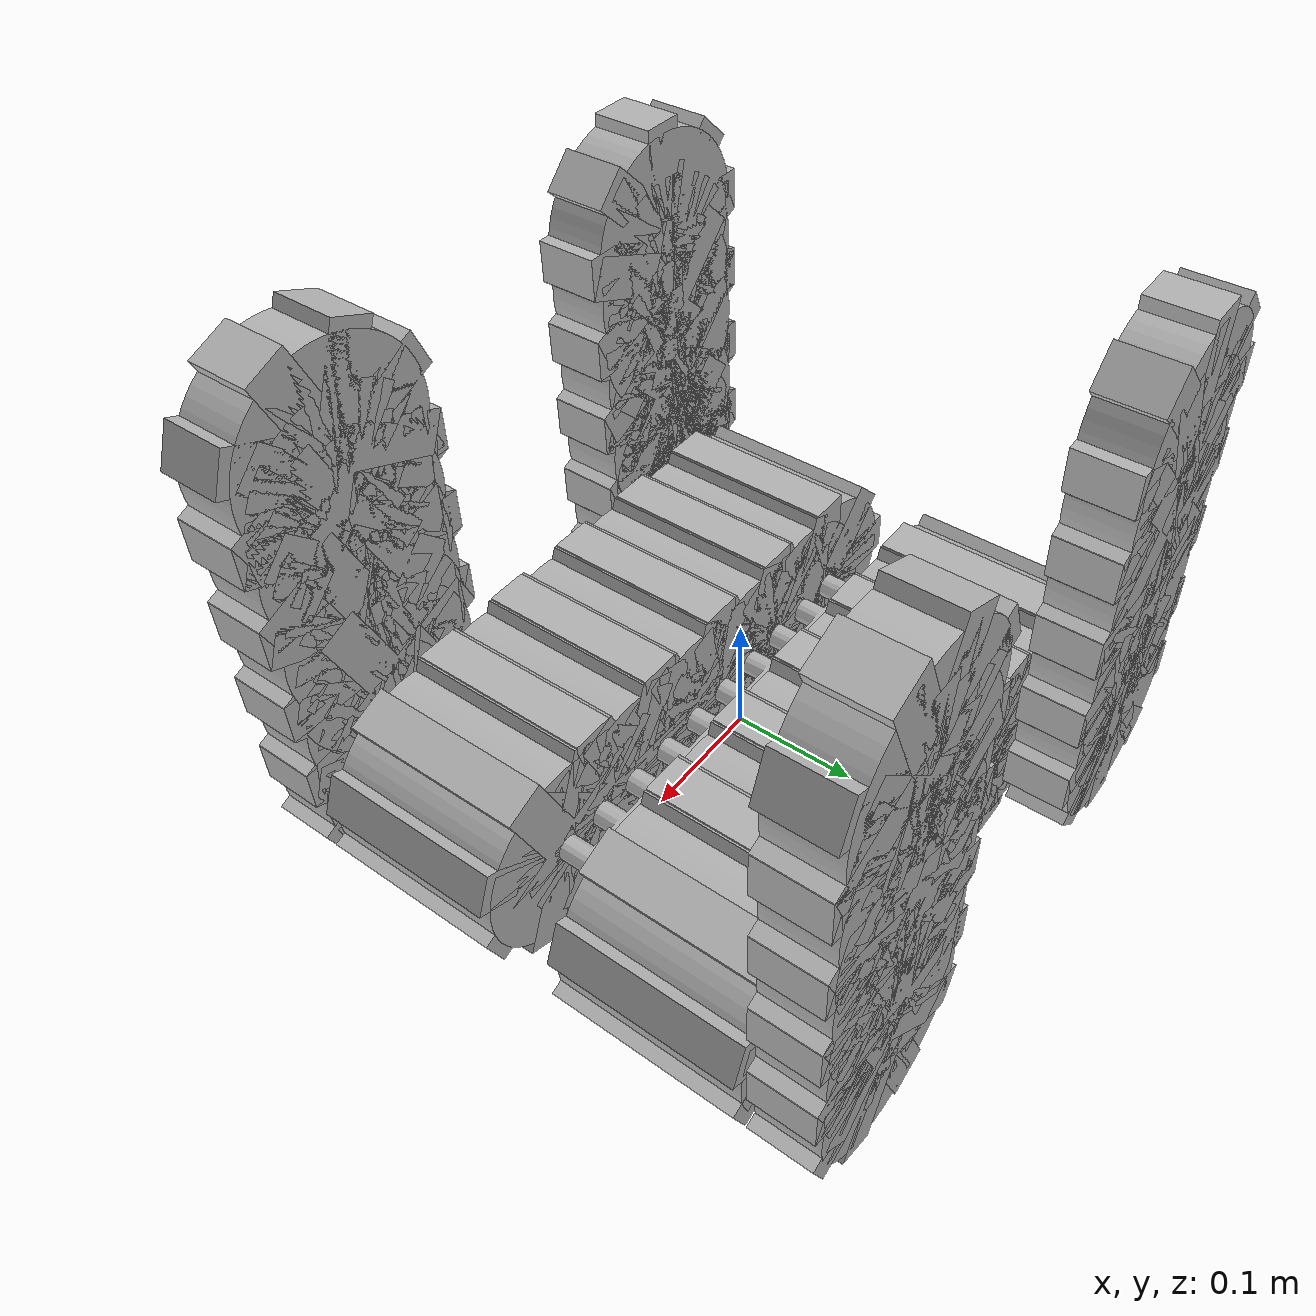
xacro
<?xml version="1.0" ?>
<robot name="easy_imax11" xmlns:xacro="http://www.ros.org/wiki/xacro">

<xacro:include filename="$(find easy_imax11_description)/urdf/materials.xacro" />
<xacro:include filename="$(find easy_imax11_description)/urdf/easy_imax11.trans" />
<xacro:include filename="$(find easy_imax11_description)/urdf/easy_imax11.gazebo" />
<link name="base_link">
  <inertial>
    <origin xyz="0.0009143543006268772 -0.00032949692907712587 -0.000898247401832566" rpy="0 0 0"/>
    <mass value="1.2099574875277084"/>
    <inertia ixx="0.012249" iyy="0.014034" izz="0.02622" ixy="0.0" iyz="0.0" ixz="0.0"/>
  </inertial>
  <visual>
    <origin xyz="0 0 0" rpy="0 0 0"/>
    <geometry>
      <mesh filename="package://easy_imax11_description/meshes/base_link.stl" scale="0.001 0.001 0.001"/>
    </geometry>
    <material name="silver"/>
  </visual>
  <collision>
    <origin xyz="0 0 0" rpy="0 0 0"/>
    <geometry>
      <mesh filename="package://easy_imax11_description/meshes/base_link.stl" scale="0.001 0.001 0.001"/>
    </geometry>
  </collision>
</link>

<link name="fr_1">
  <inertial>
    <origin xyz="3.543007099093831e-07 0.03909435267954545 0.13820028823912464" rpy="0 0 0"/>
    <mass value="0.052061944901923785"/>
    <inertia ixx="0.000425" iyy="0.00042" izz="6e-06" ixy="-0.0" iyz="-7e-06" ixz="-0.0"/>
  </inertial>
  <visual>
    <origin xyz="0.168502 -0.179671 0.000898" rpy="0 0 0"/>
    <geometry>
      <mesh filename="package://easy_imax11_description/meshes/fr_1.stl" scale="0.001 0.001 0.001"/>
    </geometry>
    <material name="silver"/>
  </visual>
  <collision>
    <origin xyz="0.168502 -0.179671 0.000898" rpy="0 0 0"/>
    <geometry>
      <mesh filename="package://easy_imax11_description/meshes/fr_1.stl" scale="0.001 0.001 0.001"/>
    </geometry>
  </collision>
</link>

<link name="rr_1">
  <inertial>
    <origin xyz="3.5430070963182736e-07 0.039094352679545336 0.13820028823912467" rpy="0 0 0"/>
    <mass value="0.052061944901923785"/>
    <inertia ixx="0.000425" iyy="0.00042" izz="6e-06" ixy="-0.0" iyz="-7e-06" ixz="-0.0"/>
  </inertial>
  <visual>
    <origin xyz="-0.17033 -0.179671 0.000898" rpy="0 0 0"/>
    <geometry>
      <mesh filename="package://easy_imax11_description/meshes/rr_1.stl" scale="0.001 0.001 0.001"/>
    </geometry>
    <material name="silver"/>
  </visual>
  <collision>
    <origin xyz="-0.17033 -0.179671 0.000898" rpy="0 0 0"/>
    <geometry>
      <mesh filename="package://easy_imax11_description/meshes/rr_1.stl" scale="0.001 0.001 0.001"/>
    </geometry>
  </collision>
</link>

<link name="rl_1">
  <inertial>
    <origin xyz="3.543005438477742e-07 -0.03909534653769953 0.13820028823912459" rpy="0 0 0"/>
    <mass value="0.052061944901923785"/>
    <inertia ixx="0.000425" iyy="0.00042" izz="6e-06" ixy="-0.0" iyz="7e-06" ixz="0.0"/>
  </inertial>
  <visual>
    <origin xyz="-0.17033 0.180329 0.000898" rpy="0 0 0"/>
    <geometry>
      <mesh filename="package://easy_imax11_description/meshes/rl_1.stl" scale="0.001 0.001 0.001"/>
    </geometry>
    <material name="silver"/>
  </visual>
  <collision>
    <origin xyz="-0.17033 0.180329 0.000898" rpy="0 0 0"/>
    <geometry>
      <mesh filename="package://easy_imax11_description/meshes/rl_1.stl" scale="0.001 0.001 0.001"/>
    </geometry>
  </collision>
</link>

<link name="fl_1">
  <inertial>
    <origin xyz="3.5430054415308554e-07 -0.03909534653769953 0.13820028823912467" rpy="0 0 0"/>
    <mass value="0.052061944901923785"/>
    <inertia ixx="0.000425" iyy="0.00042" izz="6e-06" ixy="-0.0" iyz="7e-06" ixz="0.0"/>
  </inertial>
  <visual>
    <origin xyz="0.168502 0.180329 0.000898" rpy="0 0 0"/>
    <geometry>
      <mesh filename="package://easy_imax11_description/meshes/fl_1.stl" scale="0.001 0.001 0.001"/>
    </geometry>
    <material name="silver"/>
  </visual>
  <collision>
    <origin xyz="0.168502 0.180329 0.000898" rpy="0 0 0"/>
    <geometry>
      <mesh filename="package://easy_imax11_description/meshes/fl_1.stl" scale="0.001 0.001 0.001"/>
    </geometry>
  </collision>
</link>

<link name="gt_1">
  <inertial>
    <origin xyz="3.5430068837105644e-07 0.0749995030709231 -2.474018325239469e-07" rpy="0 0 0"/>
    <mass value="1.604639516242575"/>
    <inertia ixx="0.005485" iyy="0.004952" izz="0.005485" ixy="0.0" iyz="-0.0" ixz="0.0"/>
  </inertial>
  <visual>
    <origin xyz="0.168502 0.180329 0.000898" rpy="0 0 0"/>
    <geometry>
      <mesh filename="package://easy_imax11_description/meshes/gt_1.stl" scale="0.001 0.001 0.001"/>
    </geometry>
    <material name="silver"/>
  </visual>
  <collision>
    <origin xyz="0.168502 0.180329 0.000898" rpy="0 0 0"/>
    <geometry>
      <mesh filename="package://easy_imax11_description/meshes/gt_1.stl" scale="0.001 0.001 0.001"/>
    </geometry>
  </collision>
</link>

<link name="gx_1">
  <inertial>
    <origin xyz="3.54300626920212e-07 0.0749995030709231 -2.4740183250128705e-07" rpy="0 0 0"/>
    <mass value="1.6046395162425733"/>
    <inertia ixx="0.005485" iyy="0.004952" izz="0.005485" ixy="0.0" iyz="-0.0" ixz="0.0"/>
  </inertial>
  <visual>
    <origin xyz="0.168502 0.180329 0.000898" rpy="0 0 0"/>
    <geometry>
      <mesh filename="package://easy_imax11_description/meshes/gx_1.stl" scale="0.001 0.001 0.001"/>
    </geometry>
    <material name="silver"/>
  </visual>
  <collision>
    <origin xyz="0.168502 0.180329 0.000898" rpy="0 0 0"/>
    <geometry>
      <mesh filename="package://easy_imax11_description/meshes/gx_1.stl" scale="0.001 0.001 0.001"/>
    </geometry>
  </collision>
</link>

<link name="gt_2">
  <inertial>
    <origin xyz="3.5430068823227856e-07 0.0749995030709231 -2.474018325239469e-07" rpy="0 0 0"/>
    <mass value="1.604639516242575"/>
    <inertia ixx="0.005485" iyy="0.004952" izz="0.005485" ixy="0.0" iyz="-0.0" ixz="0.0"/>
  </inertial>
  <visual>
    <origin xyz="0.093206 0.180329 0.000898" rpy="0 0 0"/>
    <geometry>
      <mesh filename="package://easy_imax11_description/meshes/gt_2.stl" scale="0.001 0.001 0.001"/>
    </geometry>
    <material name="silver"/>
  </visual>
  <collision>
    <origin xyz="0.093206 0.180329 0.000898" rpy="0 0 0"/>
    <geometry>
      <mesh filename="package://easy_imax11_description/meshes/gt_2.stl" scale="0.001 0.001 0.001"/>
    </geometry>
  </collision>
</link>

<link name="gx_2">
  <inertial>
    <origin xyz="3.5430062678143415e-07 0.0749995030709231 -2.4740183250128705e-07" rpy="0 0 0"/>
    <mass value="1.6046395162425733"/>
    <inertia ixx="0.005485" iyy="0.004952" izz="0.005485" ixy="-0.0" iyz="-0.0" ixz="0.0"/>
  </inertial>
  <visual>
    <origin xyz="0.093206 0.180329 0.000898" rpy="0 0 0"/>
    <geometry>
      <mesh filename="package://easy_imax11_description/meshes/gx_2.stl" scale="0.001 0.001 0.001"/>
    </geometry>
    <material name="silver"/>
  </visual>
  <collision>
    <origin xyz="0.093206 0.180329 0.000898" rpy="0 0 0"/>
    <geometry>
      <mesh filename="package://easy_imax11_description/meshes/gx_2.stl" scale="0.001 0.001 0.001"/>
    </geometry>
  </collision>
</link>

<link name="gt_3">
  <inertial>
    <origin xyz="3.543006882565647e-07 0.0749995030709231 -2.474018325239469e-07" rpy="0 0 0"/>
    <mass value="1.604639516242575"/>
    <inertia ixx="0.005485" iyy="0.004952" izz="0.005485" ixy="-0.0" iyz="-0.0" ixz="0.0"/>
  </inertial>
  <visual>
    <origin xyz="0.01791 0.180329 0.000898" rpy="0 0 0"/>
    <geometry>
      <mesh filename="package://easy_imax11_description/meshes/gt_3.stl" scale="0.001 0.001 0.001"/>
    </geometry>
    <material name="silver"/>
  </visual>
  <collision>
    <origin xyz="0.01791 0.180329 0.000898" rpy="0 0 0"/>
    <geometry>
      <mesh filename="package://easy_imax11_description/meshes/gt_3.stl" scale="0.001 0.001 0.001"/>
    </geometry>
  </collision>
</link>

<link name="gx_3">
  <inertial>
    <origin xyz="3.543006268091897e-07 0.0749995030709231 -2.4740183250128705e-07" rpy="0 0 0"/>
    <mass value="1.6046395162425733"/>
    <inertia ixx="0.005485" iyy="0.004952" izz="0.005485" ixy="-0.0" iyz="-0.0" ixz="0.0"/>
  </inertial>
  <visual>
    <origin xyz="0.01791 0.180329 0.000898" rpy="0 0 0"/>
    <geometry>
      <mesh filename="package://easy_imax11_description/meshes/gx_3.stl" scale="0.001 0.001 0.001"/>
    </geometry>
    <material name="silver"/>
  </visual>
  <collision>
    <origin xyz="0.01791 0.180329 0.000898" rpy="0 0 0"/>
    <geometry>
      <mesh filename="package://easy_imax11_description/meshes/gx_3.stl" scale="0.001 0.001 0.001"/>
    </geometry>
  </collision>
</link>

<link name="gt_4">
  <inertial>
    <origin xyz="3.543006882877897e-07 0.0749995030709231 -2.474018325239469e-07" rpy="0 0 0"/>
    <mass value="1.604639516242575"/>
    <inertia ixx="0.005485" iyy="0.004952" izz="0.005485" ixy="-0.0" iyz="-0.0" ixz="0.0"/>
  </inertial>
  <visual>
    <origin xyz="-0.057386 0.180329 0.000898" rpy="0 0 0"/>
    <geometry>
      <mesh filename="package://easy_imax11_description/meshes/gt_4.stl" scale="0.001 0.001 0.001"/>
    </geometry>
    <material name="silver"/>
  </visual>
  <collision>
    <origin xyz="-0.057386 0.180329 0.000898" rpy="0 0 0"/>
    <geometry>
      <mesh filename="package://easy_imax11_description/meshes/gt_4.stl" scale="0.001 0.001 0.001"/>
    </geometry>
  </collision>
</link>

<link name="gx_4">
  <inertial>
    <origin xyz="3.543006268369453e-07 0.0749995030709231 -2.4740183250128705e-07" rpy="0 0 0"/>
    <mass value="1.6046395162425733"/>
    <inertia ixx="0.005485" iyy="0.004952" izz="0.005485" ixy="-0.0" iyz="-0.0" ixz="0.0"/>
  </inertial>
  <visual>
    <origin xyz="-0.057386 0.180329 0.000898" rpy="0 0 0"/>
    <geometry>
      <mesh filename="package://easy_imax11_description/meshes/gx_4.stl" scale="0.001 0.001 0.001"/>
    </geometry>
    <material name="silver"/>
  </visual>
  <collision>
    <origin xyz="-0.057386 0.180329 0.000898" rpy="0 0 0"/>
    <geometry>
      <mesh filename="package://easy_imax11_description/meshes/gx_4.stl" scale="0.001 0.001 0.001"/>
    </geometry>
  </collision>
</link>

<link name="gt_5">
  <inertial>
    <origin xyz="3.5430068814901183e-07 0.07499950307092303 -2.474018325239469e-07" rpy="0 0 0"/>
    <mass value="1.604639516242575"/>
    <inertia ixx="0.005485" iyy="0.004952" izz="0.005485" ixy="-0.0" iyz="-0.0" ixz="0.0"/>
  </inertial>
  <visual>
    <origin xyz="-0.132682 0.180329 0.000898" rpy="0 0 0"/>
    <geometry>
      <mesh filename="package://easy_imax11_description/meshes/gt_5.stl" scale="0.001 0.001 0.001"/>
    </geometry>
    <material name="silver"/>
  </visual>
  <collision>
    <origin xyz="-0.132682 0.180329 0.000898" rpy="0 0 0"/>
    <geometry>
      <mesh filename="package://easy_imax11_description/meshes/gt_5.stl" scale="0.001 0.001 0.001"/>
    </geometry>
  </collision>
</link>

<link name="gx_5">
  <inertial>
    <origin xyz="3.543006266981674e-07 0.07499950307092303 -2.4740183250128705e-07" rpy="0 0 0"/>
    <mass value="1.6046395162425733"/>
    <inertia ixx="0.005485" iyy="0.004952" izz="0.005485" ixy="0.0" iyz="-0.0" ixz="0.0"/>
  </inertial>
  <visual>
    <origin xyz="-0.132682 0.180329 0.000898" rpy="0 0 0"/>
    <geometry>
      <mesh filename="package://easy_imax11_description/meshes/gx_5.stl" scale="0.001 0.001 0.001"/>
    </geometry>
    <material name="silver"/>
  </visual>
  <collision>
    <origin xyz="-0.132682 0.180329 0.000898" rpy="0 0 0"/>
    <geometry>
      <mesh filename="package://easy_imax11_description/meshes/gx_5.stl" scale="0.001 0.001 0.001"/>
    </geometry>
  </collision>
</link>

<link name="gc_1">
  <inertial>
    <origin xyz="3.5430065978281355e-07 0.07499950307092312 -2.4740183252329635e-07" rpy="0 0 0"/>
    <mass value="3.004953079112718"/>
    <inertia ixx="0.010575" iyy="0.009881" izz="0.010575" ixy="0.0" iyz="0.0" ixz="0.0"/>
  </inertial>
  <visual>
    <origin xyz="0.168502 0.180329 0.000898" rpy="0 0 0"/>
    <geometry>
      <mesh filename="package://easy_imax11_description/meshes/gc_1.stl" scale="0.001 0.001 0.001"/>
    </geometry>
    <material name="silver"/>
  </visual>
  <collision>
    <origin xyz="0.168502 0.180329 0.000898" rpy="0 0 0"/>
    <geometry>
      <mesh filename="package://easy_imax11_description/meshes/gc_1.stl" scale="0.001 0.001 0.001"/>
    </geometry>
  </collision>
</link>

<link name="gc_2">
  <inertial>
    <origin xyz="3.543006596301579e-07 0.07499950307092312 -2.4740183252329635e-07" rpy="0 0 0"/>
    <mass value="3.004953079112718"/>
    <inertia ixx="0.010575" iyy="0.009881" izz="0.010575" ixy="0.0" iyz="0.0" ixz="0.0"/>
  </inertial>
  <visual>
    <origin xyz="0.093206 0.180329 0.000898" rpy="0 0 0"/>
    <geometry>
      <mesh filename="package://easy_imax11_description/meshes/gc_2.stl" scale="0.001 0.001 0.001"/>
    </geometry>
    <material name="silver"/>
  </visual>
  <collision>
    <origin xyz="0.093206 0.180329 0.000898" rpy="0 0 0"/>
    <geometry>
      <mesh filename="package://easy_imax11_description/meshes/gc_2.stl" scale="0.001 0.001 0.001"/>
    </geometry>
  </collision>
</link>

<link name="gc_3">
  <inertial>
    <origin xyz="3.54300659654444e-07 0.07499950307092312 -2.4740183252329635e-07" rpy="0 0 0"/>
    <mass value="3.004953079112718"/>
    <inertia ixx="0.010575" iyy="0.009881" izz="0.010575" ixy="0.0" iyz="0.0" ixz="0.0"/>
  </inertial>
  <visual>
    <origin xyz="0.01791 0.180329 0.000898" rpy="0 0 0"/>
    <geometry>
      <mesh filename="package://easy_imax11_description/meshes/gc_3.stl" scale="0.001 0.001 0.001"/>
    </geometry>
    <material name="silver"/>
  </visual>
  <collision>
    <origin xyz="0.01791 0.180329 0.000898" rpy="0 0 0"/>
    <geometry>
      <mesh filename="package://easy_imax11_description/meshes/gc_3.stl" scale="0.001 0.001 0.001"/>
    </geometry>
  </collision>
</link>

<link name="gc_4">
  <inertial>
    <origin xyz="3.5430065967179125e-07 0.07499950307092312 -2.4740183252329635e-07" rpy="0 0 0"/>
    <mass value="3.004953079112718"/>
    <inertia ixx="0.010575" iyy="0.009881" izz="0.010575" ixy="0.0" iyz="0.0" ixz="0.0"/>
  </inertial>
  <visual>
    <origin xyz="-0.057386 0.180329 0.000898" rpy="0 0 0"/>
    <geometry>
      <mesh filename="package://easy_imax11_description/meshes/gc_4.stl" scale="0.001 0.001 0.001"/>
    </geometry>
    <material name="silver"/>
  </visual>
  <collision>
    <origin xyz="-0.057386 0.180329 0.000898" rpy="0 0 0"/>
    <geometry>
      <mesh filename="package://easy_imax11_description/meshes/gc_4.stl" scale="0.001 0.001 0.001"/>
    </geometry>
  </collision>
</link>

<link name="gc_5">
  <inertial>
    <origin xyz="3.5430065956076895e-07 0.07499950307092304 -2.4740183252329635e-07" rpy="0 0 0"/>
    <mass value="3.004953079112718"/>
    <inertia ixx="0.010575" iyy="0.009881" izz="0.010575" ixy="0.0" iyz="0.0" ixz="0.0"/>
  </inertial>
  <visual>
    <origin xyz="-0.132682 0.180329 0.000898" rpy="0 0 0"/>
    <geometry>
      <mesh filename="package://easy_imax11_description/meshes/gc_5.stl" scale="0.001 0.001 0.001"/>
    </geometry>
    <material name="silver"/>
  </visual>
  <collision>
    <origin xyz="-0.132682 0.180329 0.000898" rpy="0 0 0"/>
    <geometry>
      <mesh filename="package://easy_imax11_description/meshes/gc_5.stl" scale="0.001 0.001 0.001"/>
    </geometry>
  </collision>
</link>

<link name="mgt_5">
  <inertial>
    <origin xyz="3.543006880518673e-07 0.07499950307092308 -2.4740183251267117e-07" rpy="0 0 0"/>
    <mass value="1.6046395162425742"/>
    <inertia ixx="0.005485" iyy="0.004952" izz="0.005485" ixy="0.0" iyz="0.0" ixz="0.0"/>
  </inertial>
  <visual>
    <origin xyz="-0.095034 0.180329 0.000898" rpy="0 0 0"/>
    <geometry>
      <mesh filename="package://easy_imax11_description/meshes/mgt_5.stl" scale="0.001 0.001 0.001"/>
    </geometry>
    <material name="silver"/>
  </visual>
  <collision>
    <origin xyz="-0.095034 0.180329 0.000898" rpy="0 0 0"/>
    <geometry>
      <mesh filename="package://easy_imax11_description/meshes/mgt_5.stl" scale="0.001 0.001 0.001"/>
    </geometry>
  </collision>
</link>

<link name="mgx_5">
  <inertial>
    <origin xyz="3.543006880935007e-07 0.07499950307092307 -2.47401832535331e-07" rpy="0 0 0"/>
    <mass value="1.6046395162425737"/>
    <inertia ixx="0.005485" iyy="0.004952" izz="0.005485" ixy="0.0" iyz="0.0" ixz="0.0"/>
  </inertial>
  <visual>
    <origin xyz="-0.095034 0.180329 0.000898" rpy="0 0 0"/>
    <geometry>
      <mesh filename="package://easy_imax11_description/meshes/mgx_5.stl" scale="0.001 0.001 0.001"/>
    </geometry>
    <material name="silver"/>
  </visual>
  <collision>
    <origin xyz="-0.095034 0.180329 0.000898" rpy="0 0 0"/>
    <geometry>
      <mesh filename="package://easy_imax11_description/meshes/mgx_5.stl" scale="0.001 0.001 0.001"/>
    </geometry>
  </collision>
</link>

<link name="mgt_1">
  <inertial>
    <origin xyz="3.543006881698285e-07 0.07499950307092308 -2.4740183251267117e-07" rpy="0 0 0"/>
    <mass value="1.6046395162425742"/>
    <inertia ixx="0.005485" iyy="0.004952" izz="0.005485" ixy="0.0" iyz="0.0" ixz="0.0"/>
  </inertial>
  <visual>
    <origin xyz="-0.019738 0.180329 0.000898" rpy="0 0 0"/>
    <geometry>
      <mesh filename="package://easy_imax11_description/meshes/mgt_1.stl" scale="0.001 0.001 0.001"/>
    </geometry>
    <material name="silver"/>
  </visual>
  <collision>
    <origin xyz="-0.019738 0.180329 0.000898" rpy="0 0 0"/>
    <geometry>
      <mesh filename="package://easy_imax11_description/meshes/mgt_1.stl" scale="0.001 0.001 0.001"/>
    </geometry>
  </collision>
</link>

<link name="mgx_1">
  <inertial>
    <origin xyz="3.543006882149313e-07 0.07499950307092307 -2.47401832535331e-07" rpy="0 0 0"/>
    <mass value="1.6046395162425737"/>
    <inertia ixx="0.005485" iyy="0.004952" izz="0.005485" ixy="0.0" iyz="0.0" ixz="0.0"/>
  </inertial>
  <visual>
    <origin xyz="-0.019738 0.180329 0.000898" rpy="0 0 0"/>
    <geometry>
      <mesh filename="package://easy_imax11_description/meshes/mgx_1.stl" scale="0.001 0.001 0.001"/>
    </geometry>
    <material name="silver"/>
  </visual>
  <collision>
    <origin xyz="-0.019738 0.180329 0.000898" rpy="0 0 0"/>
    <geometry>
      <mesh filename="package://easy_imax11_description/meshes/mgx_1.stl" scale="0.001 0.001 0.001"/>
    </geometry>
  </collision>
</link>

<link name="mgt_2">
  <inertial>
    <origin xyz="3.5430068812125626e-07 0.07499950307092315 -2.4740183251267117e-07" rpy="0 0 0"/>
    <mass value="1.6046395162425742"/>
    <inertia ixx="0.005485" iyy="0.004952" izz="0.005485" ixy="0.0" iyz="0.0" ixz="0.0"/>
  </inertial>
  <visual>
    <origin xyz="0.130854 0.180329 0.000898" rpy="0 0 0"/>
    <geometry>
      <mesh filename="package://easy_imax11_description/meshes/mgt_2.stl" scale="0.001 0.001 0.001"/>
    </geometry>
    <material name="silver"/>
  </visual>
  <collision>
    <origin xyz="0.130854 0.180329 0.000898" rpy="0 0 0"/>
    <geometry>
      <mesh filename="package://easy_imax11_description/meshes/mgt_2.stl" scale="0.001 0.001 0.001"/>
    </geometry>
  </collision>
</link>

<link name="mgx_2">
  <inertial>
    <origin xyz="3.543006883155453e-07 0.07499950307092312 -2.47401832535331e-07" rpy="0 0 0"/>
    <mass value="1.6046395162425737"/>
    <inertia ixx="0.005485" iyy="0.004952" izz="0.005485" ixy="0.0" iyz="0.0" ixz="0.0"/>
  </inertial>
  <visual>
    <origin xyz="0.130854 0.180329 0.000898" rpy="0 0 0"/>
    <geometry>
      <mesh filename="package://easy_imax11_description/meshes/mgx_2.stl" scale="0.001 0.001 0.001"/>
    </geometry>
    <material name="silver"/>
  </visual>
  <collision>
    <origin xyz="0.130854 0.180329 0.000898" rpy="0 0 0"/>
    <geometry>
      <mesh filename="package://easy_imax11_description/meshes/mgx_2.stl" scale="0.001 0.001 0.001"/>
    </geometry>
  </collision>
</link>

<link name="mgt_3">
  <inertial>
    <origin xyz="3.543006882947286e-07 0.07499950307092308 -2.4740183251267117e-07" rpy="0 0 0"/>
    <mass value="1.6046395162425742"/>
    <inertia ixx="0.005485" iyy="0.004952" izz="0.005485" ixy="0.0" iyz="0.0" ixz="0.0"/>
  </inertial>
  <visual>
    <origin xyz="0.055558 0.180329 0.000898" rpy="0 0 0"/>
    <geometry>
      <mesh filename="package://easy_imax11_description/meshes/mgt_3.stl" scale="0.001 0.001 0.001"/>
    </geometry>
    <material name="silver"/>
  </visual>
  <collision>
    <origin xyz="0.055558 0.180329 0.000898" rpy="0 0 0"/>
    <geometry>
      <mesh filename="package://easy_imax11_description/meshes/mgt_3.stl" scale="0.001 0.001 0.001"/>
    </geometry>
  </collision>
</link>

<link name="mgx_3">
  <inertial>
    <origin xyz="3.5430068834330086e-07 0.07499950307092307 -2.47401832535331e-07" rpy="0 0 0"/>
    <mass value="1.6046395162425737"/>
    <inertia ixx="0.005485" iyy="0.004952" izz="0.005485" ixy="0.0" iyz="0.0" ixz="0.0"/>
  </inertial>
  <visual>
    <origin xyz="0.055558 0.180329 0.000898" rpy="0 0 0"/>
    <geometry>
      <mesh filename="package://easy_imax11_description/meshes/mgx_3.stl" scale="0.001 0.001 0.001"/>
    </geometry>
    <material name="silver"/>
  </visual>
  <collision>
    <origin xyz="0.055558 0.180329 0.000898" rpy="0 0 0"/>
    <geometry>
      <mesh filename="package://easy_imax11_description/meshes/mgx_3.stl" scale="0.001 0.001 0.001"/>
    </geometry>
  </collision>
</link>

<link name="mgt_4">
  <inertial>
    <origin xyz="3.543006880657451e-07 0.07499950307092308 -2.4740183251267117e-07" rpy="0 0 0"/>
    <mass value="1.6046395162425742"/>
    <inertia ixx="0.005485" iyy="0.004952" izz="0.005485" ixy="0.0" iyz="0.0" ixz="0.0"/>
  </inertial>
  <visual>
    <origin xyz="-0.17033 0.180329 0.000898" rpy="0 0 0"/>
    <geometry>
      <mesh filename="package://easy_imax11_description/meshes/mgt_4.stl" scale="0.001 0.001 0.001"/>
    </geometry>
    <material name="silver"/>
  </visual>
  <collision>
    <origin xyz="-0.17033 0.180329 0.000898" rpy="0 0 0"/>
    <geometry>
      <mesh filename="package://easy_imax11_description/meshes/mgt_4.stl" scale="0.001 0.001 0.001"/>
    </geometry>
  </collision>
</link>

<link name="mgx_4">
  <inertial>
    <origin xyz="3.543006880935007e-07 0.07499950307092307 -2.47401832535331e-07" rpy="0 0 0"/>
    <mass value="1.6046395162425737"/>
    <inertia ixx="0.005485" iyy="0.004952" izz="0.005485" ixy="0.0" iyz="0.0" ixz="0.0"/>
  </inertial>
  <visual>
    <origin xyz="-0.17033 0.180329 0.000898" rpy="0 0 0"/>
    <geometry>
      <mesh filename="package://easy_imax11_description/meshes/mgx_4.stl" scale="0.001 0.001 0.001"/>
    </geometry>
    <material name="silver"/>
  </visual>
  <collision>
    <origin xyz="-0.17033 0.180329 0.000898" rpy="0 0 0"/>
    <geometry>
      <mesh filename="package://easy_imax11_description/meshes/mgx_4.stl" scale="0.001 0.001 0.001"/>
    </geometry>
  </collision>
</link>

<link name="mgc_5">
  <inertial>
    <origin xyz="3.543006596162801e-07 0.07499950307092307 -2.4740183252329635e-07" rpy="0 0 0"/>
    <mass value="3.004953079112718"/>
    <inertia ixx="0.010575" iyy="0.009881" izz="0.010575" ixy="0.0" iyz="0.0" ixz="0.0"/>
  </inertial>
  <visual>
    <origin xyz="-0.095034 0.180329 0.000898" rpy="0 0 0"/>
    <geometry>
      <mesh filename="package://easy_imax11_description/meshes/mgc_5.stl" scale="0.001 0.001 0.001"/>
    </geometry>
    <material name="silver"/>
  </visual>
  <collision>
    <origin xyz="-0.095034 0.180329 0.000898" rpy="0 0 0"/>
    <geometry>
      <mesh filename="package://easy_imax11_description/meshes/mgc_5.stl" scale="0.001 0.001 0.001"/>
    </geometry>
  </collision>
</link>

<link name="mgc_1">
  <inertial>
    <origin xyz="3.5430065959199397e-07 0.07499950307092307 -2.4740183252329635e-07" rpy="0 0 0"/>
    <mass value="3.004953079112718"/>
    <inertia ixx="0.010575" iyy="0.009881" izz="0.010575" ixy="0.0" iyz="0.0" ixz="0.0"/>
  </inertial>
  <visual>
    <origin xyz="-0.019738 0.180329 0.000898" rpy="0 0 0"/>
    <geometry>
      <mesh filename="package://easy_imax11_description/meshes/mgc_1.stl" scale="0.001 0.001 0.001"/>
    </geometry>
    <material name="silver"/>
  </visual>
  <collision>
    <origin xyz="-0.019738 0.180329 0.000898" rpy="0 0 0"/>
    <geometry>
      <mesh filename="package://easy_imax11_description/meshes/mgc_1.stl" scale="0.001 0.001 0.001"/>
    </geometry>
  </collision>
</link>

<link name="mgc_2">
  <inertial>
    <origin xyz="3.5430065969954683e-07 0.07499950307092314 -2.4740183252329635e-07" rpy="0 0 0"/>
    <mass value="3.004953079112718"/>
    <inertia ixx="0.010575" iyy="0.009881" izz="0.010575" ixy="0.0" iyz="0.0" ixz="0.0"/>
  </inertial>
  <visual>
    <origin xyz="0.130854 0.180329 0.000898" rpy="0 0 0"/>
    <geometry>
      <mesh filename="package://easy_imax11_description/meshes/mgc_2.stl" scale="0.001 0.001 0.001"/>
    </geometry>
    <material name="silver"/>
  </visual>
  <collision>
    <origin xyz="0.130854 0.180329 0.000898" rpy="0 0 0"/>
    <geometry>
      <mesh filename="package://easy_imax11_description/meshes/mgc_2.stl" scale="0.001 0.001 0.001"/>
    </geometry>
  </collision>
</link>

<link name="mgc_3">
  <inertial>
    <origin xyz="3.5430065957464674e-07 0.07499950307092307 -2.4740183252329635e-07" rpy="0 0 0"/>
    <mass value="3.004953079112718"/>
    <inertia ixx="0.010575" iyy="0.009881" izz="0.010575" ixy="0.0" iyz="0.0" ixz="0.0"/>
  </inertial>
  <visual>
    <origin xyz="0.055558 0.180329 0.000898" rpy="0 0 0"/>
    <geometry>
      <mesh filename="package://easy_imax11_description/meshes/mgc_3.stl" scale="0.001 0.001 0.001"/>
    </geometry>
    <material name="silver"/>
  </visual>
  <collision>
    <origin xyz="0.055558 0.180329 0.000898" rpy="0 0 0"/>
    <geometry>
      <mesh filename="package://easy_imax11_description/meshes/mgc_3.stl" scale="0.001 0.001 0.001"/>
    </geometry>
  </collision>
</link>

<link name="mgc_4">
  <inertial>
    <origin xyz="3.5430065944974665e-07 0.07499950307092307 -2.4740183252329635e-07" rpy="0 0 0"/>
    <mass value="3.004953079112718"/>
    <inertia ixx="0.010575" iyy="0.009881" izz="0.010575" ixy="0.0" iyz="0.0" ixz="0.0"/>
  </inertial>
  <visual>
    <origin xyz="-0.17033 0.180329 0.000898" rpy="0 0 0"/>
    <geometry>
      <mesh filename="package://easy_imax11_description/meshes/mgc_4.stl" scale="0.001 0.001 0.001"/>
    </geometry>
    <material name="silver"/>
  </visual>
  <collision>
    <origin xyz="-0.17033 0.180329 0.000898" rpy="0 0 0"/>
    <geometry>
      <mesh filename="package://easy_imax11_description/meshes/mgc_4.stl" scale="0.001 0.001 0.001"/>
    </geometry>
  </collision>
</link>

<link name="cgt_1">
  <inertial>
    <origin xyz="3.543006885375899e-07 -0.07500049692907726 -2.474018325585329e-07" rpy="0 0 0"/>
    <mass value="1.604639516242575"/>
    <inertia ixx="0.005485" iyy="0.004952" izz="0.005485" ixy="0.0" iyz="0.0" ixz="0.0"/>
  </inertial>
  <visual>
    <origin xyz="0.168502 -0.179671 0.000898" rpy="0 0 0"/>
    <geometry>
      <mesh filename="package://easy_imax11_description/meshes/cgt_1.stl" scale="0.001 0.001 0.001"/>
    </geometry>
    <material name="silver"/>
  </visual>
  <collision>
    <origin xyz="0.168502 -0.179671 0.000898" rpy="0 0 0"/>
    <geometry>
      <mesh filename="package://easy_imax11_description/meshes/cgt_1.stl" scale="0.001 0.001 0.001"/>
    </geometry>
  </collision>
</link>

<link name="cgx_1">
  <inertial>
    <origin xyz="3.543006270589899e-07 -0.07500049692907725 -2.474018325585329e-07" rpy="0 0 0"/>
    <mass value="1.6046395162425733"/>
    <inertia ixx="0.005485" iyy="0.004952" izz="0.005485" ixy="-0.0" iyz="-0.0" ixz="-0.0"/>
  </inertial>
  <visual>
    <origin xyz="0.168502 -0.179671 0.000898" rpy="0 0 0"/>
    <geometry>
      <mesh filename="package://easy_imax11_description/meshes/cgx_1.stl" scale="0.001 0.001 0.001"/>
    </geometry>
    <material name="silver"/>
  </visual>
  <collision>
    <origin xyz="0.168502 -0.179671 0.000898" rpy="0 0 0"/>
    <geometry>
      <mesh filename="package://easy_imax11_description/meshes/cgx_1.stl" scale="0.001 0.001 0.001"/>
    </geometry>
  </collision>
</link>

<link name="cgt_2">
  <inertial>
    <origin xyz="3.5430068837105644e-07 -0.0750004969290772 -2.474018325230795e-07" rpy="0 0 0"/>
    <mass value="1.604639516242575"/>
    <inertia ixx="0.005485" iyy="0.004952" izz="0.005485" ixy="-0.0" iyz="0.0" ixz="0.0"/>
  </inertial>
  <visual>
    <origin xyz="0.093206 -0.179671 0.000898" rpy="0 0 0"/>
    <geometry>
      <mesh filename="package://easy_imax11_description/meshes/cgt_2.stl" scale="0.001 0.001 0.001"/>
    </geometry>
    <material name="silver"/>
  </visual>
  <collision>
    <origin xyz="0.093206 -0.179671 0.000898" rpy="0 0 0"/>
    <geometry>
      <mesh filename="package://easy_imax11_description/meshes/cgt_2.stl" scale="0.001 0.001 0.001"/>
    </geometry>
  </collision>
</link>

<link name="cgx_2">
  <inertial>
    <origin xyz="3.54300626920212e-07 -0.0750004969290772 -2.474018325229711e-07" rpy="0 0 0"/>
    <mass value="1.6046395162425733"/>
    <inertia ixx="0.005485" iyy="0.004952" izz="0.005485" ixy="0.0" iyz="-0.0" ixz="-0.0"/>
  </inertial>
  <visual>
    <origin xyz="0.093206 -0.179671 0.000898" rpy="0 0 0"/>
    <geometry>
      <mesh filename="package://easy_imax11_description/meshes/cgx_2.stl" scale="0.001 0.001 0.001"/>
    </geometry>
    <material name="silver"/>
  </visual>
  <collision>
    <origin xyz="0.093206 -0.179671 0.000898" rpy="0 0 0"/>
    <geometry>
      <mesh filename="package://easy_imax11_description/meshes/cgx_2.stl" scale="0.001 0.001 0.001"/>
    </geometry>
  </collision>
</link>

<link name="cgt_3">
  <inertial>
    <origin xyz="3.5430068839534257e-07 -0.0750004969290772 -2.474018325230795e-07" rpy="0 0 0"/>
    <mass value="1.604639516242575"/>
    <inertia ixx="0.005485" iyy="0.004952" izz="0.005485" ixy="-0.0" iyz="0.0" ixz="0.0"/>
  </inertial>
  <visual>
    <origin xyz="0.01791 -0.179671 0.000898" rpy="0 0 0"/>
    <geometry>
      <mesh filename="package://easy_imax11_description/meshes/cgt_3.stl" scale="0.001 0.001 0.001"/>
    </geometry>
    <material name="silver"/>
  </visual>
  <collision>
    <origin xyz="0.01791 -0.179671 0.000898" rpy="0 0 0"/>
    <geometry>
      <mesh filename="package://easy_imax11_description/meshes/cgt_3.stl" scale="0.001 0.001 0.001"/>
    </geometry>
  </collision>
</link>

<link name="cgx_3">
  <inertial>
    <origin xyz="3.5430062694449815e-07 -0.0750004969290772 -2.474018325229711e-07" rpy="0 0 0"/>
    <mass value="1.6046395162425733"/>
    <inertia ixx="0.005485" iyy="0.004952" izz="0.005485" ixy="-0.0" iyz="-0.0" ixz="-0.0"/>
  </inertial>
  <visual>
    <origin xyz="0.01791 -0.179671 0.000898" rpy="0 0 0"/>
    <geometry>
      <mesh filename="package://easy_imax11_description/meshes/cgx_3.stl" scale="0.001 0.001 0.001"/>
    </geometry>
    <material name="silver"/>
  </visual>
  <collision>
    <origin xyz="0.01791 -0.179671 0.000898" rpy="0 0 0"/>
    <geometry>
      <mesh filename="package://easy_imax11_description/meshes/cgx_3.stl" scale="0.001 0.001 0.001"/>
    </geometry>
  </collision>
</link>

<link name="cgt_4">
  <inertial>
    <origin xyz="3.543006882739119e-07 -0.0750004969290772 -2.474018325230795e-07" rpy="0 0 0"/>
    <mass value="1.604639516242575"/>
    <inertia ixx="0.005485" iyy="0.004952" izz="0.005485" ixy="-0.0" iyz="0.0" ixz="0.0"/>
  </inertial>
  <visual>
    <origin xyz="-0.057386 -0.179671 0.000898" rpy="0 0 0"/>
    <geometry>
      <mesh filename="package://easy_imax11_description/meshes/cgt_4.stl" scale="0.001 0.001 0.001"/>
    </geometry>
    <material name="silver"/>
  </visual>
  <collision>
    <origin xyz="-0.057386 -0.179671 0.000898" rpy="0 0 0"/>
    <geometry>
      <mesh filename="package://easy_imax11_description/meshes/cgt_4.stl" scale="0.001 0.001 0.001"/>
    </geometry>
  </collision>
</link>

<link name="cgx_4">
  <inertial>
    <origin xyz="3.543006268161286e-07 -0.0750004969290772 -2.474018325229711e-07" rpy="0 0 0"/>
    <mass value="1.6046395162425733"/>
    <inertia ixx="0.005485" iyy="0.004952" izz="0.005485" ixy="-0.0" iyz="-0.0" ixz="-0.0"/>
  </inertial>
  <visual>
    <origin xyz="-0.057386 -0.179671 0.000898" rpy="0 0 0"/>
    <geometry>
      <mesh filename="package://easy_imax11_description/meshes/cgx_4.stl" scale="0.001 0.001 0.001"/>
    </geometry>
    <material name="silver"/>
  </visual>
  <collision>
    <origin xyz="-0.057386 -0.179671 0.000898" rpy="0 0 0"/>
    <geometry>
      <mesh filename="package://easy_imax11_description/meshes/cgx_4.stl" scale="0.001 0.001 0.001"/>
    </geometry>
  </collision>
</link>

<link name="cgt_5">
  <inertial>
    <origin xyz="3.543006882877897e-07 -0.07500049692907727 -2.474018325230795e-07" rpy="0 0 0"/>
    <mass value="1.604639516242575"/>
    <inertia ixx="0.005485" iyy="0.004952" izz="0.005485" ixy="-0.0" iyz="0.0" ixz="0.0"/>
  </inertial>
  <visual>
    <origin xyz="-0.132682 -0.179671 0.000898" rpy="0 0 0"/>
    <geometry>
      <mesh filename="package://easy_imax11_description/meshes/cgt_5.stl" scale="0.001 0.001 0.001"/>
    </geometry>
    <material name="silver"/>
  </visual>
  <collision>
    <origin xyz="-0.132682 -0.179671 0.000898" rpy="0 0 0"/>
    <geometry>
      <mesh filename="package://easy_imax11_description/meshes/cgt_5.stl" scale="0.001 0.001 0.001"/>
    </geometry>
  </collision>
</link>

<link name="cgx_5">
  <inertial>
    <origin xyz="3.543006268647009e-07 -0.07500049692907727 -2.474018325229711e-07" rpy="0 0 0"/>
    <mass value="1.6046395162425733"/>
    <inertia ixx="0.005485" iyy="0.004952" izz="0.005485" ixy="-0.0" iyz="-0.0" ixz="-0.0"/>
  </inertial>
  <visual>
    <origin xyz="-0.132682 -0.179671 0.000898" rpy="0 0 0"/>
    <geometry>
      <mesh filename="package://easy_imax11_description/meshes/cgx_5.stl" scale="0.001 0.001 0.001"/>
    </geometry>
    <material name="silver"/>
  </visual>
  <collision>
    <origin xyz="-0.132682 -0.179671 0.000898" rpy="0 0 0"/>
    <geometry>
      <mesh filename="package://easy_imax11_description/meshes/cgx_5.stl" scale="0.001 0.001 0.001"/>
    </geometry>
  </collision>
</link>

<link name="cgc_1">
  <inertial>
    <origin xyz="3.5430065989383586e-07 -0.07500049692907725 -2.47401832557774e-07" rpy="0 0 0"/>
    <mass value="3.004953079112718"/>
    <inertia ixx="0.010575" iyy="0.009881" izz="0.010575" ixy="-0.0" iyz="-0.0" ixz="0.0"/>
  </inertial>
  <visual>
    <origin xyz="0.168502 -0.179671 0.000898" rpy="0 0 0"/>
    <geometry>
      <mesh filename="package://easy_imax11_description/meshes/cgc_1.stl" scale="0.001 0.001 0.001"/>
    </geometry>
    <material name="silver"/>
  </visual>
  <collision>
    <origin xyz="0.168502 -0.179671 0.000898" rpy="0 0 0"/>
    <geometry>
      <mesh filename="package://easy_imax11_description/meshes/cgc_1.stl" scale="0.001 0.001 0.001"/>
    </geometry>
  </collision>
</link>

<link name="cgc_2">
  <inertial>
    <origin xyz="3.5430065976893577e-07 -0.0750004969290772 -2.47401832557774e-07" rpy="0 0 0"/>
    <mass value="3.004953079112718"/>
    <inertia ixx="0.010575" iyy="0.009881" izz="0.010575" ixy="-0.0" iyz="-0.0" ixz="0.0"/>
  </inertial>
  <visual>
    <origin xyz="0.093206 -0.179671 0.000898" rpy="0 0 0"/>
    <geometry>
      <mesh filename="package://easy_imax11_description/meshes/cgc_2.stl" scale="0.001 0.001 0.001"/>
    </geometry>
    <material name="silver"/>
  </visual>
  <collision>
    <origin xyz="0.093206 -0.179671 0.000898" rpy="0 0 0"/>
    <geometry>
      <mesh filename="package://easy_imax11_description/meshes/cgc_2.stl" scale="0.001 0.001 0.001"/>
    </geometry>
  </collision>
</link>

<link name="cgc_3">
  <inertial>
    <origin xyz="3.543006596475051e-07 -0.0750004969290772 -2.47401832557774e-07" rpy="0 0 0"/>
    <mass value="3.004953079112718"/>
    <inertia ixx="0.010575" iyy="0.009881" izz="0.010575" ixy="-0.0" iyz="-0.0" ixz="0.0"/>
  </inertial>
  <visual>
    <origin xyz="0.01791 -0.179671 0.000898" rpy="0 0 0"/>
    <geometry>
      <mesh filename="package://easy_imax11_description/meshes/cgc_3.stl" scale="0.001 0.001 0.001"/>
    </geometry>
    <material name="silver"/>
  </visual>
  <collision>
    <origin xyz="0.01791 -0.179671 0.000898" rpy="0 0 0"/>
    <geometry>
      <mesh filename="package://easy_imax11_description/meshes/cgc_3.stl" scale="0.001 0.001 0.001"/>
    </geometry>
  </collision>
</link>

<link name="cgc_4">
  <inertial>
    <origin xyz="3.5430065967179125e-07 -0.0750004969290772 -2.4740183252210373e-07" rpy="0 0 0"/>
    <mass value="3.004953079112718"/>
    <inertia ixx="0.010575" iyy="0.009881" izz="0.010575" ixy="-0.0" iyz="-0.0" ixz="0.0"/>
  </inertial>
  <visual>
    <origin xyz="-0.057386 -0.179671 0.000898" rpy="0 0 0"/>
    <geometry>
      <mesh filename="package://easy_imax11_description/meshes/cgc_4.stl" scale="0.001 0.001 0.001"/>
    </geometry>
    <material name="silver"/>
  </visual>
  <collision>
    <origin xyz="-0.057386 -0.179671 0.000898" rpy="0 0 0"/>
    <geometry>
      <mesh filename="package://easy_imax11_description/meshes/cgc_4.stl" scale="0.001 0.001 0.001"/>
    </geometry>
  </collision>
</link>

<link name="cgc_5">
  <inertial>
    <origin xyz="3.5430065969954683e-07 -0.07500049692907727 -2.4740183252210373e-07" rpy="0 0 0"/>
    <mass value="3.004953079112718"/>
    <inertia ixx="0.010575" iyy="0.009881" izz="0.010575" ixy="0.0" iyz="-0.0" ixz="0.0"/>
  </inertial>
  <visual>
    <origin xyz="-0.132682 -0.179671 0.000898" rpy="0 0 0"/>
    <geometry>
      <mesh filename="package://easy_imax11_description/meshes/cgc_5.stl" scale="0.001 0.001 0.001"/>
    </geometry>
    <material name="silver"/>
  </visual>
  <collision>
    <origin xyz="-0.132682 -0.179671 0.000898" rpy="0 0 0"/>
    <geometry>
      <mesh filename="package://easy_imax11_description/meshes/cgc_5.stl" scale="0.001 0.001 0.001"/>
    </geometry>
  </collision>
</link>

<link name="cmgt_1">
  <inertial>
    <origin xyz="3.54300688204523e-07 -0.07500049692907725 -2.4740183251158697e-07" rpy="0 0 0"/>
    <mass value="1.6046395162425742"/>
    <inertia ixx="0.005485" iyy="0.004952" izz="0.005485" ixy="0.0" iyz="0.0" ixz="0.0"/>
  </inertial>
  <visual>
    <origin xyz="-0.17033 -0.179671 0.000898" rpy="0 0 0"/>
    <geometry>
      <mesh filename="package://easy_imax11_description/meshes/cmgt_1.stl" scale="0.001 0.001 0.001"/>
    </geometry>
    <material name="silver"/>
  </visual>
  <collision>
    <origin xyz="-0.17033 -0.179671 0.000898" rpy="0 0 0"/>
    <geometry>
      <mesh filename="package://easy_imax11_description/meshes/cmgt_1.stl" scale="0.001 0.001 0.001"/>
    </geometry>
  </collision>
</link>

<link name="cmgx_1">
  <inertial>
    <origin xyz="3.5430068823227856e-07 -0.0750004969290773 -2.474018325342468e-07" rpy="0 0 0"/>
    <mass value="1.6046395162425737"/>
    <inertia ixx="0.005485" iyy="0.004952" izz="0.005485" ixy="-0.0" iyz="0.0" ixz="0.0"/>
  </inertial>
  <visual>
    <origin xyz="-0.17033 -0.179671 0.000898" rpy="0 0 0"/>
    <geometry>
      <mesh filename="package://easy_imax11_description/meshes/cmgx_1.stl" scale="0.001 0.001 0.001"/>
    </geometry>
    <material name="silver"/>
  </visual>
  <collision>
    <origin xyz="-0.17033 -0.179671 0.000898" rpy="0 0 0"/>
    <geometry>
      <mesh filename="package://easy_imax11_description/meshes/cmgx_1.stl" scale="0.001 0.001 0.001"/>
    </geometry>
  </collision>
</link>

<link name="cmgt_2">
  <inertial>
    <origin xyz="3.54300688204523e-07 -0.07500049692907725 -2.4740183251158697e-07" rpy="0 0 0"/>
    <mass value="1.6046395162425742"/>
    <inertia ixx="0.005485" iyy="0.004952" izz="0.005485" ixy="0.0" iyz="0.0" ixz="0.0"/>
  </inertial>
  <visual>
    <origin xyz="-0.095034 -0.179671 0.000898" rpy="0 0 0"/>
    <geometry>
      <mesh filename="package://easy_imax11_description/meshes/cmgt_2.stl" scale="0.001 0.001 0.001"/>
    </geometry>
    <material name="silver"/>
  </visual>
  <collision>
    <origin xyz="-0.095034 -0.179671 0.000898" rpy="0 0 0"/>
    <geometry>
      <mesh filename="package://easy_imax11_description/meshes/cmgt_2.stl" scale="0.001 0.001 0.001"/>
    </geometry>
  </collision>
</link>

<link name="cmgx_2">
  <inertial>
    <origin xyz="3.5430068823227856e-07 -0.0750004969290773 -2.474018325342468e-07" rpy="0 0 0"/>
    <mass value="1.6046395162425737"/>
    <inertia ixx="0.005485" iyy="0.004952" izz="0.005485" ixy="0.0" iyz="0.0" ixz="0.0"/>
  </inertial>
  <visual>
    <origin xyz="-0.095034 -0.179671 0.000898" rpy="0 0 0"/>
    <geometry>
      <mesh filename="package://easy_imax11_description/meshes/cmgx_2.stl" scale="0.001 0.001 0.001"/>
    </geometry>
    <material name="silver"/>
  </visual>
  <collision>
    <origin xyz="-0.095034 -0.179671 0.000898" rpy="0 0 0"/>
    <geometry>
      <mesh filename="package://easy_imax11_description/meshes/cmgx_2.stl" scale="0.001 0.001 0.001"/>
    </geometry>
  </collision>
</link>

<link name="cmgt_3">
  <inertial>
    <origin xyz="3.543006881698285e-07 -0.07500049692907718 -2.4740183251158697e-07" rpy="0 0 0"/>
    <mass value="1.6046395162425742"/>
    <inertia ixx="0.005485" iyy="0.004952" izz="0.005485" ixy="0.0" iyz="0.0" ixz="0.0"/>
  </inertial>
  <visual>
    <origin xyz="-0.019738 -0.179671 0.000898" rpy="0 0 0"/>
    <geometry>
      <mesh filename="package://easy_imax11_description/meshes/cmgt_3.stl" scale="0.001 0.001 0.001"/>
    </geometry>
    <material name="silver"/>
  </visual>
  <collision>
    <origin xyz="-0.019738 -0.179671 0.000898" rpy="0 0 0"/>
    <geometry>
      <mesh filename="package://easy_imax11_description/meshes/cmgt_3.stl" scale="0.001 0.001 0.001"/>
    </geometry>
  </collision>
</link>

<link name="cmgx_3">
  <inertial>
    <origin xyz="3.543006882149313e-07 -0.07500049692907722 -2.474018325342468e-07" rpy="0 0 0"/>
    <mass value="1.6046395162425737"/>
    <inertia ixx="0.005485" iyy="0.004952" izz="0.005485" ixy="0.0" iyz="0.0" ixz="0.0"/>
  </inertial>
  <visual>
    <origin xyz="-0.019738 -0.179671 0.000898" rpy="0 0 0"/>
    <geometry>
      <mesh filename="package://easy_imax11_description/meshes/cmgx_3.stl" scale="0.001 0.001 0.001"/>
    </geometry>
    <material name="silver"/>
  </visual>
  <collision>
    <origin xyz="-0.019738 -0.179671 0.000898" rpy="0 0 0"/>
    <geometry>
      <mesh filename="package://easy_imax11_description/meshes/cmgx_3.stl" scale="0.001 0.001 0.001"/>
    </geometry>
  </collision>
</link>

<link name="cmgt_4">
  <inertial>
    <origin xyz="3.543006882947286e-07 -0.07500049692907718 -2.4740183251158697e-07" rpy="0 0 0"/>
    <mass value="1.6046395162425742"/>
    <inertia ixx="0.005485" iyy="0.004952" izz="0.005485" ixy="0.0" iyz="0.0" ixz="0.0"/>
  </inertial>
  <visual>
    <origin xyz="0.055558 -0.179671 0.000898" rpy="0 0 0"/>
    <geometry>
      <mesh filename="package://easy_imax11_description/meshes/cmgt_4.stl" scale="0.001 0.001 0.001"/>
    </geometry>
    <material name="silver"/>
  </visual>
  <collision>
    <origin xyz="0.055558 -0.179671 0.000898" rpy="0 0 0"/>
    <geometry>
      <mesh filename="package://easy_imax11_description/meshes/cmgt_4.stl" scale="0.001 0.001 0.001"/>
    </geometry>
  </collision>
</link>

<link name="cmgx_4">
  <inertial>
    <origin xyz="3.5430068834330086e-07 -0.07500049692907722 -2.474018325342468e-07" rpy="0 0 0"/>
    <mass value="1.6046395162425737"/>
    <inertia ixx="0.005485" iyy="0.004952" izz="0.005485" ixy="0.0" iyz="0.0" ixz="0.0"/>
  </inertial>
  <visual>
    <origin xyz="0.055558 -0.179671 0.000898" rpy="0 0 0"/>
    <geometry>
      <mesh filename="package://easy_imax11_description/meshes/cmgx_4.stl" scale="0.001 0.001 0.001"/>
    </geometry>
    <material name="silver"/>
  </visual>
  <collision>
    <origin xyz="0.055558 -0.179671 0.000898" rpy="0 0 0"/>
    <geometry>
      <mesh filename="package://easy_imax11_description/meshes/cmgx_4.stl" scale="0.001 0.001 0.001"/>
    </geometry>
  </collision>
</link>

<link name="cmgt_5">
  <inertial>
    <origin xyz="3.5430068826003414e-07 -0.07500049692907722 -2.4740183251158697e-07" rpy="0 0 0"/>
    <mass value="1.6046395162425742"/>
    <inertia ixx="0.005485" iyy="0.004952" izz="0.005485" ixy="0.0" iyz="0.0" ixz="0.0"/>
  </inertial>
  <visual>
    <origin xyz="0.130854 -0.179671 0.000898" rpy="0 0 0"/>
    <geometry>
      <mesh filename="package://easy_imax11_description/meshes/cmgt_5.stl" scale="0.001 0.001 0.001"/>
    </geometry>
    <material name="silver"/>
  </visual>
  <collision>
    <origin xyz="0.130854 -0.179671 0.000898" rpy="0 0 0"/>
    <geometry>
      <mesh filename="package://easy_imax11_description/meshes/cmgt_5.stl" scale="0.001 0.001 0.001"/>
    </geometry>
  </collision>
</link>

<link name="cmgx_5">
  <inertial>
    <origin xyz="3.543006883155453e-07 -0.07500049692907726 -2.474018325342468e-07" rpy="0 0 0"/>
    <mass value="1.6046395162425737"/>
    <inertia ixx="0.005485" iyy="0.004952" izz="0.005485" ixy="0.0" iyz="0.0" ixz="0.0"/>
  </inertial>
  <visual>
    <origin xyz="0.130854 -0.179671 0.000898" rpy="0 0 0"/>
    <geometry>
      <mesh filename="package://easy_imax11_description/meshes/cmgx_5.stl" scale="0.001 0.001 0.001"/>
    </geometry>
    <material name="silver"/>
  </visual>
  <collision>
    <origin xyz="0.130854 -0.179671 0.000898" rpy="0 0 0"/>
    <geometry>
      <mesh filename="package://easy_imax11_description/meshes/cmgx_5.stl" scale="0.001 0.001 0.001"/>
    </geometry>
  </collision>
</link>

<link name="cmgc_1">
  <inertial>
    <origin xyz="3.5430065944974665e-07 -0.07500049692907727 -2.4740183252210373e-07" rpy="0 0 0"/>
    <mass value="3.004953079112718"/>
    <inertia ixx="0.010575" iyy="0.009881" izz="0.010575" ixy="-0.0" iyz="-0.0" ixz="0.0"/>
  </inertial>
  <visual>
    <origin xyz="-0.17033 -0.179671 0.000898" rpy="0 0 0"/>
    <geometry>
      <mesh filename="package://easy_imax11_description/meshes/cmgc_1.stl" scale="0.001 0.001 0.001"/>
    </geometry>
    <material name="silver"/>
  </visual>
  <collision>
    <origin xyz="-0.17033 -0.179671 0.000898" rpy="0 0 0"/>
    <geometry>
      <mesh filename="package://easy_imax11_description/meshes/cmgc_1.stl" scale="0.001 0.001 0.001"/>
    </geometry>
  </collision>
</link>

<link name="cmgc_2">
  <inertial>
    <origin xyz="3.543006596162801e-07 -0.07500049692907727 -2.4740183252210373e-07" rpy="0 0 0"/>
    <mass value="3.004953079112718"/>
    <inertia ixx="0.010575" iyy="0.009881" izz="0.010575" ixy="-0.0" iyz="-0.0" ixz="0.0"/>
  </inertial>
  <visual>
    <origin xyz="-0.095034 -0.179671 0.000898" rpy="0 0 0"/>
    <geometry>
      <mesh filename="package://easy_imax11_description/meshes/cmgc_2.stl" scale="0.001 0.001 0.001"/>
    </geometry>
    <material name="silver"/>
  </visual>
  <collision>
    <origin xyz="-0.095034 -0.179671 0.000898" rpy="0 0 0"/>
    <geometry>
      <mesh filename="package://easy_imax11_description/meshes/cmgc_2.stl" scale="0.001 0.001 0.001"/>
    </geometry>
  </collision>
</link>

<link name="cmgc_3">
  <inertial>
    <origin xyz="3.543006597342413e-07 -0.0750004969290772 -2.47401832557774e-07" rpy="0 0 0"/>
    <mass value="3.004953079112718"/>
    <inertia ixx="0.010575" iyy="0.009881" izz="0.010575" ixy="-0.0" iyz="-0.0" ixz="0.0"/>
  </inertial>
  <visual>
    <origin xyz="-0.019738 -0.179671 0.000898" rpy="0 0 0"/>
    <geometry>
      <mesh filename="package://easy_imax11_description/meshes/cmgc_3.stl" scale="0.001 0.001 0.001"/>
    </geometry>
    <material name="silver"/>
  </visual>
  <collision>
    <origin xyz="-0.019738 -0.179671 0.000898" rpy="0 0 0"/>
    <geometry>
      <mesh filename="package://easy_imax11_description/meshes/cmgc_3.stl" scale="0.001 0.001 0.001"/>
    </geometry>
  </collision>
</link>

<link name="cmgc_4">
  <inertial>
    <origin xyz="3.543006597134246e-07 -0.0750004969290772 -2.47401832557774e-07" rpy="0 0 0"/>
    <mass value="3.004953079112718"/>
    <inertia ixx="0.010575" iyy="0.009881" izz="0.010575" ixy="-0.0" iyz="-0.0" ixz="0.0"/>
  </inertial>
  <visual>
    <origin xyz="0.055558 -0.179671 0.000898" rpy="0 0 0"/>
    <geometry>
      <mesh filename="package://easy_imax11_description/meshes/cmgc_4.stl" scale="0.001 0.001 0.001"/>
    </geometry>
    <material name="silver"/>
  </visual>
  <collision>
    <origin xyz="0.055558 -0.179671 0.000898" rpy="0 0 0"/>
    <geometry>
      <mesh filename="package://easy_imax11_description/meshes/cmgc_4.stl" scale="0.001 0.001 0.001"/>
    </geometry>
  </collision>
</link>

<link name="cmgc_5">
  <inertial>
    <origin xyz="3.5430065969954683e-07 -0.07500049692907725 -2.47401832557774e-07" rpy="0 0 0"/>
    <mass value="3.004953079112718"/>
    <inertia ixx="0.010575" iyy="0.009881" izz="0.010575" ixy="0.0" iyz="-0.0" ixz="0.0"/>
  </inertial>
  <visual>
    <origin xyz="0.130854 -0.179671 0.000898" rpy="0 0 0"/>
    <geometry>
      <mesh filename="package://easy_imax11_description/meshes/cmgc_5.stl" scale="0.001 0.001 0.001"/>
    </geometry>
    <material name="silver"/>
  </visual>
  <collision>
    <origin xyz="0.130854 -0.179671 0.000898" rpy="0 0 0"/>
    <geometry>
      <mesh filename="package://easy_imax11_description/meshes/cmgc_5.stl" scale="0.001 0.001 0.001"/>
    </geometry>
  </collision>
</link>

<link name="gxf_5">
  <inertial>
    <origin xyz="3.5430068834330086e-07 0.024999503070923218 -2.47401832548233e-07" rpy="0 0 0"/>
    <mass value="0.5348798387475251"/>
    <inertia ixx="0.000937" iyy="0.001651" izz="0.000937" ixy="0.0" iyz="0.0" ixz="0.0"/>
  </inertial>
  <visual>
    <origin xyz="0.168502 0.240329 -0.141602" rpy="0 0 0"/>
    <geometry>
      <mesh filename="package://easy_imax11_description/meshes/gxf_5.stl" scale="0.001 0.001 0.001"/>
    </geometry>
    <material name="silver"/>
  </visual>
  <collision>
    <origin xyz="0.168502 0.240329 -0.141602" rpy="0 0 0"/>
    <geometry>
      <mesh filename="package://easy_imax11_description/meshes/gxf_5.stl" scale="0.001 0.001 0.001"/>
    </geometry>
  </collision>
</link>

<link name="gtf_5">
  <inertial>
    <origin xyz="3.5430068834330086e-07 0.024999503070923218 -2.4740183252047743e-07" rpy="0 0 0"/>
    <mass value="0.5348798387475249"/>
    <inertia ixx="0.000937" iyy="0.001651" izz="0.000937" ixy="0.0" iyz="0.0" ixz="0.0"/>
  </inertial>
  <visual>
    <origin xyz="0.168502 0.240329 -0.141602" rpy="0 0 0"/>
    <geometry>
      <mesh filename="package://easy_imax11_description/meshes/gtf_5.stl" scale="0.001 0.001 0.001"/>
    </geometry>
    <material name="silver"/>
  </visual>
  <collision>
    <origin xyz="0.168502 0.240329 -0.141602" rpy="0 0 0"/>
    <geometry>
      <mesh filename="package://easy_imax11_description/meshes/gtf_5.stl" scale="0.001 0.001 0.001"/>
    </geometry>
  </collision>
</link>

<link name="gxf_4">
  <inertial>
    <origin xyz="3.5430068834330086e-07 0.024999503070923218 -2.474018325759886e-07" rpy="0 0 0"/>
    <mass value="0.5348798387475251"/>
    <inertia ixx="0.000937" iyy="0.001651" izz="0.000937" ixy="0.0" iyz="0.0" ixz="-0.0"/>
  </inertial>
  <visual>
    <origin xyz="0.168502 0.240329 -0.212852" rpy="0 0 0"/>
    <geometry>
      <mesh filename="package://easy_imax11_description/meshes/gxf_4.stl" scale="0.001 0.001 0.001"/>
    </geometry>
    <material name="silver"/>
  </visual>
  <collision>
    <origin xyz="0.168502 0.240329 -0.212852" rpy="0 0 0"/>
    <geometry>
      <mesh filename="package://easy_imax11_description/meshes/gxf_4.stl" scale="0.001 0.001 0.001"/>
    </geometry>
  </collision>
</link>

<link name="gtf_4">
  <inertial>
    <origin xyz="3.5430068834330086e-07 0.024999503070923218 -2.47401832548233e-07" rpy="0 0 0"/>
    <mass value="0.5348798387475249"/>
    <inertia ixx="0.000937" iyy="0.001651" izz="0.000937" ixy="0.0" iyz="0.0" ixz="0.0"/>
  </inertial>
  <visual>
    <origin xyz="0.168502 0.240329 -0.212852" rpy="0 0 0"/>
    <geometry>
      <mesh filename="package://easy_imax11_description/meshes/gtf_4.stl" scale="0.001 0.001 0.001"/>
    </geometry>
    <material name="silver"/>
  </visual>
  <collision>
    <origin xyz="0.168502 0.240329 -0.212852" rpy="0 0 0"/>
    <geometry>
      <mesh filename="package://easy_imax11_description/meshes/gtf_4.stl" scale="0.001 0.001 0.001"/>
    </geometry>
  </collision>
</link>

<link name="gxf_1">
  <inertial>
    <origin xyz="3.5430068834330086e-07 0.024999503070923218 -2.474018325759886e-07" rpy="0 0 0"/>
    <mass value="0.5348798387475251"/>
    <inertia ixx="0.000937" iyy="0.001651" izz="0.000937" ixy="0.0" iyz="0.0" ixz="0.0"/>
  </inertial>
  <visual>
    <origin xyz="0.168502 0.240329 -0.284102" rpy="0 0 0"/>
    <geometry>
      <mesh filename="package://easy_imax11_description/meshes/gxf_1.stl" scale="0.001 0.001 0.001"/>
    </geometry>
    <material name="silver"/>
  </visual>
  <collision>
    <origin xyz="0.168502 0.240329 -0.284102" rpy="0 0 0"/>
    <geometry>
      <mesh filename="package://easy_imax11_description/meshes/gxf_1.stl" scale="0.001 0.001 0.001"/>
    </geometry>
  </collision>
</link>

<link name="gtf_1">
  <inertial>
    <origin xyz="3.5430068834330086e-07 0.024999503070923218 -2.4740183252047743e-07" rpy="0 0 0"/>
    <mass value="0.5348798387475249"/>
    <inertia ixx="0.000937" iyy="0.001651" izz="0.000937" ixy="0.0" iyz="0.0" ixz="0.0"/>
  </inertial>
  <visual>
    <origin xyz="0.168502 0.240329 -0.284102" rpy="0 0 0"/>
    <geometry>
      <mesh filename="package://easy_imax11_description/meshes/gtf_1.stl" scale="0.001 0.001 0.001"/>
    </geometry>
    <material name="silver"/>
  </visual>
  <collision>
    <origin xyz="0.168502 0.240329 -0.284102" rpy="0 0 0"/>
    <geometry>
      <mesh filename="package://easy_imax11_description/meshes/gtf_1.stl" scale="0.001 0.001 0.001"/>
    </geometry>
  </collision>
</link>

<link name="gtf_2">
  <inertial>
    <origin xyz="3.5430068834330086e-07 0.024999503070923218 -2.4740183249272185e-07" rpy="0 0 0"/>
    <mass value="0.5348798387475249"/>
    <inertia ixx="0.000937" iyy="0.001651" izz="0.000937" ixy="0.0" iyz="0.0" ixz="0.0"/>
  </inertial>
  <visual>
    <origin xyz="0.168502 0.240329 -0.070352" rpy="0 0 0"/>
    <geometry>
      <mesh filename="package://easy_imax11_description/meshes/gtf_2.stl" scale="0.001 0.001 0.001"/>
    </geometry>
    <material name="silver"/>
  </visual>
  <collision>
    <origin xyz="0.168502 0.240329 -0.070352" rpy="0 0 0"/>
    <geometry>
      <mesh filename="package://easy_imax11_description/meshes/gtf_2.stl" scale="0.001 0.001 0.001"/>
    </geometry>
  </collision>
</link>

<link name="gxf_2">
  <inertial>
    <origin xyz="3.5430068834330086e-07 0.024999503070923218 -2.47401832548233e-07" rpy="0 0 0"/>
    <mass value="0.5348798387475251"/>
    <inertia ixx="0.000937" iyy="0.001651" izz="0.000937" ixy="0.0" iyz="0.0" ixz="0.0"/>
  </inertial>
  <visual>
    <origin xyz="0.168502 0.240329 -0.070352" rpy="0 0 0"/>
    <geometry>
      <mesh filename="package://easy_imax11_description/meshes/gxf_2.stl" scale="0.001 0.001 0.001"/>
    </geometry>
    <material name="silver"/>
  </visual>
  <collision>
    <origin xyz="0.168502 0.240329 -0.070352" rpy="0 0 0"/>
    <geometry>
      <mesh filename="package://easy_imax11_description/meshes/gxf_2.stl" scale="0.001 0.001 0.001"/>
    </geometry>
  </collision>
</link>

<link name="gxf_3">
  <inertial>
    <origin xyz="3.5430068834330086e-07 0.024999503070923218 -2.4740183254357093e-07" rpy="0 0 0"/>
    <mass value="0.5348798387475251"/>
    <inertia ixx="0.000937" iyy="0.001651" izz="0.000937" ixy="0.0" iyz="0.0" ixz="0.0"/>
  </inertial>
  <visual>
    <origin xyz="0.168502 0.240329 0.000898" rpy="0 0 0"/>
    <geometry>
      <mesh filename="package://easy_imax11_description/meshes/gxf_3.stl" scale="0.001 0.001 0.001"/>
    </geometry>
    <material name="silver"/>
  </visual>
  <collision>
    <origin xyz="0.168502 0.240329 0.000898" rpy="0 0 0"/>
    <geometry>
      <mesh filename="package://easy_imax11_description/meshes/gxf_3.stl" scale="0.001 0.001 0.001"/>
    </geometry>
  </collision>
</link>

<link name="gtf_3">
  <inertial>
    <origin xyz="3.5430068834330086e-07 0.024999503070923218 -2.474018325009618e-07" rpy="0 0 0"/>
    <mass value="0.5348798387475249"/>
    <inertia ixx="0.000937" iyy="0.001651" izz="0.000937" ixy="0.0" iyz="0.0" ixz="0.0"/>
  </inertial>
  <visual>
    <origin xyz="0.168502 0.240329 0.000898" rpy="0 0 0"/>
    <geometry>
      <mesh filename="package://easy_imax11_description/meshes/gtf_3.stl" scale="0.001 0.001 0.001"/>
    </geometry>
    <material name="silver"/>
  </visual>
  <collision>
    <origin xyz="0.168502 0.240329 0.000898" rpy="0 0 0"/>
    <geometry>
      <mesh filename="package://easy_imax11_description/meshes/gtf_3.stl" scale="0.001 0.001 0.001"/>
    </geometry>
  </collision>
</link>

<link name="gtf_6">
  <inertial>
    <origin xyz="3.543006880657451e-07 0.024999503070923135 -2.4740183249272185e-07" rpy="0 0 0"/>
    <mass value="0.5348798387475249"/>
    <inertia ixx="0.000937" iyy="0.001651" izz="0.000937" ixy="0.0" iyz="-0.0" ixz="0.0"/>
  </inertial>
  <visual>
    <origin xyz="-0.17033 0.240329 -0.177227" rpy="0 0 0"/>
    <geometry>
      <mesh filename="package://easy_imax11_description/meshes/gtf_6.stl" scale="0.001 0.001 0.001"/>
    </geometry>
    <material name="silver"/>
  </visual>
  <collision>
    <origin xyz="-0.17033 0.240329 -0.177227" rpy="0 0 0"/>
    <geometry>
      <mesh filename="package://easy_imax11_description/meshes/gtf_6.stl" scale="0.001 0.001 0.001"/>
    </geometry>
  </collision>
</link>

<link name="gxf_6">
  <inertial>
    <origin xyz="3.543006880657451e-07 0.024999503070923135 -2.4740183252047743e-07" rpy="0 0 0"/>
    <mass value="0.5348798387475251"/>
    <inertia ixx="0.000937" iyy="0.001651" izz="0.000937" ixy="-0.0" iyz="-0.0" ixz="0.0"/>
  </inertial>
  <visual>
    <origin xyz="-0.17033 0.240329 -0.177227" rpy="0 0 0"/>
    <geometry>
      <mesh filename="package://easy_imax11_description/meshes/gxf_6.stl" scale="0.001 0.001 0.001"/>
    </geometry>
    <material name="silver"/>
  </visual>
  <collision>
    <origin xyz="-0.17033 0.240329 -0.177227" rpy="0 0 0"/>
    <geometry>
      <mesh filename="package://easy_imax11_description/meshes/gxf_6.stl" scale="0.001 0.001 0.001"/>
    </geometry>
  </collision>
</link>

<link name="gxf_10">
  <inertial>
    <origin xyz="3.543006880657451e-07 0.024999503070923218 -2.4740183271476646e-07" rpy="0 0 0"/>
    <mass value="0.5348798387475251"/>
    <inertia ixx="0.000937" iyy="0.001651" izz="0.000937" ixy="0.0" iyz="0.0" ixz="0.0"/>
  </inertial>
  <visual>
    <origin xyz="-0.17033 0.240329 -0.248477" rpy="0 0 0"/>
    <geometry>
      <mesh filename="package://easy_imax11_description/meshes/gxf_10.stl" scale="0.001 0.001 0.001"/>
    </geometry>
    <material name="silver"/>
  </visual>
  <collision>
    <origin xyz="-0.17033 0.240329 -0.248477" rpy="0 0 0"/>
    <geometry>
      <mesh filename="package://easy_imax11_description/meshes/gxf_10.stl" scale="0.001 0.001 0.001"/>
    </geometry>
  </collision>
</link>

<link name="gtf_10">
  <inertial>
    <origin xyz="3.543006880657451e-07 0.024999503070923218 -2.474018326870109e-07" rpy="0 0 0"/>
    <mass value="0.5348798387475249"/>
    <inertia ixx="0.000937" iyy="0.001651" izz="0.000937" ixy="0.0" iyz="0.0" ixz="0.0"/>
  </inertial>
  <visual>
    <origin xyz="-0.17033 0.240329 -0.248477" rpy="0 0 0"/>
    <geometry>
      <mesh filename="package://easy_imax11_description/meshes/gtf_10.stl" scale="0.001 0.001 0.001"/>
    </geometry>
    <material name="silver"/>
  </visual>
  <collision>
    <origin xyz="-0.17033 0.240329 -0.248477" rpy="0 0 0"/>
    <geometry>
      <mesh filename="package://easy_imax11_description/meshes/gtf_10.stl" scale="0.001 0.001 0.001"/>
    </geometry>
  </collision>
</link>

<link name="gtf_11">
  <inertial>
    <origin xyz="3.543006880657451e-07 0.024999503070923218 -2.474018325343552e-07" rpy="0 0 0"/>
    <mass value="0.5348798387475249"/>
    <inertia ixx="0.000937" iyy="0.001651" izz="0.000937" ixy="0.0" iyz="0.0" ixz="0.0"/>
  </inertial>
  <visual>
    <origin xyz="-0.17033 0.240329 -0.105977" rpy="0 0 0"/>
    <geometry>
      <mesh filename="package://easy_imax11_description/meshes/gtf_11.stl" scale="0.001 0.001 0.001"/>
    </geometry>
    <material name="silver"/>
  </visual>
  <collision>
    <origin xyz="-0.17033 0.240329 -0.105977" rpy="0 0 0"/>
    <geometry>
      <mesh filename="package://easy_imax11_description/meshes/gtf_11.stl" scale="0.001 0.001 0.001"/>
    </geometry>
  </collision>
</link>

<link name="gxf_11">
  <inertial>
    <origin xyz="3.543006880657451e-07 0.024999503070923218 -2.474018325759886e-07" rpy="0 0 0"/>
    <mass value="0.5348798387475251"/>
    <inertia ixx="0.000937" iyy="0.001651" izz="0.000937" ixy="0.0" iyz="0.0" ixz="0.0"/>
  </inertial>
  <visual>
    <origin xyz="-0.17033 0.240329 -0.105977" rpy="0 0 0"/>
    <geometry>
      <mesh filename="package://easy_imax11_description/meshes/gxf_11.stl" scale="0.001 0.001 0.001"/>
    </geometry>
    <material name="silver"/>
  </visual>
  <collision>
    <origin xyz="-0.17033 0.240329 -0.105977" rpy="0 0 0"/>
    <geometry>
      <mesh filename="package://easy_imax11_description/meshes/gxf_11.stl" scale="0.001 0.001 0.001"/>
    </geometry>
  </collision>
</link>

<link name="gtf_12">
  <inertial>
    <origin xyz="3.543006880657451e-07 0.024999503070923218 -2.474018325343552e-07" rpy="0 0 0"/>
    <mass value="0.5348798387475249"/>
    <inertia ixx="0.000937" iyy="0.001651" izz="0.000937" ixy="0.0" iyz="0.0" ixz="0.0"/>
  </inertial>
  <visual>
    <origin xyz="-0.17033 0.240329 -0.034727" rpy="0 0 0"/>
    <geometry>
      <mesh filename="package://easy_imax11_description/meshes/gtf_12.stl" scale="0.001 0.001 0.001"/>
    </geometry>
    <material name="silver"/>
  </visual>
  <collision>
    <origin xyz="-0.17033 0.240329 -0.034727" rpy="0 0 0"/>
    <geometry>
      <mesh filename="package://easy_imax11_description/meshes/gtf_12.stl" scale="0.001 0.001 0.001"/>
    </geometry>
  </collision>
</link>

<link name="gxf_12">
  <inertial>
    <origin xyz="3.543006880657451e-07 0.024999503070923218 -2.4740183258292747e-07" rpy="0 0 0"/>
    <mass value="0.5348798387475251"/>
    <inertia ixx="0.000937" iyy="0.001651" izz="0.000937" ixy="0.0" iyz="0.0" ixz="-0.0"/>
  </inertial>
  <visual>
    <origin xyz="-0.17033 0.240329 -0.034727" rpy="0 0 0"/>
    <geometry>
      <mesh filename="package://easy_imax11_description/meshes/gxf_12.stl" scale="0.001 0.001 0.001"/>
    </geometry>
    <material name="silver"/>
  </visual>
  <collision>
    <origin xyz="-0.17033 0.240329 -0.034727" rpy="0 0 0"/>
    <geometry>
      <mesh filename="package://easy_imax11_description/meshes/gxf_12.stl" scale="0.001 0.001 0.001"/>
    </geometry>
  </collision>
</link>

<link name="gcf_3">
  <inertial>
    <origin xyz="3.54300659755058e-07 0.024999503070923218 -2.4740183251679114e-07" rpy="0 0 0"/>
    <mass value="1.0016510263709062"/>
    <inertia ixx="0.001856" iyy="0.003294" izz="0.001856" ixy="-0.0" iyz="0.0" ixz="0.0"/>
  </inertial>
  <visual>
    <origin xyz="0.168502 0.240329 0.000898" rpy="0 0 0"/>
    <geometry>
      <mesh filename="package://easy_imax11_description/meshes/gcf_3.stl" scale="0.001 0.001 0.001"/>
    </geometry>
    <material name="silver"/>
  </visual>
  <collision>
    <origin xyz="0.168502 0.240329 0.000898" rpy="0 0 0"/>
    <geometry>
      <mesh filename="package://easy_imax11_description/meshes/gcf_3.stl" scale="0.001 0.001 0.001"/>
    </geometry>
  </collision>
</link>

<link name="gcf_2">
  <inertial>
    <origin xyz="3.54300659755058e-07 0.024999503070923218 -2.47401832548233e-07" rpy="0 0 0"/>
    <mass value="1.0016510263709062"/>
    <inertia ixx="0.001856" iyy="0.003294" izz="0.001856" ixy="-0.0" iyz="0.0" ixz="0.0"/>
  </inertial>
  <visual>
    <origin xyz="0.168502 0.240329 -0.070352" rpy="0 0 0"/>
    <geometry>
      <mesh filename="package://easy_imax11_description/meshes/gcf_2.stl" scale="0.001 0.001 0.001"/>
    </geometry>
    <material name="silver"/>
  </visual>
  <collision>
    <origin xyz="0.168502 0.240329 -0.070352" rpy="0 0 0"/>
    <geometry>
      <mesh filename="package://easy_imax11_description/meshes/gcf_2.stl" scale="0.001 0.001 0.001"/>
    </geometry>
  </collision>
</link>

<link name="gcf_5">
  <inertial>
    <origin xyz="3.54300659755058e-07 0.024999503070923218 -2.47401832548233e-07" rpy="0 0 0"/>
    <mass value="1.0016510263709062"/>
    <inertia ixx="0.001856" iyy="0.003294" izz="0.001856" ixy="-0.0" iyz="0.0" ixz="0.0"/>
  </inertial>
  <visual>
    <origin xyz="0.168502 0.240329 -0.141602" rpy="0 0 0"/>
    <geometry>
      <mesh filename="package://easy_imax11_description/meshes/gcf_5.stl" scale="0.001 0.001 0.001"/>
    </geometry>
    <material name="silver"/>
  </visual>
  <collision>
    <origin xyz="0.168502 0.240329 -0.141602" rpy="0 0 0"/>
    <geometry>
      <mesh filename="package://easy_imax11_description/meshes/gcf_5.stl" scale="0.001 0.001 0.001"/>
    </geometry>
  </collision>
</link>

<link name="gcf_4">
  <inertial>
    <origin xyz="3.543006596162801e-07 0.024999503070923218 -2.47401832548233e-07" rpy="0 0 0"/>
    <mass value="1.0016510263709062"/>
    <inertia ixx="0.001856" iyy="0.003294" izz="0.001856" ixy="-0.0" iyz="0.0" ixz="0.0"/>
  </inertial>
  <visual>
    <origin xyz="0.168502 0.240329 -0.212852" rpy="0 0 0"/>
    <geometry>
      <mesh filename="package://easy_imax11_description/meshes/gcf_4.stl" scale="0.001 0.001 0.001"/>
    </geometry>
    <material name="silver"/>
  </visual>
  <collision>
    <origin xyz="0.168502 0.240329 -0.212852" rpy="0 0 0"/>
    <geometry>
      <mesh filename="package://easy_imax11_description/meshes/gcf_4.stl" scale="0.001 0.001 0.001"/>
    </geometry>
  </collision>
</link>

<link name="gcf_1">
  <inertial>
    <origin xyz="3.54300659755058e-07 0.024999503070923218 -2.4740183252047743e-07" rpy="0 0 0"/>
    <mass value="1.0016510263709062"/>
    <inertia ixx="0.001856" iyy="0.003294" izz="0.001856" ixy="-0.0" iyz="0.0" ixz="0.0"/>
  </inertial>
  <visual>
    <origin xyz="0.168502 0.240329 -0.284102" rpy="0 0 0"/>
    <geometry>
      <mesh filename="package://easy_imax11_description/meshes/gcf_1.stl" scale="0.001 0.001 0.001"/>
    </geometry>
    <material name="silver"/>
  </visual>
  <collision>
    <origin xyz="0.168502 0.240329 -0.284102" rpy="0 0 0"/>
    <geometry>
      <mesh filename="package://easy_imax11_description/meshes/gcf_1.stl" scale="0.001 0.001 0.001"/>
    </geometry>
  </collision>
</link>

<link name="gcf_12">
  <inertial>
    <origin xyz="3.5430065944974665e-07 0.024999503070923218 -2.474018325551719e-07" rpy="0 0 0"/>
    <mass value="1.0016510263709062"/>
    <inertia ixx="0.001856" iyy="0.003294" izz="0.001856" ixy="0.0" iyz="0.0" ixz="0.0"/>
  </inertial>
  <visual>
    <origin xyz="-0.17033 0.240329 -0.034727" rpy="0 0 0"/>
    <geometry>
      <mesh filename="package://easy_imax11_description/meshes/gcf_12.stl" scale="0.001 0.001 0.001"/>
    </geometry>
    <material name="silver"/>
  </visual>
  <collision>
    <origin xyz="-0.17033 0.240329 -0.034727" rpy="0 0 0"/>
    <geometry>
      <mesh filename="package://easy_imax11_description/meshes/gcf_12.stl" scale="0.001 0.001 0.001"/>
    </geometry>
  </collision>
</link>

<link name="gcf_11">
  <inertial>
    <origin xyz="3.5430065944974665e-07 0.024999503070923218 -2.47401832548233e-07" rpy="0 0 0"/>
    <mass value="1.0016510263709062"/>
    <inertia ixx="0.001856" iyy="0.003294" izz="0.001856" ixy="0.0" iyz="0.0" ixz="0.0"/>
  </inertial>
  <visual>
    <origin xyz="-0.17033 0.240329 -0.105977" rpy="0 0 0"/>
    <geometry>
      <mesh filename="package://easy_imax11_description/meshes/gcf_11.stl" scale="0.001 0.001 0.001"/>
    </geometry>
    <material name="silver"/>
  </visual>
  <collision>
    <origin xyz="-0.17033 0.240329 -0.105977" rpy="0 0 0"/>
    <geometry>
      <mesh filename="package://easy_imax11_description/meshes/gcf_11.stl" scale="0.001 0.001 0.001"/>
    </geometry>
  </collision>
</link>

<link name="gcf_6">
  <inertial>
    <origin xyz="3.5430065944974665e-07 0.024999503070923135 -2.474018324649663e-07" rpy="0 0 0"/>
    <mass value="1.0016510263709062"/>
    <inertia ixx="0.001856" iyy="0.003294" izz="0.001856" ixy="0.0" iyz="0.0" ixz="-0.0"/>
  </inertial>
  <visual>
    <origin xyz="-0.17033 0.240329 -0.177227" rpy="0 0 0"/>
    <geometry>
      <mesh filename="package://easy_imax11_description/meshes/gcf_6.stl" scale="0.001 0.001 0.001"/>
    </geometry>
    <material name="silver"/>
  </visual>
  <collision>
    <origin xyz="-0.17033 0.240329 -0.177227" rpy="0 0 0"/>
    <geometry>
      <mesh filename="package://easy_imax11_description/meshes/gcf_6.stl" scale="0.001 0.001 0.001"/>
    </geometry>
  </collision>
</link>

<link name="gcf_10">
  <inertial>
    <origin xyz="3.5430065944974665e-07 0.024999503070923218 -2.4740183263149973e-07" rpy="0 0 0"/>
    <mass value="1.0016510263709062"/>
    <inertia ixx="0.001856" iyy="0.003294" izz="0.001856" ixy="0.0" iyz="0.0" ixz="-0.0"/>
  </inertial>
  <visual>
    <origin xyz="-0.17033 0.240329 -0.248477" rpy="0 0 0"/>
    <geometry>
      <mesh filename="package://easy_imax11_description/meshes/gcf_10.stl" scale="0.001 0.001 0.001"/>
    </geometry>
    <material name="silver"/>
  </visual>
  <collision>
    <origin xyz="-0.17033 0.240329 -0.248477" rpy="0 0 0"/>
    <geometry>
      <mesh filename="package://easy_imax11_description/meshes/gcf_10.stl" scale="0.001 0.001 0.001"/>
    </geometry>
  </collision>
</link>

<link name="mgxf_10">
  <inertial>
    <origin xyz="3.543006884265676e-07 0.024999503070923135 -2.474018324649663e-07" rpy="0 0 0"/>
    <mass value="0.5348798387475242"/>
    <inertia ixx="0.000937" iyy="0.001651" izz="0.000937" ixy="0.0" iyz="-0.0" ixz="0.0"/>
  </inertial>
  <visual>
    <origin xyz="0.168502 0.240329 -0.248477" rpy="0 0 0"/>
    <geometry>
      <mesh filename="package://easy_imax11_description/meshes/mgxf_10.stl" scale="0.001 0.001 0.001"/>
    </geometry>
    <material name="silver"/>
  </visual>
  <collision>
    <origin xyz="0.168502 0.240329 -0.248477" rpy="0 0 0"/>
    <geometry>
      <mesh filename="package://easy_imax11_description/meshes/mgxf_10.stl" scale="0.001 0.001 0.001"/>
    </geometry>
  </collision>
</link>

<link name="mgtf_9">
  <inertial>
    <origin xyz="3.5430068834330086e-07 0.024999503070923135 -2.47401832548233e-07" rpy="0 0 0"/>
    <mass value="0.5348798387475246"/>
    <inertia ixx="0.000937" iyy="0.001651" izz="0.000937" ixy="0.0" iyz="-0.0" ixz="-0.0"/>
  </inertial>
  <visual>
    <origin xyz="0.168502 0.240329 -0.248477" rpy="0 0 0"/>
    <geometry>
      <mesh filename="package://easy_imax11_description/meshes/mgtf_9.stl" scale="0.001 0.001 0.001"/>
    </geometry>
    <material name="silver"/>
  </visual>
  <collision>
    <origin xyz="0.168502 0.240329 -0.248477" rpy="0 0 0"/>
    <geometry>
      <mesh filename="package://easy_imax11_description/meshes/mgtf_9.stl" scale="0.001 0.001 0.001"/>
    </geometry>
  </collision>
</link>

<link name="mgtf_7">
  <inertial>
    <origin xyz="3.5430068834330086e-07 0.024999503070923218 -2.4740183260374415e-07" rpy="0 0 0"/>
    <mass value="0.5348798387475246"/>
    <inertia ixx="0.000937" iyy="0.001651" izz="0.000937" ixy="0.0" iyz="0.0" ixz="0.0"/>
  </inertial>
  <visual>
    <origin xyz="0.168502 0.240329 -0.177227" rpy="0 0 0"/>
    <geometry>
      <mesh filename="package://easy_imax11_description/meshes/mgtf_7.stl" scale="0.001 0.001 0.001"/>
    </geometry>
    <material name="silver"/>
  </visual>
  <collision>
    <origin xyz="0.168502 0.240329 -0.177227" rpy="0 0 0"/>
    <geometry>
      <mesh filename="package://easy_imax11_description/meshes/mgtf_7.stl" scale="0.001 0.001 0.001"/>
    </geometry>
  </collision>
</link>

<link name="mgxf_8">
  <inertial>
    <origin xyz="3.543006884265676e-07 0.024999503070923218 -2.4740183252047743e-07" rpy="0 0 0"/>
    <mass value="0.5348798387475242"/>
    <inertia ixx="0.000937" iyy="0.001651" izz="0.000937" ixy="0.0" iyz="-0.0" ixz="0.0"/>
  </inertial>
  <visual>
    <origin xyz="0.168502 0.240329 -0.177227" rpy="0 0 0"/>
    <geometry>
      <mesh filename="package://easy_imax11_description/meshes/mgxf_8.stl" scale="0.001 0.001 0.001"/>
    </geometry>
    <material name="silver"/>
  </visual>
  <collision>
    <origin xyz="0.168502 0.240329 -0.177227" rpy="0 0 0"/>
    <geometry>
      <mesh filename="package://easy_imax11_description/meshes/mgxf_8.stl" scale="0.001 0.001 0.001"/>
    </geometry>
  </collision>
</link>

<link name="mgtf_6">
  <inertial>
    <origin xyz="3.5430068834330086e-07 0.024999503070923218 -2.4740183252047743e-07" rpy="0 0 0"/>
    <mass value="0.5348798387475246"/>
    <inertia ixx="0.000937" iyy="0.001651" izz="0.000937" ixy="0.0" iyz="0.0" ixz="0.0"/>
  </inertial>
  <visual>
    <origin xyz="0.168502 0.240329 -0.105977" rpy="0 0 0"/>
    <geometry>
      <mesh filename="package://easy_imax11_description/meshes/mgtf_6.stl" scale="0.001 0.001 0.001"/>
    </geometry>
    <material name="silver"/>
  </visual>
  <collision>
    <origin xyz="0.168502 0.240329 -0.105977" rpy="0 0 0"/>
    <geometry>
      <mesh filename="package://easy_imax11_description/meshes/mgtf_6.stl" scale="0.001 0.001 0.001"/>
    </geometry>
  </collision>
</link>

<link name="mgxf_6">
  <inertial>
    <origin xyz="3.543006884265676e-07 0.024999503070923218 -2.474018324649663e-07" rpy="0 0 0"/>
    <mass value="0.5348798387475242"/>
    <inertia ixx="0.000937" iyy="0.001651" izz="0.000937" ixy="0.0" iyz="0.0" ixz="0.0"/>
  </inertial>
  <visual>
    <origin xyz="0.168502 0.240329 -0.105977" rpy="0 0 0"/>
    <geometry>
      <mesh filename="package://easy_imax11_description/meshes/mgxf_6.stl" scale="0.001 0.001 0.001"/>
    </geometry>
    <material name="silver"/>
  </visual>
  <collision>
    <origin xyz="0.168502 0.240329 -0.105977" rpy="0 0 0"/>
    <geometry>
      <mesh filename="package://easy_imax11_description/meshes/mgxf_6.stl" scale="0.001 0.001 0.001"/>
    </geometry>
  </collision>
</link>

<link name="mgtf_10">
  <inertial>
    <origin xyz="3.5430068834330086e-07 0.024999503070923218 -2.474018325551719e-07" rpy="0 0 0"/>
    <mass value="0.5348798387475246"/>
    <inertia ixx="0.000937" iyy="0.001651" izz="0.000937" ixy="0.0" iyz="0.0" ixz="-0.0"/>
  </inertial>
  <visual>
    <origin xyz="0.168502 0.240329 -0.034727" rpy="0 0 0"/>
    <geometry>
      <mesh filename="package://easy_imax11_description/meshes/mgtf_10.stl" scale="0.001 0.001 0.001"/>
    </geometry>
    <material name="silver"/>
  </visual>
  <collision>
    <origin xyz="0.168502 0.240329 -0.034727" rpy="0 0 0"/>
    <geometry>
      <mesh filename="package://easy_imax11_description/meshes/mgtf_10.stl" scale="0.001 0.001 0.001"/>
    </geometry>
  </collision>
</link>

<link name="mgxf_9">
  <inertial>
    <origin xyz="3.543006884265676e-07 0.024999503070923218 -2.4740183250659964e-07" rpy="0 0 0"/>
    <mass value="0.5348798387475242"/>
    <inertia ixx="0.000937" iyy="0.001651" izz="0.000937" ixy="0.0" iyz="0.0" ixz="0.0"/>
  </inertial>
  <visual>
    <origin xyz="0.168502 0.240329 -0.034727" rpy="0 0 0"/>
    <geometry>
      <mesh filename="package://easy_imax11_description/meshes/mgxf_9.stl" scale="0.001 0.001 0.001"/>
    </geometry>
    <material name="silver"/>
  </visual>
  <collision>
    <origin xyz="0.168502 0.240329 -0.034727" rpy="0 0 0"/>
    <geometry>
      <mesh filename="package://easy_imax11_description/meshes/mgxf_9.stl" scale="0.001 0.001 0.001"/>
    </geometry>
  </collision>
</link>

<link name="mgtf_1">
  <inertial>
    <origin xyz="3.5430068792696723e-07 0.024999503070923218 -2.4740183258986637e-07" rpy="0 0 0"/>
    <mass value="0.5348798387475246"/>
    <inertia ixx="0.000937" iyy="0.001651" izz="0.000937" ixy="0.0" iyz="0.0" ixz="0.0"/>
  </inertial>
  <visual>
    <origin xyz="-0.17033 0.240329 -0.070352" rpy="0 0 0"/>
    <geometry>
      <mesh filename="package://easy_imax11_description/meshes/mgtf_1.stl" scale="0.001 0.001 0.001"/>
    </geometry>
    <material name="silver"/>
  </visual>
  <collision>
    <origin xyz="-0.17033 0.240329 -0.070352" rpy="0 0 0"/>
    <geometry>
      <mesh filename="package://easy_imax11_description/meshes/mgtf_1.stl" scale="0.001 0.001 0.001"/>
    </geometry>
  </collision>
</link>

<link name="mgxf_1">
  <inertial>
    <origin xyz="3.5430068812125626e-07 0.024999503070923218 -2.474018325343552e-07" rpy="0 0 0"/>
    <mass value="0.5348798387475242"/>
    <inertia ixx="0.000937" iyy="0.001651" izz="0.000937" ixy="0.0" iyz="0.0" ixz="0.0"/>
  </inertial>
  <visual>
    <origin xyz="-0.17033 0.240329 -0.070352" rpy="0 0 0"/>
    <geometry>
      <mesh filename="package://easy_imax11_description/meshes/mgxf_1.stl" scale="0.001 0.001 0.001"/>
    </geometry>
    <material name="silver"/>
  </visual>
  <collision>
    <origin xyz="-0.17033 0.240329 -0.070352" rpy="0 0 0"/>
    <geometry>
      <mesh filename="package://easy_imax11_description/meshes/mgxf_1.stl" scale="0.001 0.001 0.001"/>
    </geometry>
  </collision>
</link>

<link name="mgtf_2">
  <inertial>
    <origin xyz="3.5430068792696723e-07 0.024999503070923218 -2.4740183260374415e-07" rpy="0 0 0"/>
    <mass value="0.5348798387475246"/>
    <inertia ixx="0.000937" iyy="0.001651" izz="0.000937" ixy="0.0" iyz="0.0" ixz="-0.0"/>
  </inertial>
  <visual>
    <origin xyz="-0.17033 0.240329 -0.141602" rpy="0 0 0"/>
    <geometry>
      <mesh filename="package://easy_imax11_description/meshes/mgtf_2.stl" scale="0.001 0.001 0.001"/>
    </geometry>
    <material name="silver"/>
  </visual>
  <collision>
    <origin xyz="-0.17033 0.240329 -0.141602" rpy="0 0 0"/>
    <geometry>
      <mesh filename="package://easy_imax11_description/meshes/mgtf_2.stl" scale="0.001 0.001 0.001"/>
    </geometry>
  </collision>
</link>

<link name="mgxf_2">
  <inertial>
    <origin xyz="3.5430068812125626e-07 0.024999503070923218 -2.47401832548233e-07" rpy="0 0 0"/>
    <mass value="0.5348798387475242"/>
    <inertia ixx="0.000937" iyy="0.001651" izz="0.000937" ixy="0.0" iyz="0.0" ixz="0.0"/>
  </inertial>
  <visual>
    <origin xyz="-0.17033 0.240329 -0.141602" rpy="0 0 0"/>
    <geometry>
      <mesh filename="package://easy_imax11_description/meshes/mgxf_2.stl" scale="0.001 0.001 0.001"/>
    </geometry>
    <material name="silver"/>
  </visual>
  <collision>
    <origin xyz="-0.17033 0.240329 -0.141602" rpy="0 0 0"/>
    <geometry>
      <mesh filename="package://easy_imax11_description/meshes/mgxf_2.stl" scale="0.001 0.001 0.001"/>
    </geometry>
  </collision>
</link>

<link name="mgxf_3">
  <inertial>
    <origin xyz="3.543006879824784e-07 0.024999503070923218 -2.4740183263149973e-07" rpy="0 0 0"/>
    <mass value="0.5348798387475242"/>
    <inertia ixx="0.000937" iyy="0.001651" izz="0.000937" ixy="0.0" iyz="0.0" ixz="0.0"/>
  </inertial>
  <visual>
    <origin xyz="-0.17033 0.240329 -0.212852" rpy="0 0 0"/>
    <geometry>
      <mesh filename="package://easy_imax11_description/meshes/mgxf_3.stl" scale="0.001 0.001 0.001"/>
    </geometry>
    <material name="silver"/>
  </visual>
  <collision>
    <origin xyz="-0.17033 0.240329 -0.212852" rpy="0 0 0"/>
    <geometry>
      <mesh filename="package://easy_imax11_description/meshes/mgxf_3.stl" scale="0.001 0.001 0.001"/>
    </geometry>
  </collision>
</link>

<link name="mgtf_3">
  <inertial>
    <origin xyz="3.5430068792696723e-07 0.024999503070923218 -2.474018326870109e-07" rpy="0 0 0"/>
    <mass value="0.5348798387475246"/>
    <inertia ixx="0.000937" iyy="0.001651" izz="0.000937" ixy="0.0" iyz="0.0" ixz="0.0"/>
  </inertial>
  <visual>
    <origin xyz="-0.17033 0.240329 -0.212852" rpy="0 0 0"/>
    <geometry>
      <mesh filename="package://easy_imax11_description/meshes/mgtf_3.stl" scale="0.001 0.001 0.001"/>
    </geometry>
    <material name="silver"/>
  </visual>
  <collision>
    <origin xyz="-0.17033 0.240329 -0.212852" rpy="0 0 0"/>
    <geometry>
      <mesh filename="package://easy_imax11_description/meshes/mgtf_3.stl" scale="0.001 0.001 0.001"/>
    </geometry>
  </collision>
</link>

<link name="mgtf_4">
  <inertial>
    <origin xyz="3.5430068792696723e-07 0.024999503070923218 -2.474018325759886e-07" rpy="0 0 0"/>
    <mass value="0.5348798387475246"/>
    <inertia ixx="0.000937" iyy="0.001651" izz="0.000937" ixy="0.0" iyz="0.0" ixz="0.0"/>
  </inertial>
  <visual>
    <origin xyz="-0.17033 0.240329 -0.284102" rpy="0 0 0"/>
    <geometry>
      <mesh filename="package://easy_imax11_description/meshes/mgtf_4.stl" scale="0.001 0.001 0.001"/>
    </geometry>
    <material name="silver"/>
  </visual>
  <collision>
    <origin xyz="-0.17033 0.240329 -0.284102" rpy="0 0 0"/>
    <geometry>
      <mesh filename="package://easy_imax11_description/meshes/mgtf_4.stl" scale="0.001 0.001 0.001"/>
    </geometry>
  </collision>
</link>

<link name="mgxf_4">
  <inertial>
    <origin xyz="3.543006879824784e-07 0.024999503070923218 -2.4740183252047743e-07" rpy="0 0 0"/>
    <mass value="0.5348798387475242"/>
    <inertia ixx="0.000937" iyy="0.001651" izz="0.000937" ixy="0.0" iyz="0.0" ixz="-0.0"/>
  </inertial>
  <visual>
    <origin xyz="-0.17033 0.240329 -0.284102" rpy="0 0 0"/>
    <geometry>
      <mesh filename="package://easy_imax11_description/meshes/mgxf_4.stl" scale="0.001 0.001 0.001"/>
    </geometry>
    <material name="silver"/>
  </visual>
  <collision>
    <origin xyz="-0.17033 0.240329 -0.284102" rpy="0 0 0"/>
    <geometry>
      <mesh filename="package://easy_imax11_description/meshes/mgxf_4.stl" scale="0.001 0.001 0.001"/>
    </geometry>
  </collision>
</link>

<link name="mgxf_5">
  <inertial>
    <origin xyz="3.5430068812125626e-07 0.024999503070923218 -2.4740183250247967e-07" rpy="0 0 0"/>
    <mass value="0.5348798387475242"/>
    <inertia ixx="0.000937" iyy="0.001651" izz="0.000937" ixy="0.0" iyz="0.0" ixz="0.0"/>
  </inertial>
  <visual>
    <origin xyz="-0.17033 0.240329 0.000898" rpy="0 0 0"/>
    <geometry>
      <mesh filename="package://easy_imax11_description/meshes/mgxf_5.stl" scale="0.001 0.001 0.001"/>
    </geometry>
    <material name="silver"/>
  </visual>
  <collision>
    <origin xyz="-0.17033 0.240329 0.000898" rpy="0 0 0"/>
    <geometry>
      <mesh filename="package://easy_imax11_description/meshes/mgxf_5.stl" scale="0.001 0.001 0.001"/>
    </geometry>
  </collision>
</link>

<link name="mgtf_5">
  <inertial>
    <origin xyz="3.543006880657451e-07 0.024999503070923218 -2.474018325535456e-07" rpy="0 0 0"/>
    <mass value="0.5348798387475246"/>
    <inertia ixx="0.000937" iyy="0.001651" izz="0.000937" ixy="0.0" iyz="0.0" ixz="-0.0"/>
  </inertial>
  <visual>
    <origin xyz="-0.17033 0.240329 0.000898" rpy="0 0 0"/>
    <geometry>
      <mesh filename="package://easy_imax11_description/meshes/mgtf_5.stl" scale="0.001 0.001 0.001"/>
    </geometry>
    <material name="silver"/>
  </visual>
  <collision>
    <origin xyz="-0.17033 0.240329 0.000898" rpy="0 0 0"/>
    <geometry>
      <mesh filename="package://easy_imax11_description/meshes/mgtf_5.stl" scale="0.001 0.001 0.001"/>
    </geometry>
  </collision>
</link>

<link name="mgcf_5">
  <inertial>
    <origin xyz="3.5430065944974665e-07 0.024999503070923218 -2.4740183251679114e-07" rpy="0 0 0"/>
    <mass value="1.0016510263709062"/>
    <inertia ixx="0.001856" iyy="0.003294" izz="0.001856" ixy="0.0" iyz="0.0" ixz="0.0"/>
  </inertial>
  <visual>
    <origin xyz="-0.17033 0.240329 0.000898" rpy="0 0 0"/>
    <geometry>
      <mesh filename="package://easy_imax11_description/meshes/mgcf_5.stl" scale="0.001 0.001 0.001"/>
    </geometry>
    <material name="silver"/>
  </visual>
  <collision>
    <origin xyz="-0.17033 0.240329 0.000898" rpy="0 0 0"/>
    <geometry>
      <mesh filename="package://easy_imax11_description/meshes/mgcf_5.stl" scale="0.001 0.001 0.001"/>
    </geometry>
  </collision>
</link>

<link name="mgcf_1">
  <inertial>
    <origin xyz="3.5430065944974665e-07 0.024999503070923218 -2.4740183258986637e-07" rpy="0 0 0"/>
    <mass value="1.0016510263709062"/>
    <inertia ixx="0.001856" iyy="0.003294" izz="0.001856" ixy="0.0" iyz="0.0" ixz="0.0"/>
  </inertial>
  <visual>
    <origin xyz="-0.17033 0.240329 -0.070352" rpy="0 0 0"/>
    <geometry>
      <mesh filename="package://easy_imax11_description/meshes/mgcf_1.stl" scale="0.001 0.001 0.001"/>
    </geometry>
    <material name="silver"/>
  </visual>
  <collision>
    <origin xyz="-0.17033 0.240329 -0.070352" rpy="0 0 0"/>
    <geometry>
      <mesh filename="package://easy_imax11_description/meshes/mgcf_1.stl" scale="0.001 0.001 0.001"/>
    </geometry>
  </collision>
</link>

<link name="mgcf_2">
  <inertial>
    <origin xyz="3.5430065944974665e-07 0.024999503070923218 -2.4740183260374415e-07" rpy="0 0 0"/>
    <mass value="1.0016510263709062"/>
    <inertia ixx="0.001856" iyy="0.003294" izz="0.001856" ixy="0.0" iyz="0.0" ixz="-0.0"/>
  </inertial>
  <visual>
    <origin xyz="-0.17033 0.240329 -0.141602" rpy="0 0 0"/>
    <geometry>
      <mesh filename="package://easy_imax11_description/meshes/mgcf_2.stl" scale="0.001 0.001 0.001"/>
    </geometry>
    <material name="silver"/>
  </visual>
  <collision>
    <origin xyz="-0.17033 0.240329 -0.141602" rpy="0 0 0"/>
    <geometry>
      <mesh filename="package://easy_imax11_description/meshes/mgcf_2.stl" scale="0.001 0.001 0.001"/>
    </geometry>
  </collision>
</link>

<link name="mgcf_3">
  <inertial>
    <origin xyz="3.5430065931096877e-07 0.024999503070923218 -2.4740183263149973e-07" rpy="0 0 0"/>
    <mass value="1.0016510263709062"/>
    <inertia ixx="0.001856" iyy="0.003294" izz="0.001856" ixy="0.0" iyz="0.0" ixz="0.0"/>
  </inertial>
  <visual>
    <origin xyz="-0.17033 0.240329 -0.212852" rpy="0 0 0"/>
    <geometry>
      <mesh filename="package://easy_imax11_description/meshes/mgcf_3.stl" scale="0.001 0.001 0.001"/>
    </geometry>
    <material name="silver"/>
  </visual>
  <collision>
    <origin xyz="-0.17033 0.240329 -0.212852" rpy="0 0 0"/>
    <geometry>
      <mesh filename="package://easy_imax11_description/meshes/mgcf_3.stl" scale="0.001 0.001 0.001"/>
    </geometry>
  </collision>
</link>

<link name="mgcf_4">
  <inertial>
    <origin xyz="3.5430065944974665e-07 0.024999503070923218 -2.4740183252047743e-07" rpy="0 0 0"/>
    <mass value="1.0016510263709062"/>
    <inertia ixx="0.001856" iyy="0.003294" izz="0.001856" ixy="0.0" iyz="0.0" ixz="-0.0"/>
  </inertial>
  <visual>
    <origin xyz="-0.17033 0.240329 -0.284102" rpy="0 0 0"/>
    <geometry>
      <mesh filename="package://easy_imax11_description/meshes/mgcf_4.stl" scale="0.001 0.001 0.001"/>
    </geometry>
    <material name="silver"/>
  </visual>
  <collision>
    <origin xyz="-0.17033 0.240329 -0.284102" rpy="0 0 0"/>
    <geometry>
      <mesh filename="package://easy_imax11_description/meshes/mgcf_4.stl" scale="0.001 0.001 0.001"/>
    </geometry>
  </collision>
</link>

<link name="mgcf_6">
  <inertial>
    <origin xyz="3.54300659755058e-07 0.024999503070923218 -2.474018325551719e-07" rpy="0 0 0"/>
    <mass value="1.0016510263709062"/>
    <inertia ixx="0.001856" iyy="0.003294" izz="0.001856" ixy="-0.0" iyz="0.0" ixz="0.0"/>
  </inertial>
  <visual>
    <origin xyz="0.168502 0.240329 -0.034727" rpy="0 0 0"/>
    <geometry>
      <mesh filename="package://easy_imax11_description/meshes/mgcf_6.stl" scale="0.001 0.001 0.001"/>
    </geometry>
    <material name="silver"/>
  </visual>
  <collision>
    <origin xyz="0.168502 0.240329 -0.034727" rpy="0 0 0"/>
    <geometry>
      <mesh filename="package://easy_imax11_description/meshes/mgcf_6.stl" scale="0.001 0.001 0.001"/>
    </geometry>
  </collision>
</link>

<link name="mgcf_7">
  <inertial>
    <origin xyz="3.54300659755058e-07 0.024999503070923218 -2.4740183252047743e-07" rpy="0 0 0"/>
    <mass value="1.0016510263709062"/>
    <inertia ixx="0.001856" iyy="0.003294" izz="0.001856" ixy="-0.0" iyz="0.0" ixz="0.0"/>
  </inertial>
  <visual>
    <origin xyz="0.168502 0.240329 -0.105977" rpy="0 0 0"/>
    <geometry>
      <mesh filename="package://easy_imax11_description/meshes/mgcf_7.stl" scale="0.001 0.001 0.001"/>
    </geometry>
    <material name="silver"/>
  </visual>
  <collision>
    <origin xyz="0.168502 0.240329 -0.105977" rpy="0 0 0"/>
    <geometry>
      <mesh filename="package://easy_imax11_description/meshes/mgcf_7.stl" scale="0.001 0.001 0.001"/>
    </geometry>
  </collision>
</link>

<link name="mgcf_8">
  <inertial>
    <origin xyz="3.54300659755058e-07 0.024999503070923218 -2.4740183252047743e-07" rpy="0 0 0"/>
    <mass value="1.0016510263709062"/>
    <inertia ixx="0.001856" iyy="0.003294" izz="0.001856" ixy="-0.0" iyz="0.0" ixz="0.0"/>
  </inertial>
  <visual>
    <origin xyz="0.168502 0.240329 -0.177227" rpy="0 0 0"/>
    <geometry>
      <mesh filename="package://easy_imax11_description/meshes/mgcf_8.stl" scale="0.001 0.001 0.001"/>
    </geometry>
    <material name="silver"/>
  </visual>
  <collision>
    <origin xyz="0.168502 0.240329 -0.177227" rpy="0 0 0"/>
    <geometry>
      <mesh filename="package://easy_imax11_description/meshes/mgcf_8.stl" scale="0.001 0.001 0.001"/>
    </geometry>
  </collision>
</link>

<link name="mgcf_10">
  <inertial>
    <origin xyz="3.54300659755058e-07 0.024999503070923135 -2.4740183249272185e-07" rpy="0 0 0"/>
    <mass value="1.0016510263709062"/>
    <inertia ixx="0.001856" iyy="0.003294" izz="0.001856" ixy="-0.0" iyz="0.0" ixz="0.0"/>
  </inertial>
  <visual>
    <origin xyz="0.168502 0.240329 -0.248477" rpy="0 0 0"/>
    <geometry>
      <mesh filename="package://easy_imax11_description/meshes/mgcf_10.stl" scale="0.001 0.001 0.001"/>
    </geometry>
    <material name="silver"/>
  </visual>
  <collision>
    <origin xyz="0.168502 0.240329 -0.248477" rpy="0 0 0"/>
    <geometry>
      <mesh filename="package://easy_imax11_description/meshes/mgcf_10.stl" scale="0.001 0.001 0.001"/>
    </geometry>
  </collision>
</link>

<link name="cgear_maint_f_8">
  <inertial>
    <origin xyz="3.5430068848207874e-07 -0.02500049692907713 -2.474018324533653e-07" rpy="0 0 0"/>
    <mass value="0.5348798387475249"/>
    <inertia ixx="0.000937" iyy="0.001651" izz="0.000937" ixy="-0.0" iyz="0.0" ixz="0.0"/>
  </inertial>
  <visual>
    <origin xyz="0.168502 -0.239671 0.000898" rpy="0 0 0"/>
    <geometry>
      <mesh filename="package://easy_imax11_description/meshes/cgear_maint_f_8.stl" scale="0.001 0.001 0.001"/>
    </geometry>
    <material name="silver"/>
  </visual>
  <collision>
    <origin xyz="0.168502 -0.239671 0.000898" rpy="0 0 0"/>
    <geometry>
      <mesh filename="package://easy_imax11_description/meshes/cgear_maint_f_8.stl" scale="0.001 0.001 0.001"/>
    </geometry>
  </collision>
</link>

<link name="cgear_mainc_f_8">
  <inertial>
    <origin xyz="3.543006885375899e-07 -0.02500049692907713 -2.474018324957576e-07" rpy="0 0 0"/>
    <mass value="0.5348798387475251"/>
    <inertia ixx="0.000937" iyy="0.001651" izz="0.000937" ixy="0.0" iyz="0.0" ixz="0.0"/>
  </inertial>
  <visual>
    <origin xyz="0.168502 -0.239671 0.000898" rpy="0 0 0"/>
    <geometry>
      <mesh filename="package://easy_imax11_description/meshes/cgear_mainc_f_8.stl" scale="0.001 0.001 0.001"/>
    </geometry>
    <material name="silver"/>
  </visual>
  <collision>
    <origin xyz="0.168502 -0.239671 0.000898" rpy="0 0 0"/>
    <geometry>
      <mesh filename="package://easy_imax11_description/meshes/cgear_mainc_f_8.stl" scale="0.001 0.001 0.001"/>
    </geometry>
  </collision>
</link>

<link name="cgear_maint_f_7">
  <inertial>
    <origin xyz="3.543006885375899e-07 -0.02500049692907705 -2.47401832548233e-07" rpy="0 0 0"/>
    <mass value="0.5348798387475249"/>
    <inertia ixx="0.000937" iyy="0.001651" izz="0.000937" ixy="-0.0" iyz="0.0" ixz="0.0"/>
  </inertial>
  <visual>
    <origin xyz="0.168502 -0.239671 -0.212852" rpy="0 0 0"/>
    <geometry>
      <mesh filename="package://easy_imax11_description/meshes/cgear_maint_f_7.stl" scale="0.001 0.001 0.001"/>
    </geometry>
    <material name="silver"/>
  </visual>
  <collision>
    <origin xyz="0.168502 -0.239671 -0.212852" rpy="0 0 0"/>
    <geometry>
      <mesh filename="package://easy_imax11_description/meshes/cgear_maint_f_7.stl" scale="0.001 0.001 0.001"/>
    </geometry>
  </collision>
</link>

<link name="cgear_mainc_f_7">
  <inertial>
    <origin xyz="3.5430068856534547e-07 -0.02500049692907705 -2.474018325759886e-07" rpy="0 0 0"/>
    <mass value="0.5348798387475251"/>
    <inertia ixx="0.000937" iyy="0.001651" izz="0.000937" ixy="-0.0" iyz="0.0" ixz="0.0"/>
  </inertial>
  <visual>
    <origin xyz="0.168502 -0.239671 -0.212852" rpy="0 0 0"/>
    <geometry>
      <mesh filename="package://easy_imax11_description/meshes/cgear_mainc_f_7.stl" scale="0.001 0.001 0.001"/>
    </geometry>
    <material name="silver"/>
  </visual>
  <collision>
    <origin xyz="0.168502 -0.239671 -0.212852" rpy="0 0 0"/>
    <geometry>
      <mesh filename="package://easy_imax11_description/meshes/cgear_mainc_f_7.stl" scale="0.001 0.001 0.001"/>
    </geometry>
  </collision>
</link>

<link name="cgear_maint_f_9">
  <inertial>
    <origin xyz="3.5430068823227856e-07 -0.025000496929077215 -2.474018325759886e-07" rpy="0 0 0"/>
    <mass value="0.5348798387475249"/>
    <inertia ixx="0.000937" iyy="0.001651" izz="0.000937" ixy="0.0" iyz="0.0" ixz="-0.0"/>
  </inertial>
  <visual>
    <origin xyz="-0.17033 -0.239671 -0.105977" rpy="0 0 0"/>
    <geometry>
      <mesh filename="package://easy_imax11_description/meshes/cgear_maint_f_9.stl" scale="0.001 0.001 0.001"/>
    </geometry>
    <material name="silver"/>
  </visual>
  <collision>
    <origin xyz="-0.17033 -0.239671 -0.105977" rpy="0 0 0"/>
    <geometry>
      <mesh filename="package://easy_imax11_description/meshes/cgear_maint_f_9.stl" scale="0.001 0.001 0.001"/>
    </geometry>
  </collision>
</link>

<link name="cgear_mainc_f_9">
  <inertial>
    <origin xyz="3.54300688204523e-07 -0.025000496929077215 -2.4740183260374415e-07" rpy="0 0 0"/>
    <mass value="0.5348798387475251"/>
    <inertia ixx="0.000937" iyy="0.001651" izz="0.000937" ixy="-0.0" iyz="0.0" ixz="0.0"/>
  </inertial>
  <visual>
    <origin xyz="-0.17033 -0.239671 -0.105977" rpy="0 0 0"/>
    <geometry>
      <mesh filename="package://easy_imax11_description/meshes/cgear_mainc_f_9.stl" scale="0.001 0.001 0.001"/>
    </geometry>
    <material name="silver"/>
  </visual>
  <collision>
    <origin xyz="-0.17033 -0.239671 -0.105977" rpy="0 0 0"/>
    <geometry>
      <mesh filename="package://easy_imax11_description/meshes/cgear_mainc_f_9.stl" scale="0.001 0.001 0.001"/>
    </geometry>
  </collision>
</link>

<link name="cgear_maint_f_5">
  <inertial>
    <origin xyz="3.543006881767674e-07 -0.02500049692907741 -2.4740183263149973e-07" rpy="0 0 0"/>
    <mass value="0.5348798387475249"/>
    <inertia ixx="0.000937" iyy="0.001651" izz="0.000937" ixy="0.0" iyz="0.0" ixz="0.0"/>
  </inertial>
  <visual>
    <origin xyz="-0.17033 -0.239671 -0.177227" rpy="0 0 0"/>
    <geometry>
      <mesh filename="package://easy_imax11_description/meshes/cgear_maint_f_5.stl" scale="0.001 0.001 0.001"/>
    </geometry>
    <material name="silver"/>
  </visual>
  <collision>
    <origin xyz="-0.17033 -0.239671 -0.177227" rpy="0 0 0"/>
    <geometry>
      <mesh filename="package://easy_imax11_description/meshes/cgear_maint_f_5.stl" scale="0.001 0.001 0.001"/>
    </geometry>
  </collision>
</link>

<link name="cgear_mainc_f_5">
  <inertial>
    <origin xyz="3.5430068812125626e-07 -0.02500049692907741 -2.474018326592553e-07" rpy="0 0 0"/>
    <mass value="0.5348798387475251"/>
    <inertia ixx="0.000937" iyy="0.001651" izz="0.000937" ixy="-0.0" iyz="0.0" ixz="0.0"/>
  </inertial>
  <visual>
    <origin xyz="-0.17033 -0.239671 -0.177227" rpy="0 0 0"/>
    <geometry>
      <mesh filename="package://easy_imax11_description/meshes/cgear_mainc_f_5.stl" scale="0.001 0.001 0.001"/>
    </geometry>
    <material name="silver"/>
  </visual>
  <collision>
    <origin xyz="-0.17033 -0.239671 -0.177227" rpy="0 0 0"/>
    <geometry>
      <mesh filename="package://easy_imax11_description/meshes/cgear_mainc_f_5.stl" scale="0.001 0.001 0.001"/>
    </geometry>
  </collision>
</link>

<link name="cgear_maint_f_4">
  <inertial>
    <origin xyz="3.5430068845432316e-07 -0.025000496929077104 -2.474018325759886e-07" rpy="0 0 0"/>
    <mass value="0.5348798387475249"/>
    <inertia ixx="0.000937" iyy="0.001651" izz="0.000937" ixy="-0.0" iyz="0.0" ixz="-0.0"/>
  </inertial>
  <visual>
    <origin xyz="0.168502 -0.239671 -0.284102" rpy="0 0 0"/>
    <geometry>
      <mesh filename="package://easy_imax11_description/meshes/cgear_maint_f_4.stl" scale="0.001 0.001 0.001"/>
    </geometry>
    <material name="silver"/>
  </visual>
  <collision>
    <origin xyz="0.168502 -0.239671 -0.284102" rpy="0 0 0"/>
    <geometry>
      <mesh filename="package://easy_imax11_description/meshes/cgear_maint_f_4.stl" scale="0.001 0.001 0.001"/>
    </geometry>
  </collision>
</link>

<link name="cgear_mainc_f_4">
  <inertial>
    <origin xyz="3.5430068845432316e-07 -0.025000496929077104 -2.4740183263149973e-07" rpy="0 0 0"/>
    <mass value="0.5348798387475251"/>
    <inertia ixx="0.000937" iyy="0.001651" izz="0.000937" ixy="0.0" iyz="0.0" ixz="0.0"/>
  </inertial>
  <visual>
    <origin xyz="0.168502 -0.239671 -0.284102" rpy="0 0 0"/>
    <geometry>
      <mesh filename="package://easy_imax11_description/meshes/cgear_mainc_f_4.stl" scale="0.001 0.001 0.001"/>
    </geometry>
    <material name="silver"/>
  </visual>
  <collision>
    <origin xyz="0.168502 -0.239671 -0.284102" rpy="0 0 0"/>
    <geometry>
      <mesh filename="package://easy_imax11_description/meshes/cgear_mainc_f_4.stl" scale="0.001 0.001 0.001"/>
    </geometry>
  </collision>
</link>

<link name="cgear_maint_f_6">
  <inertial>
    <origin xyz="3.543006883155453e-07 -0.025000496929076854 -2.4740183249272185e-07" rpy="0 0 0"/>
    <mass value="0.5348798387475249"/>
    <inertia ixx="0.000937" iyy="0.001651" izz="0.000937" ixy="0.0" iyz="0.0" ixz="0.0"/>
  </inertial>
  <visual>
    <origin xyz="0.168502 -0.239671 -0.070352" rpy="0 0 0"/>
    <geometry>
      <mesh filename="package://easy_imax11_description/meshes/cgear_maint_f_6.stl" scale="0.001 0.001 0.001"/>
    </geometry>
    <material name="silver"/>
  </visual>
  <collision>
    <origin xyz="0.168502 -0.239671 -0.070352" rpy="0 0 0"/>
    <geometry>
      <mesh filename="package://easy_imax11_description/meshes/cgear_maint_f_6.stl" scale="0.001 0.001 0.001"/>
    </geometry>
  </collision>
</link>

<link name="cgear_mainc_f_6">
  <inertial>
    <origin xyz="3.543006884265676e-07 -0.025000496929076854 -2.474018325343552e-07" rpy="0 0 0"/>
    <mass value="0.5348798387475251"/>
    <inertia ixx="0.000937" iyy="0.001651" izz="0.000937" ixy="0.0" iyz="0.0" ixz="0.0"/>
  </inertial>
  <visual>
    <origin xyz="0.168502 -0.239671 -0.070352" rpy="0 0 0"/>
    <geometry>
      <mesh filename="package://easy_imax11_description/meshes/cgear_mainc_f_6.stl" scale="0.001 0.001 0.001"/>
    </geometry>
    <material name="silver"/>
  </visual>
  <collision>
    <origin xyz="0.168502 -0.239671 -0.070352" rpy="0 0 0"/>
    <geometry>
      <mesh filename="package://easy_imax11_description/meshes/cgear_mainc_f_6.stl" scale="0.001 0.001 0.001"/>
    </geometry>
  </collision>
</link>

<link name="cgear_maint_f_2">
  <inertial>
    <origin xyz="3.5430068837105644e-07 -0.025000496929077104 -2.4740183249272185e-07" rpy="0 0 0"/>
    <mass value="0.5348798387475249"/>
    <inertia ixx="0.000937" iyy="0.001651" izz="0.000937" ixy="-0.0" iyz="0.0" ixz="-0.0"/>
  </inertial>
  <visual>
    <origin xyz="0.168502 -0.239671 -0.141602" rpy="0 0 0"/>
    <geometry>
      <mesh filename="package://easy_imax11_description/meshes/cgear_maint_f_2.stl" scale="0.001 0.001 0.001"/>
    </geometry>
    <material name="silver"/>
  </visual>
  <collision>
    <origin xyz="0.168502 -0.239671 -0.141602" rpy="0 0 0"/>
    <geometry>
      <mesh filename="package://easy_imax11_description/meshes/cgear_maint_f_2.stl" scale="0.001 0.001 0.001"/>
    </geometry>
  </collision>
</link>

<link name="cgear_mainc_f_2">
  <inertial>
    <origin xyz="3.543006884265676e-07 -0.025000496929077104 -2.47401832548233e-07" rpy="0 0 0"/>
    <mass value="0.5348798387475251"/>
    <inertia ixx="0.000937" iyy="0.001651" izz="0.000937" ixy="0.0" iyz="0.0" ixz="0.0"/>
  </inertial>
  <visual>
    <origin xyz="0.168502 -0.239671 -0.141602" rpy="0 0 0"/>
    <geometry>
      <mesh filename="package://easy_imax11_description/meshes/cgear_mainc_f_2.stl" scale="0.001 0.001 0.001"/>
    </geometry>
    <material name="silver"/>
  </visual>
  <collision>
    <origin xyz="0.168502 -0.239671 -0.141602" rpy="0 0 0"/>
    <geometry>
      <mesh filename="package://easy_imax11_description/meshes/cgear_mainc_f_2.stl" scale="0.001 0.001 0.001"/>
    </geometry>
  </collision>
</link>

<link name="cgear_maint_f_1">
  <inertial>
    <origin xyz="3.543006881767674e-07 -0.02500049692907741 -2.474018324649663e-07" rpy="0 0 0"/>
    <mass value="0.5348798387475249"/>
    <inertia ixx="0.000937" iyy="0.001651" izz="0.000937" ixy="0.0" iyz="0.0" ixz="0.0"/>
  </inertial>
  <visual>
    <origin xyz="-0.17033 -0.239671 -0.034727" rpy="0 0 0"/>
    <geometry>
      <mesh filename="package://easy_imax11_description/meshes/cgear_maint_f_1.stl" scale="0.001 0.001 0.001"/>
    </geometry>
    <material name="silver"/>
  </visual>
  <collision>
    <origin xyz="-0.17033 -0.239671 -0.034727" rpy="0 0 0"/>
    <geometry>
      <mesh filename="package://easy_imax11_description/meshes/cgear_maint_f_1.stl" scale="0.001 0.001 0.001"/>
    </geometry>
  </collision>
</link>

<link name="cgear_mainc_f_1">
  <inertial>
    <origin xyz="3.54300688204523e-07 -0.02500049692907741 -2.4740183250659964e-07" rpy="0 0 0"/>
    <mass value="0.5348798387475251"/>
    <inertia ixx="0.000937" iyy="0.001651" izz="0.000937" ixy="0.0" iyz="0.0" ixz="0.0"/>
  </inertial>
  <visual>
    <origin xyz="-0.17033 -0.239671 -0.034727" rpy="0 0 0"/>
    <geometry>
      <mesh filename="package://easy_imax11_description/meshes/cgear_mainc_f_1.stl" scale="0.001 0.001 0.001"/>
    </geometry>
    <material name="silver"/>
  </visual>
  <collision>
    <origin xyz="-0.17033 -0.239671 -0.034727" rpy="0 0 0"/>
    <geometry>
      <mesh filename="package://easy_imax11_description/meshes/cgear_mainc_f_1.stl" scale="0.001 0.001 0.001"/>
    </geometry>
  </collision>
</link>

<link name="cgear_maint_f_3">
  <inertial>
    <origin xyz="3.543006882877897e-07 -0.025000496929077215 -2.474018325759886e-07" rpy="0 0 0"/>
    <mass value="0.5348798387475249"/>
    <inertia ixx="0.000937" iyy="0.001651" izz="0.000937" ixy="0.0" iyz="0.0" ixz="0.0"/>
  </inertial>
  <visual>
    <origin xyz="-0.17033 -0.239671 -0.248477" rpy="0 0 0"/>
    <geometry>
      <mesh filename="package://easy_imax11_description/meshes/cgear_maint_f_3.stl" scale="0.001 0.001 0.001"/>
    </geometry>
    <material name="silver"/>
  </visual>
  <collision>
    <origin xyz="-0.17033 -0.239671 -0.248477" rpy="0 0 0"/>
    <geometry>
      <mesh filename="package://easy_imax11_description/meshes/cgear_maint_f_3.stl" scale="0.001 0.001 0.001"/>
    </geometry>
  </collision>
</link>

<link name="cgear_mainc_f_3">
  <inertial>
    <origin xyz="3.543006880657451e-07 -0.025000496929077215 -2.4740183260374415e-07" rpy="0 0 0"/>
    <mass value="0.5348798387475251"/>
    <inertia ixx="0.000937" iyy="0.001651" izz="0.000937" ixy="0.0" iyz="-0.0" ixz="-0.0"/>
  </inertial>
  <visual>
    <origin xyz="-0.17033 -0.239671 -0.248477" rpy="0 0 0"/>
    <geometry>
      <mesh filename="package://easy_imax11_description/meshes/cgear_mainc_f_3.stl" scale="0.001 0.001 0.001"/>
    </geometry>
    <material name="silver"/>
  </visual>
  <collision>
    <origin xyz="-0.17033 -0.239671 -0.248477" rpy="0 0 0"/>
    <geometry>
      <mesh filename="package://easy_imax11_description/meshes/cgear_mainc_f_3.stl" scale="0.001 0.001 0.001"/>
    </geometry>
  </collision>
</link>

<link name="cgear_circle_f_8">
  <inertial>
    <origin xyz="3.5430065989383586e-07 -0.02500049692907713 -2.4740183255213613e-07" rpy="0 0 0"/>
    <mass value="1.0016510263709062"/>
    <inertia ixx="0.001856" iyy="0.003294" izz="0.001856" ixy="0.0" iyz="-0.0" ixz="0.0"/>
  </inertial>
  <visual>
    <origin xyz="0.168502 -0.239671 0.000898" rpy="0 0 0"/>
    <geometry>
      <mesh filename="package://easy_imax11_description/meshes/cgear_circle_f_8.stl" scale="0.001 0.001 0.001"/>
    </geometry>
    <material name="silver"/>
  </visual>
  <collision>
    <origin xyz="0.168502 -0.239671 0.000898" rpy="0 0 0"/>
    <geometry>
      <mesh filename="package://easy_imax11_description/meshes/cgear_circle_f_8.stl" scale="0.001 0.001 0.001"/>
    </geometry>
  </collision>
</link>

<link name="cgear_circle_f_6">
  <inertial>
    <origin xyz="3.5430065981056913e-07 -0.025000496929076854 -2.47401832548233e-07" rpy="0 0 0"/>
    <mass value="1.0016510263709062"/>
    <inertia ixx="0.001856" iyy="0.003294" izz="0.001856" ixy="-0.0" iyz="-0.0" ixz="0.0"/>
  </inertial>
  <visual>
    <origin xyz="0.168502 -0.239671 -0.070352" rpy="0 0 0"/>
    <geometry>
      <mesh filename="package://easy_imax11_description/meshes/cgear_circle_f_6.stl" scale="0.001 0.001 0.001"/>
    </geometry>
    <material name="silver"/>
  </visual>
  <collision>
    <origin xyz="0.168502 -0.239671 -0.070352" rpy="0 0 0"/>
    <geometry>
      <mesh filename="package://easy_imax11_description/meshes/cgear_circle_f_6.stl" scale="0.001 0.001 0.001"/>
    </geometry>
  </collision>
</link>

<link name="cgear_circle_f_2">
  <inertial>
    <origin xyz="3.5430065981056913e-07 -0.025000496929077104 -2.47401832548233e-07" rpy="0 0 0"/>
    <mass value="1.0016510263709062"/>
    <inertia ixx="0.001856" iyy="0.003294" izz="0.001856" ixy="0.0" iyz="0.0" ixz="-0.0"/>
  </inertial>
  <visual>
    <origin xyz="0.168502 -0.239671 -0.141602" rpy="0 0 0"/>
    <geometry>
      <mesh filename="package://easy_imax11_description/meshes/cgear_circle_f_2.stl" scale="0.001 0.001 0.001"/>
    </geometry>
    <material name="silver"/>
  </visual>
  <collision>
    <origin xyz="0.168502 -0.239671 -0.141602" rpy="0 0 0"/>
    <geometry>
      <mesh filename="package://easy_imax11_description/meshes/cgear_circle_f_2.stl" scale="0.001 0.001 0.001"/>
    </geometry>
  </collision>
</link>

<link name="cgear_circle_f_7">
  <inertial>
    <origin xyz="3.5430065992159143e-07 -0.02500049692907705 -2.47401832548233e-07" rpy="0 0 0"/>
    <mass value="1.0016510263709062"/>
    <inertia ixx="0.001856" iyy="0.003294" izz="0.001856" ixy="0.0" iyz="0.0" ixz="0.0"/>
  </inertial>
  <visual>
    <origin xyz="0.168502 -0.239671 -0.212852" rpy="0 0 0"/>
    <geometry>
      <mesh filename="package://easy_imax11_description/meshes/cgear_circle_f_7.stl" scale="0.001 0.001 0.001"/>
    </geometry>
    <material name="silver"/>
  </visual>
  <collision>
    <origin xyz="0.168502 -0.239671 -0.212852" rpy="0 0 0"/>
    <geometry>
      <mesh filename="package://easy_imax11_description/meshes/cgear_circle_f_7.stl" scale="0.001 0.001 0.001"/>
    </geometry>
  </collision>
</link>

<link name="cgear_circle_f_4">
  <inertial>
    <origin xyz="3.543006598660803e-07 -0.025000496929077104 -2.474018325759886e-07" rpy="0 0 0"/>
    <mass value="1.0016510263709062"/>
    <inertia ixx="0.001856" iyy="0.003294" izz="0.001856" ixy="-0.0" iyz="0.0" ixz="0.0"/>
  </inertial>
  <visual>
    <origin xyz="0.168502 -0.239671 -0.284102" rpy="0 0 0"/>
    <geometry>
      <mesh filename="package://easy_imax11_description/meshes/cgear_circle_f_4.stl" scale="0.001 0.001 0.001"/>
    </geometry>
    <material name="silver"/>
  </visual>
  <collision>
    <origin xyz="0.168502 -0.239671 -0.284102" rpy="0 0 0"/>
    <geometry>
      <mesh filename="package://easy_imax11_description/meshes/cgear_circle_f_4.stl" scale="0.001 0.001 0.001"/>
    </geometry>
  </collision>
</link>

<link name="cgear_circle_f_1">
  <inertial>
    <origin xyz="3.543006596162801e-07 -0.02500049692907741 -2.4740183249272185e-07" rpy="0 0 0"/>
    <mass value="1.0016510263709062"/>
    <inertia ixx="0.001856" iyy="0.003294" izz="0.001856" ixy="0.0" iyz="0.0" ixz="0.0"/>
  </inertial>
  <visual>
    <origin xyz="-0.17033 -0.239671 -0.034727" rpy="0 0 0"/>
    <geometry>
      <mesh filename="package://easy_imax11_description/meshes/cgear_circle_f_1.stl" scale="0.001 0.001 0.001"/>
    </geometry>
    <material name="silver"/>
  </visual>
  <collision>
    <origin xyz="-0.17033 -0.239671 -0.034727" rpy="0 0 0"/>
    <geometry>
      <mesh filename="package://easy_imax11_description/meshes/cgear_circle_f_1.stl" scale="0.001 0.001 0.001"/>
    </geometry>
  </collision>
</link>

<link name="cgear_circle_f_9">
  <inertial>
    <origin xyz="3.543006596162801e-07 -0.025000496929077215 -2.4740183252047743e-07" rpy="0 0 0"/>
    <mass value="1.0016510263709062"/>
    <inertia ixx="0.001856" iyy="0.003294" izz="0.001856" ixy="0.0" iyz="-0.0" ixz="0.0"/>
  </inertial>
  <visual>
    <origin xyz="-0.17033 -0.239671 -0.105977" rpy="0 0 0"/>
    <geometry>
      <mesh filename="package://easy_imax11_description/meshes/cgear_circle_f_9.stl" scale="0.001 0.001 0.001"/>
    </geometry>
    <material name="silver"/>
  </visual>
  <collision>
    <origin xyz="-0.17033 -0.239671 -0.105977" rpy="0 0 0"/>
    <geometry>
      <mesh filename="package://easy_imax11_description/meshes/cgear_circle_f_9.stl" scale="0.001 0.001 0.001"/>
    </geometry>
  </collision>
</link>

<link name="cgear_circle_f_5">
  <inertial>
    <origin xyz="3.543006596162801e-07 -0.02500049692907741 -2.4740183252047743e-07" rpy="0 0 0"/>
    <mass value="1.0016510263709062"/>
    <inertia ixx="0.001856" iyy="0.003294" izz="0.001856" ixy="0.0" iyz="0.0" ixz="0.0"/>
  </inertial>
  <visual>
    <origin xyz="-0.17033 -0.239671 -0.177227" rpy="0 0 0"/>
    <geometry>
      <mesh filename="package://easy_imax11_description/meshes/cgear_circle_f_5.stl" scale="0.001 0.001 0.001"/>
    </geometry>
    <material name="silver"/>
  </visual>
  <collision>
    <origin xyz="-0.17033 -0.239671 -0.177227" rpy="0 0 0"/>
    <geometry>
      <mesh filename="package://easy_imax11_description/meshes/cgear_circle_f_5.stl" scale="0.001 0.001 0.001"/>
    </geometry>
  </collision>
</link>

<link name="cgear_circle_f_3">
  <inertial>
    <origin xyz="3.543006596440357e-07 -0.025000496929077215 -2.4740183249272185e-07" rpy="0 0 0"/>
    <mass value="1.0016510263709062"/>
    <inertia ixx="0.001856" iyy="0.003294" izz="0.001856" ixy="0.0" iyz="-0.0" ixz="-0.0"/>
  </inertial>
  <visual>
    <origin xyz="-0.17033 -0.239671 -0.248477" rpy="0 0 0"/>
    <geometry>
      <mesh filename="package://easy_imax11_description/meshes/cgear_circle_f_3.stl" scale="0.001 0.001 0.001"/>
    </geometry>
    <material name="silver"/>
  </visual>
  <collision>
    <origin xyz="-0.17033 -0.239671 -0.248477" rpy="0 0 0"/>
    <geometry>
      <mesh filename="package://easy_imax11_description/meshes/cgear_circle_f_3.stl" scale="0.001 0.001 0.001"/>
    </geometry>
  </collision>
</link>

<link name="cmgear_maint_1">
  <inertial>
    <origin xyz="3.5430068845432316e-07 -0.025000496929077104 -2.4740183263149973e-07" rpy="0 0 0"/>
    <mass value="0.5348798387475246"/>
    <inertia ixx="0.000937" iyy="0.001651" izz="0.000937" ixy="0.0" iyz="0.0" ixz="0.0"/>
  </inertial>
  <visual>
    <origin xyz="0.168502 -0.239671 -0.248477" rpy="0 0 0"/>
    <geometry>
      <mesh filename="package://easy_imax11_description/meshes/cmgear_maint_1.stl" scale="0.001 0.001 0.001"/>
    </geometry>
    <material name="silver"/>
  </visual>
  <collision>
    <origin xyz="0.168502 -0.239671 -0.248477" rpy="0 0 0"/>
    <geometry>
      <mesh filename="package://easy_imax11_description/meshes/cmgear_maint_1.stl" scale="0.001 0.001 0.001"/>
    </geometry>
  </collision>
</link>

<link name="cmgear_mainc_1">
  <inertial>
    <origin xyz="3.5430068848207874e-07 -0.025000496929077104 -2.474018325759886e-07" rpy="0 0 0"/>
    <mass value="0.5348798387475242"/>
    <inertia ixx="0.000937" iyy="0.001651" izz="0.000937" ixy="0.0" iyz="0.0" ixz="0.0"/>
  </inertial>
  <visual>
    <origin xyz="0.168502 -0.239671 -0.248477" rpy="0 0 0"/>
    <geometry>
      <mesh filename="package://easy_imax11_description/meshes/cmgear_mainc_1.stl" scale="0.001 0.001 0.001"/>
    </geometry>
    <material name="silver"/>
  </visual>
  <collision>
    <origin xyz="0.168502 -0.239671 -0.248477" rpy="0 0 0"/>
    <geometry>
      <mesh filename="package://easy_imax11_description/meshes/cmgear_mainc_1.stl" scale="0.001 0.001 0.001"/>
    </geometry>
  </collision>
</link>

<link name="cmgear_mainc_2">
  <inertial>
    <origin xyz="3.5430068856534547e-07 -0.02500049692907705 -2.474018324649663e-07" rpy="0 0 0"/>
    <mass value="0.5348798387475242"/>
    <inertia ixx="0.000937" iyy="0.001651" izz="0.000937" ixy="-0.0" iyz="0.0" ixz="0.0"/>
  </inertial>
  <visual>
    <origin xyz="0.168502 -0.239671 -0.177227" rpy="0 0 0"/>
    <geometry>
      <mesh filename="package://easy_imax11_description/meshes/cmgear_mainc_2.stl" scale="0.001 0.001 0.001"/>
    </geometry>
    <material name="silver"/>
  </visual>
  <collision>
    <origin xyz="0.168502 -0.239671 -0.177227" rpy="0 0 0"/>
    <geometry>
      <mesh filename="package://easy_imax11_description/meshes/cmgear_mainc_2.stl" scale="0.001 0.001 0.001"/>
    </geometry>
  </collision>
</link>

<link name="cmgear_maint_2">
  <inertial>
    <origin xyz="3.5430068848207874e-07 -0.02500049692907705 -2.4740183252047743e-07" rpy="0 0 0"/>
    <mass value="0.5348798387475246"/>
    <inertia ixx="0.000937" iyy="0.001651" izz="0.000937" ixy="-0.0" iyz="0.0" ixz="-0.0"/>
  </inertial>
  <visual>
    <origin xyz="0.168502 -0.239671 -0.177227" rpy="0 0 0"/>
    <geometry>
      <mesh filename="package://easy_imax11_description/meshes/cmgear_maint_2.stl" scale="0.001 0.001 0.001"/>
    </geometry>
    <material name="silver"/>
  </visual>
  <collision>
    <origin xyz="0.168502 -0.239671 -0.177227" rpy="0 0 0"/>
    <geometry>
      <mesh filename="package://easy_imax11_description/meshes/cmgear_maint_2.stl" scale="0.001 0.001 0.001"/>
    </geometry>
  </collision>
</link>

<link name="cmgear_maint_3">
  <inertial>
    <origin xyz="3.5430068870412335e-07 -0.02500049692907705 -2.474018324233329e-07" rpy="0 0 0"/>
    <mass value="0.5348798387475246"/>
    <inertia ixx="0.000937" iyy="0.001651" izz="0.000937" ixy="-0.0" iyz="0.0" ixz="-0.0"/>
  </inertial>
  <visual>
    <origin xyz="0.168502 -0.239671 -0.105977" rpy="0 0 0"/>
    <geometry>
      <mesh filename="package://easy_imax11_description/meshes/cmgear_maint_3.stl" scale="0.001 0.001 0.001"/>
    </geometry>
    <material name="silver"/>
  </visual>
  <collision>
    <origin xyz="0.168502 -0.239671 -0.105977" rpy="0 0 0"/>
    <geometry>
      <mesh filename="package://easy_imax11_description/meshes/cmgear_maint_3.stl" scale="0.001 0.001 0.001"/>
    </geometry>
  </collision>
</link>

<link name="cmgear_mainc_3">
  <inertial>
    <origin xyz="3.5430068856534547e-07 -0.02500049692907705 -2.4740183238169955e-07" rpy="0 0 0"/>
    <mass value="0.5348798387475242"/>
    <inertia ixx="0.000937" iyy="0.001651" izz="0.000937" ixy="-0.0" iyz="0.0" ixz="0.0"/>
  </inertial>
  <visual>
    <origin xyz="0.168502 -0.239671 -0.105977" rpy="0 0 0"/>
    <geometry>
      <mesh filename="package://easy_imax11_description/meshes/cmgear_mainc_3.stl" scale="0.001 0.001 0.001"/>
    </geometry>
    <material name="silver"/>
  </visual>
  <collision>
    <origin xyz="0.168502 -0.239671 -0.105977" rpy="0 0 0"/>
    <geometry>
      <mesh filename="package://easy_imax11_description/meshes/cmgear_mainc_3.stl" scale="0.001 0.001 0.001"/>
    </geometry>
  </collision>
</link>

<link name="cmgear_maint_7">
  <inertial>
    <origin xyz="3.543006880657451e-07 -0.025000496929077215 -2.4740183238169955e-07" rpy="0 0 0"/>
    <mass value="0.5348798387475246"/>
    <inertia ixx="0.000937" iyy="0.001651" izz="0.000937" ixy="-0.0" iyz="-0.0" ixz="0.0"/>
  </inertial>
  <visual>
    <origin xyz="-0.17033 -0.239671 -0.141602" rpy="0 0 0"/>
    <geometry>
      <mesh filename="package://easy_imax11_description/meshes/cmgear_maint_7.stl" scale="0.001 0.001 0.001"/>
    </geometry>
    <material name="silver"/>
  </visual>
  <collision>
    <origin xyz="-0.17033 -0.239671 -0.141602" rpy="0 0 0"/>
    <geometry>
      <mesh filename="package://easy_imax11_description/meshes/cmgear_maint_7.stl" scale="0.001 0.001 0.001"/>
    </geometry>
  </collision>
</link>

<link name="cmgear_mainc_7">
  <inertial>
    <origin xyz="3.5430068812125626e-07 -0.025000496929077215 -2.474018323261884e-07" rpy="0 0 0"/>
    <mass value="0.5348798387475242"/>
    <inertia ixx="0.000937" iyy="0.001651" izz="0.000937" ixy="-0.0" iyz="0.0" ixz="0.0"/>
  </inertial>
  <visual>
    <origin xyz="-0.17033 -0.239671 -0.141602" rpy="0 0 0"/>
    <geometry>
      <mesh filename="package://easy_imax11_description/meshes/cmgear_mainc_7.stl" scale="0.001 0.001 0.001"/>
    </geometry>
    <material name="silver"/>
  </visual>
  <collision>
    <origin xyz="-0.17033 -0.239671 -0.141602" rpy="0 0 0"/>
    <geometry>
      <mesh filename="package://easy_imax11_description/meshes/cmgear_mainc_7.stl" scale="0.001 0.001 0.001"/>
    </geometry>
  </collision>
</link>

<link name="cmgear_maint_6">
  <inertial>
    <origin xyz="3.5430068823227856e-07 -0.025000496929077215 -2.4740183249272185e-07" rpy="0 0 0"/>
    <mass value="0.5348798387475246"/>
    <inertia ixx="0.000937" iyy="0.001651" izz="0.000937" ixy="-0.0" iyz="0.0" ixz="-0.0"/>
  </inertial>
  <visual>
    <origin xyz="-0.17033 -0.239671 -0.070352" rpy="0 0 0"/>
    <geometry>
      <mesh filename="package://easy_imax11_description/meshes/cmgear_maint_6.stl" scale="0.001 0.001 0.001"/>
    </geometry>
    <material name="silver"/>
  </visual>
  <collision>
    <origin xyz="-0.17033 -0.239671 -0.070352" rpy="0 0 0"/>
    <geometry>
      <mesh filename="package://easy_imax11_description/meshes/cmgear_maint_6.stl" scale="0.001 0.001 0.001"/>
    </geometry>
  </collision>
</link>

<link name="cmgear_mainc_6">
  <inertial>
    <origin xyz="3.543006883155453e-07 -0.025000496929077215 -2.474018324372107e-07" rpy="0 0 0"/>
    <mass value="0.5348798387475242"/>
    <inertia ixx="0.000937" iyy="0.001651" izz="0.000937" ixy="0.0" iyz="0.0" ixz="0.0"/>
  </inertial>
  <visual>
    <origin xyz="-0.17033 -0.239671 -0.070352" rpy="0 0 0"/>
    <geometry>
      <mesh filename="package://easy_imax11_description/meshes/cmgear_mainc_6.stl" scale="0.001 0.001 0.001"/>
    </geometry>
    <material name="silver"/>
  </visual>
  <collision>
    <origin xyz="-0.17033 -0.239671 -0.070352" rpy="0 0 0"/>
    <geometry>
      <mesh filename="package://easy_imax11_description/meshes/cmgear_mainc_6.stl" scale="0.001 0.001 0.001"/>
    </geometry>
  </collision>
</link>

<link name="cmgear_maint_4">
  <inertial>
    <origin xyz="3.5430068823227856e-07 -0.025000496929077215 -2.474018325971305e-07" rpy="0 0 0"/>
    <mass value="0.5348798387475246"/>
    <inertia ixx="0.000937" iyy="0.001651" izz="0.000937" ixy="-0.0" iyz="0.0" ixz="-0.0"/>
  </inertial>
  <visual>
    <origin xyz="-0.17033 -0.239671 0.000898" rpy="0 0 0"/>
    <geometry>
      <mesh filename="package://easy_imax11_description/meshes/cmgear_maint_4.stl" scale="0.001 0.001 0.001"/>
    </geometry>
    <material name="silver"/>
  </visual>
  <collision>
    <origin xyz="-0.17033 -0.239671 0.000898" rpy="0 0 0"/>
    <geometry>
      <mesh filename="package://easy_imax11_description/meshes/cmgear_maint_4.stl" scale="0.001 0.001 0.001"/>
    </geometry>
  </collision>
</link>

<link name="cmgear_mainc_4">
  <inertial>
    <origin xyz="3.543006882877897e-07 -0.025000496929077215 -2.47401832546173e-07" rpy="0 0 0"/>
    <mass value="0.5348798387475242"/>
    <inertia ixx="0.000937" iyy="0.001651" izz="0.000937" ixy="0.0" iyz="0.0" ixz="0.0"/>
  </inertial>
  <visual>
    <origin xyz="-0.17033 -0.239671 0.000898" rpy="0 0 0"/>
    <geometry>
      <mesh filename="package://easy_imax11_description/meshes/cmgear_mainc_4.stl" scale="0.001 0.001 0.001"/>
    </geometry>
    <material name="silver"/>
  </visual>
  <collision>
    <origin xyz="-0.17033 -0.239671 0.000898" rpy="0 0 0"/>
    <geometry>
      <mesh filename="package://easy_imax11_description/meshes/cmgear_mainc_4.stl" scale="0.001 0.001 0.001"/>
    </geometry>
  </collision>
</link>

<link name="cmgear_maint_5">
  <inertial>
    <origin xyz="3.543006882877897e-07 -0.025000496929077215 -2.4740183263149973e-07" rpy="0 0 0"/>
    <mass value="0.5348798387475246"/>
    <inertia ixx="0.000937" iyy="0.001651" izz="0.000937" ixy="-0.0" iyz="-0.0" ixz="0.0"/>
  </inertial>
  <visual>
    <origin xyz="-0.17033 -0.239671 -0.212852" rpy="0 0 0"/>
    <geometry>
      <mesh filename="package://easy_imax11_description/meshes/cmgear_maint_5.stl" scale="0.001 0.001 0.001"/>
    </geometry>
    <material name="silver"/>
  </visual>
  <collision>
    <origin xyz="-0.17033 -0.239671 -0.212852" rpy="0 0 0"/>
    <geometry>
      <mesh filename="package://easy_imax11_description/meshes/cmgear_maint_5.stl" scale="0.001 0.001 0.001"/>
    </geometry>
  </collision>
</link>

<link name="cmgear_mainc_5">
  <inertial>
    <origin xyz="3.543006883155453e-07 -0.025000496929077215 -2.47401832548233e-07" rpy="0 0 0"/>
    <mass value="0.5348798387475242"/>
    <inertia ixx="0.000937" iyy="0.001651" izz="0.000937" ixy="0.0" iyz="0.0" ixz="0.0"/>
  </inertial>
  <visual>
    <origin xyz="-0.17033 -0.239671 -0.212852" rpy="0 0 0"/>
    <geometry>
      <mesh filename="package://easy_imax11_description/meshes/cmgear_mainc_5.stl" scale="0.001 0.001 0.001"/>
    </geometry>
    <material name="silver"/>
  </visual>
  <collision>
    <origin xyz="-0.17033 -0.239671 -0.212852" rpy="0 0 0"/>
    <geometry>
      <mesh filename="package://easy_imax11_description/meshes/cmgear_mainc_5.stl" scale="0.001 0.001 0.001"/>
    </geometry>
  </collision>
</link>

<link name="cmgear_maint_8">
  <inertial>
    <origin xyz="3.54300688204523e-07 -0.025000496929077215 -2.4740183252047743e-07" rpy="0 0 0"/>
    <mass value="0.5348798387475246"/>
    <inertia ixx="0.000937" iyy="0.001651" izz="0.000937" ixy="-0.0" iyz="-0.0" ixz="-0.0"/>
  </inertial>
  <visual>
    <origin xyz="-0.17033 -0.239671 -0.284102" rpy="0 0 0"/>
    <geometry>
      <mesh filename="package://easy_imax11_description/meshes/cmgear_maint_8.stl" scale="0.001 0.001 0.001"/>
    </geometry>
    <material name="silver"/>
  </visual>
  <collision>
    <origin xyz="-0.17033 -0.239671 -0.284102" rpy="0 0 0"/>
    <geometry>
      <mesh filename="package://easy_imax11_description/meshes/cmgear_maint_8.stl" scale="0.001 0.001 0.001"/>
    </geometry>
  </collision>
</link>

<link name="cmgear_mainc_8">
  <inertial>
    <origin xyz="3.543006882877897e-07 -0.025000496929077215 -2.474018324649663e-07" rpy="0 0 0"/>
    <mass value="0.5348798387475242"/>
    <inertia ixx="0.000937" iyy="0.001651" izz="0.000937" ixy="0.0" iyz="0.0" ixz="0.0"/>
  </inertial>
  <visual>
    <origin xyz="-0.17033 -0.239671 -0.284102" rpy="0 0 0"/>
    <geometry>
      <mesh filename="package://easy_imax11_description/meshes/cmgear_mainc_8.stl" scale="0.001 0.001 0.001"/>
    </geometry>
    <material name="silver"/>
  </visual>
  <collision>
    <origin xyz="-0.17033 -0.239671 -0.284102" rpy="0 0 0"/>
    <geometry>
      <mesh filename="package://easy_imax11_description/meshes/cmgear_mainc_8.stl" scale="0.001 0.001 0.001"/>
    </geometry>
  </collision>
</link>

<link name="cmgear_mainc_9">
  <inertial>
    <origin xyz="3.5430068856534547e-07 -0.02500049692907705 -2.4740183237476066e-07" rpy="0 0 0"/>
    <mass value="0.5348798387475242"/>
    <inertia ixx="0.000937" iyy="0.001651" izz="0.000937" ixy="-0.0" iyz="0.0" ixz="0.0"/>
  </inertial>
  <visual>
    <origin xyz="0.168502 -0.239671 -0.034727" rpy="0 0 0"/>
    <geometry>
      <mesh filename="package://easy_imax11_description/meshes/cmgear_mainc_9.stl" scale="0.001 0.001 0.001"/>
    </geometry>
    <material name="silver"/>
  </visual>
  <collision>
    <origin xyz="0.168502 -0.239671 -0.034727" rpy="0 0 0"/>
    <geometry>
      <mesh filename="package://easy_imax11_description/meshes/cmgear_mainc_9.stl" scale="0.001 0.001 0.001"/>
    </geometry>
  </collision>
</link>

<link name="cmgear_maint_9">
  <inertial>
    <origin xyz="3.5430068848207874e-07 -0.02500049692907705 -2.474018324233329e-07" rpy="0 0 0"/>
    <mass value="0.5348798387475246"/>
    <inertia ixx="0.000937" iyy="0.001651" izz="0.000937" ixy="-0.0" iyz="0.0" ixz="-0.0"/>
  </inertial>
  <visual>
    <origin xyz="0.168502 -0.239671 -0.034727" rpy="0 0 0"/>
    <geometry>
      <mesh filename="package://easy_imax11_description/meshes/cmgear_maint_9.stl" scale="0.001 0.001 0.001"/>
    </geometry>
    <material name="silver"/>
  </visual>
  <collision>
    <origin xyz="0.168502 -0.239671 -0.034727" rpy="0 0 0"/>
    <geometry>
      <mesh filename="package://easy_imax11_description/meshes/cmgear_maint_9.stl" scale="0.001 0.001 0.001"/>
    </geometry>
  </collision>
</link>

<link name="cgear_circle_9">
  <inertial>
    <origin xyz="3.5430065989383586e-07 -0.02500049692907705 -2.474018325551719e-07" rpy="0 0 0"/>
    <mass value="1.0016510263709062"/>
    <inertia ixx="0.001856" iyy="0.003294" izz="0.001856" ixy="-0.0" iyz="0.0" ixz="0.0"/>
  </inertial>
  <visual>
    <origin xyz="0.168502 -0.239671 -0.034727" rpy="0 0 0"/>
    <geometry>
      <mesh filename="package://easy_imax11_description/meshes/cgear_circle_9.stl" scale="0.001 0.001 0.001"/>
    </geometry>
    <material name="silver"/>
  </visual>
  <collision>
    <origin xyz="0.168502 -0.239671 -0.034727" rpy="0 0 0"/>
    <geometry>
      <mesh filename="package://easy_imax11_description/meshes/cgear_circle_9.stl" scale="0.001 0.001 0.001"/>
    </geometry>
  </collision>
</link>

<link name="cgear_circle_3">
  <inertial>
    <origin xyz="3.5430065967179125e-07 -0.02500049692907705 -2.47401832548233e-07" rpy="0 0 0"/>
    <mass value="1.0016510263709062"/>
    <inertia ixx="0.001856" iyy="0.003294" izz="0.001856" ixy="-0.0" iyz="0.0" ixz="-0.0"/>
  </inertial>
  <visual>
    <origin xyz="0.168502 -0.239671 -0.105977" rpy="0 0 0"/>
    <geometry>
      <mesh filename="package://easy_imax11_description/meshes/cgear_circle_3.stl" scale="0.001 0.001 0.001"/>
    </geometry>
    <material name="silver"/>
  </visual>
  <collision>
    <origin xyz="0.168502 -0.239671 -0.105977" rpy="0 0 0"/>
    <geometry>
      <mesh filename="package://easy_imax11_description/meshes/cgear_circle_3.stl" scale="0.001 0.001 0.001"/>
    </geometry>
  </collision>
</link>

<link name="cgear_circle_2">
  <inertial>
    <origin xyz="3.5430065981056913e-07 -0.025000496929077104 -2.4740183252047743e-07" rpy="0 0 0"/>
    <mass value="1.0016510263709062"/>
    <inertia ixx="0.001856" iyy="0.003294" izz="0.001856" ixy="0.0" iyz="0.0" ixz="-0.0"/>
  </inertial>
  <visual>
    <origin xyz="0.168502 -0.239671 -0.177227" rpy="0 0 0"/>
    <geometry>
      <mesh filename="package://easy_imax11_description/meshes/cgear_circle_2.stl" scale="0.001 0.001 0.001"/>
    </geometry>
    <material name="silver"/>
  </visual>
  <collision>
    <origin xyz="0.168502 -0.239671 -0.177227" rpy="0 0 0"/>
    <geometry>
      <mesh filename="package://easy_imax11_description/meshes/cgear_circle_2.stl" scale="0.001 0.001 0.001"/>
    </geometry>
  </collision>
</link>

<link name="cgear_circle_1">
  <inertial>
    <origin xyz="3.5430065981056913e-07 -0.025000496929077104 -2.47401832548233e-07" rpy="0 0 0"/>
    <mass value="1.0016510263709062"/>
    <inertia ixx="0.001856" iyy="0.003294" izz="0.001856" ixy="0.0" iyz="-0.0" ixz="0.0"/>
  </inertial>
  <visual>
    <origin xyz="0.168502 -0.239671 -0.248477" rpy="0 0 0"/>
    <geometry>
      <mesh filename="package://easy_imax11_description/meshes/cgear_circle_1.stl" scale="0.001 0.001 0.001"/>
    </geometry>
    <material name="silver"/>
  </visual>
  <collision>
    <origin xyz="0.168502 -0.239671 -0.248477" rpy="0 0 0"/>
    <geometry>
      <mesh filename="package://easy_imax11_description/meshes/cgear_circle_1.stl" scale="0.001 0.001 0.001"/>
    </geometry>
  </collision>
</link>

<link name="cgear_circle_4">
  <inertial>
    <origin xyz="3.543006596162801e-07 -0.025000496929077215 -2.474018325165743e-07" rpy="0 0 0"/>
    <mass value="1.0016510263709062"/>
    <inertia ixx="0.001856" iyy="0.003294" izz="0.001856" ixy="0.0" iyz="-0.0" ixz="0.0"/>
  </inertial>
  <visual>
    <origin xyz="-0.17033 -0.239671 0.000898" rpy="0 0 0"/>
    <geometry>
      <mesh filename="package://easy_imax11_description/meshes/cgear_circle_4.stl" scale="0.001 0.001 0.001"/>
    </geometry>
    <material name="silver"/>
  </visual>
  <collision>
    <origin xyz="-0.17033 -0.239671 0.000898" rpy="0 0 0"/>
    <geometry>
      <mesh filename="package://easy_imax11_description/meshes/cgear_circle_4.stl" scale="0.001 0.001 0.001"/>
    </geometry>
  </collision>
</link>

<link name="cgear_circle_6">
  <inertial>
    <origin xyz="3.543006596162801e-07 -0.025000496929077215 -2.4740183252047743e-07" rpy="0 0 0"/>
    <mass value="1.0016510263709062"/>
    <inertia ixx="0.001856" iyy="0.003294" izz="0.001856" ixy="0.0" iyz="-0.0" ixz="0.0"/>
  </inertial>
  <visual>
    <origin xyz="-0.17033 -0.239671 -0.070352" rpy="0 0 0"/>
    <geometry>
      <mesh filename="package://easy_imax11_description/meshes/cgear_circle_6.stl" scale="0.001 0.001 0.001"/>
    </geometry>
    <material name="silver"/>
  </visual>
  <collision>
    <origin xyz="-0.17033 -0.239671 -0.070352" rpy="0 0 0"/>
    <geometry>
      <mesh filename="package://easy_imax11_description/meshes/cgear_circle_6.stl" scale="0.001 0.001 0.001"/>
    </geometry>
  </collision>
</link>

<link name="cgear_circle_7">
  <inertial>
    <origin xyz="3.5430065944974665e-07 -0.025000496929077215 -2.4740183252047743e-07" rpy="0 0 0"/>
    <mass value="1.0016510263709062"/>
    <inertia ixx="0.001856" iyy="0.003294" izz="0.001856" ixy="0.0" iyz="0.0" ixz="0.0"/>
  </inertial>
  <visual>
    <origin xyz="-0.17033 -0.239671 -0.141602" rpy="0 0 0"/>
    <geometry>
      <mesh filename="package://easy_imax11_description/meshes/cgear_circle_7.stl" scale="0.001 0.001 0.001"/>
    </geometry>
    <material name="silver"/>
  </visual>
  <collision>
    <origin xyz="-0.17033 -0.239671 -0.141602" rpy="0 0 0"/>
    <geometry>
      <mesh filename="package://easy_imax11_description/meshes/cgear_circle_7.stl" scale="0.001 0.001 0.001"/>
    </geometry>
  </collision>
</link>

<link name="cgear_circle_5">
  <inertial>
    <origin xyz="3.543006596440357e-07 -0.025000496929077215 -2.4740183252047743e-07" rpy="0 0 0"/>
    <mass value="1.0016510263709062"/>
    <inertia ixx="0.001856" iyy="0.003294" izz="0.001856" ixy="0.0" iyz="-0.0" ixz="0.0"/>
  </inertial>
  <visual>
    <origin xyz="-0.17033 -0.239671 -0.212852" rpy="0 0 0"/>
    <geometry>
      <mesh filename="package://easy_imax11_description/meshes/cgear_circle_5.stl" scale="0.001 0.001 0.001"/>
    </geometry>
    <material name="silver"/>
  </visual>
  <collision>
    <origin xyz="-0.17033 -0.239671 -0.212852" rpy="0 0 0"/>
    <geometry>
      <mesh filename="package://easy_imax11_description/meshes/cgear_circle_5.stl" scale="0.001 0.001 0.001"/>
    </geometry>
  </collision>
</link>

<link name="cgear_circle_8">
  <inertial>
    <origin xyz="3.5430065956076895e-07 -0.025000496929077215 -2.4740183252047743e-07" rpy="0 0 0"/>
    <mass value="1.0016510263709062"/>
    <inertia ixx="0.001856" iyy="0.003294" izz="0.001856" ixy="-0.0" iyz="-0.0" ixz="0.0"/>
  </inertial>
  <visual>
    <origin xyz="-0.17033 -0.239671 -0.284102" rpy="0 0 0"/>
    <geometry>
      <mesh filename="package://easy_imax11_description/meshes/cgear_circle_8.stl" scale="0.001 0.001 0.001"/>
    </geometry>
    <material name="silver"/>
  </visual>
  <collision>
    <origin xyz="-0.17033 -0.239671 -0.284102" rpy="0 0 0"/>
    <geometry>
      <mesh filename="package://easy_imax11_description/meshes/cgear_circle_8.stl" scale="0.001 0.001 0.001"/>
    </geometry>
  </collision>
</link>

<joint name="1" type="continuous">
  <origin xyz="-0.168502 0.179671 -0.000898" rpy="0 0 0"/>
  <parent link="base_link"/>
  <child link="fr_1"/>
  <axis xyz="0.0 1.0 -0.0"/>
</joint>

<joint name="2" type="continuous">
  <origin xyz="0.17033 0.179671 -0.000898" rpy="0 0 0"/>
  <parent link="base_link"/>
  <child link="rr_1"/>
  <axis xyz="0.0 1.0 -0.0"/>
</joint>

<joint name="3" type="continuous">
  <origin xyz="0.17033 -0.180329 -0.000898" rpy="0 0 0"/>
  <parent link="base_link"/>
  <child link="rl_1"/>
  <axis xyz="-0.0 -1.0 0.0"/>
</joint>

<joint name="4" type="continuous">
  <origin xyz="-0.168502 -0.180329 -0.000898" rpy="0 0 0"/>
  <parent link="base_link"/>
  <child link="fl_1"/>
  <axis xyz="-0.0 -1.0 0.0"/>
</joint>

<joint name="5" type="fixed">
  <origin xyz="0.0 0.0 0.0" rpy="0 0 0"/>
  <parent link="gc_1"/>
  <child link="gt_1"/>
</joint>

<joint name="6" type="fixed">
  <origin xyz="0.0 0.0 0.0" rpy="0 0 0"/>
  <parent link="gc_1"/>
  <child link="gx_1"/>
</joint>

<joint name="7" type="fixed">
  <origin xyz="0.0 0.0 0.0" rpy="0 0 0"/>
  <parent link="gc_2"/>
  <child link="gt_2"/>
</joint>

<joint name="8" type="fixed">
  <origin xyz="0.0 0.0 0.0" rpy="0 0 0"/>
  <parent link="gc_2"/>
  <child link="gx_2"/>
</joint>

<joint name="9" type="fixed">
  <origin xyz="0.0 0.0 0.0" rpy="0 0 0"/>
  <parent link="gc_3"/>
  <child link="gt_3"/>
</joint>

<joint name="10" type="fixed">
  <origin xyz="0.0 0.0 0.0" rpy="0 0 0"/>
  <parent link="gc_3"/>
  <child link="gx_3"/>
</joint>

<joint name="11" type="fixed">
  <origin xyz="0.0 0.0 0.0" rpy="0 0 0"/>
  <parent link="gc_4"/>
  <child link="gt_4"/>
</joint>

<joint name="12" type="fixed">
  <origin xyz="0.0 0.0 0.0" rpy="0 0 0"/>
  <parent link="gc_4"/>
  <child link="gx_4"/>
</joint>

<joint name="13" type="fixed">
  <origin xyz="0.0 0.0 0.0" rpy="0 0 0"/>
  <parent link="gc_5"/>
  <child link="gt_5"/>
</joint>

<joint name="14" type="fixed">
  <origin xyz="0.0 0.0 0.0" rpy="0 0 0"/>
  <parent link="gc_5"/>
  <child link="gx_5"/>
</joint>

<joint name="15" type="continuous">
  <origin xyz="-0.168502 -0.180329 -0.000898" rpy="0 0 0"/>
  <parent link="base_link"/>
  <child link="gc_1"/>
  <axis xyz="-0.0 -1.0 0.0"/>
</joint>

<joint name="16" type="continuous">
  <origin xyz="-0.093206 -0.180329 -0.000898" rpy="0 0 0"/>
  <parent link="base_link"/>
  <child link="gc_2"/>
  <axis xyz="-0.0 -1.0 0.0"/>
</joint>

<joint name="17" type="continuous">
  <origin xyz="-0.01791 -0.180329 -0.000898" rpy="0 0 0"/>
  <parent link="base_link"/>
  <child link="gc_3"/>
  <axis xyz="-0.0 -1.0 0.0"/>
</joint>

<joint name="18" type="continuous">
  <origin xyz="0.057386 -0.180329 -0.000898" rpy="0 0 0"/>
  <parent link="base_link"/>
  <child link="gc_4"/>
  <axis xyz="-0.0 -1.0 0.0"/>
</joint>

<joint name="19" type="continuous">
  <origin xyz="0.132682 -0.180329 -0.000898" rpy="0 0 0"/>
  <parent link="base_link"/>
  <child link="gc_5"/>
  <axis xyz="-0.0 -1.0 0.0"/>
</joint>

<joint name="20" type="fixed">
  <origin xyz="0.0 0.0 0.0" rpy="0 0 0"/>
  <parent link="mgc_5"/>
  <child link="mgt_5"/>
</joint>

<joint name="21" type="fixed">
  <origin xyz="0.0 0.0 0.0" rpy="0 0 0"/>
  <parent link="mgc_5"/>
  <child link="mgx_5"/>
</joint>

<joint name="25" type="fixed">
  <origin xyz="0.0 0.0 0.0" rpy="0 0 0"/>
  <parent link="mgc_1"/>
  <child link="mgt_1"/>
</joint>

<joint name="26" type="fixed">
  <origin xyz="0.0 0.0 0.0" rpy="0 0 0"/>
  <parent link="mgc_1"/>
  <child link="mgx_1"/>
</joint>

<joint name="27" type="fixed">
  <origin xyz="0.0 0.0 0.0" rpy="0 0 0"/>
  <parent link="mgc_2"/>
  <child link="mgt_2"/>
</joint>

<joint name="28" type="fixed">
  <origin xyz="0.0 0.0 0.0" rpy="0 0 0"/>
  <parent link="mgc_2"/>
  <child link="mgx_2"/>
</joint>

<joint name="29" type="fixed">
  <origin xyz="0.0 0.0 0.0" rpy="0 0 0"/>
  <parent link="mgc_3"/>
  <child link="mgt_3"/>
</joint>

<joint name="30" type="fixed">
  <origin xyz="0.0 0.0 0.0" rpy="0 0 0"/>
  <parent link="mgc_3"/>
  <child link="mgx_3"/>
</joint>

<joint name="31" type="fixed">
  <origin xyz="0.0 0.0 0.0" rpy="0 0 0"/>
  <parent link="mgc_4"/>
  <child link="mgt_4"/>
</joint>

<joint name="32" type="fixed">
  <origin xyz="0.0 0.0 0.0" rpy="0 0 0"/>
  <parent link="mgc_4"/>
  <child link="mgx_4"/>
</joint>

<joint name="33" type="continuous">
  <origin xyz="0.095034 -0.180329 -0.000898" rpy="0 0 0"/>
  <parent link="base_link"/>
  <child link="mgc_5"/>
  <axis xyz="-0.0 -1.0 0.0"/>
</joint>

<joint name="34" type="continuous">
  <origin xyz="0.019738 -0.180329 -0.000898" rpy="0 0 0"/>
  <parent link="base_link"/>
  <child link="mgc_1"/>
  <axis xyz="-0.0 -1.0 0.0"/>
</joint>

<joint name="35" type="continuous">
  <origin xyz="-0.130854 -0.180329 -0.000898" rpy="0 0 0"/>
  <parent link="base_link"/>
  <child link="mgc_2"/>
  <axis xyz="-0.0 -1.0 0.0"/>
</joint>

<joint name="36" type="continuous">
  <origin xyz="-0.055558 -0.180329 -0.000898" rpy="0 0 0"/>
  <parent link="base_link"/>
  <child link="mgc_3"/>
  <axis xyz="-0.0 -1.0 0.0"/>
</joint>

<joint name="37" type="continuous">
  <origin xyz="0.17033 -0.180329 -0.000898" rpy="0 0 0"/>
  <parent link="base_link"/>
  <child link="mgc_4"/>
  <axis xyz="-0.0 -1.0 0.0"/>
</joint>

<joint name="38" type="fixed">
  <origin xyz="0.0 0.0 0.0" rpy="0 0 0"/>
  <parent link="cgc_1"/>
  <child link="cgt_1"/>
</joint>

<joint name="39" type="fixed">
  <origin xyz="0.0 0.0 0.0" rpy="0 0 0"/>
  <parent link="cgc_1"/>
  <child link="cgx_1"/>
</joint>

<joint name="40" type="fixed">
  <origin xyz="0.0 0.0 0.0" rpy="0 0 0"/>
  <parent link="cgc_2"/>
  <child link="cgt_2"/>
</joint>

<joint name="41" type="fixed">
  <origin xyz="0.0 0.0 0.0" rpy="0 0 0"/>
  <parent link="cgc_2"/>
  <child link="cgx_2"/>
</joint>

<joint name="42" type="fixed">
  <origin xyz="0.0 0.0 0.0" rpy="0 0 0"/>
  <parent link="cgc_3"/>
  <child link="cgt_3"/>
</joint>

<joint name="43" type="fixed">
  <origin xyz="0.0 0.0 0.0" rpy="0 0 0"/>
  <parent link="cgc_3"/>
  <child link="cgx_3"/>
</joint>

<joint name="44" type="fixed">
  <origin xyz="0.0 0.0 0.0" rpy="0 0 0"/>
  <parent link="cgc_4"/>
  <child link="cgt_4"/>
</joint>

<joint name="45" type="fixed">
  <origin xyz="0.0 0.0 0.0" rpy="0 0 0"/>
  <parent link="cgc_4"/>
  <child link="cgx_4"/>
</joint>

<joint name="46" type="fixed">
  <origin xyz="0.0 0.0 0.0" rpy="0 0 0"/>
  <parent link="cgc_5"/>
  <child link="cgt_5"/>
</joint>

<joint name="47" type="fixed">
  <origin xyz="0.0 0.0 0.0" rpy="0 0 0"/>
  <parent link="cgc_5"/>
  <child link="cgx_5"/>
</joint>

<joint name="48" type="continuous">
  <origin xyz="-0.168502 0.179671 -0.000898" rpy="0 0 0"/>
  <parent link="base_link"/>
  <child link="cgc_1"/>
  <axis xyz="0.0 1.0 -0.0"/>
</joint>

<joint name="49" type="continuous">
  <origin xyz="-0.093206 0.179671 -0.000898" rpy="0 0 0"/>
  <parent link="base_link"/>
  <child link="cgc_2"/>
  <axis xyz="0.0 1.0 -0.0"/>
</joint>

<joint name="50" type="continuous">
  <origin xyz="-0.01791 0.179671 -0.000898" rpy="0 0 0"/>
  <parent link="base_link"/>
  <child link="cgc_3"/>
  <axis xyz="0.0 1.0 -0.0"/>
</joint>

<joint name="51" type="continuous">
  <origin xyz="0.057386 0.179671 -0.000898" rpy="0 0 0"/>
  <parent link="base_link"/>
  <child link="cgc_4"/>
  <axis xyz="0.0 1.0 -0.0"/>
</joint>

<joint name="52" type="continuous">
  <origin xyz="0.132682 0.179671 -0.000898" rpy="0 0 0"/>
  <parent link="base_link"/>
  <child link="cgc_5"/>
  <axis xyz="0.0 1.0 -0.0"/>
</joint>

<joint name="53" type="fixed">
  <origin xyz="0.0 0.0 0.0" rpy="0 0 0"/>
  <parent link="cmgc_1"/>
  <child link="cmgt_1"/>
</joint>

<joint name="54" type="fixed">
  <origin xyz="0.0 0.0 0.0" rpy="0 0 0"/>
  <parent link="cmgc_1"/>
  <child link="cmgx_1"/>
</joint>

<joint name="55" type="fixed">
  <origin xyz="0.0 0.0 0.0" rpy="0 0 0"/>
  <parent link="cmgc_2"/>
  <child link="cmgt_2"/>
</joint>

<joint name="56" type="fixed">
  <origin xyz="0.0 0.0 0.0" rpy="0 0 0"/>
  <parent link="cmgc_2"/>
  <child link="cmgx_2"/>
</joint>

<joint name="57" type="fixed">
  <origin xyz="0.0 0.0 0.0" rpy="0 0 0"/>
  <parent link="cmgc_3"/>
  <child link="cmgt_3"/>
</joint>

<joint name="58" type="fixed">
  <origin xyz="0.0 0.0 0.0" rpy="0 0 0"/>
  <parent link="cmgc_3"/>
  <child link="cmgx_3"/>
</joint>

<joint name="59" type="fixed">
  <origin xyz="0.0 0.0 0.0" rpy="0 0 0"/>
  <parent link="cmgc_4"/>
  <child link="cmgt_4"/>
</joint>

<joint name="60" type="fixed">
  <origin xyz="0.0 0.0 0.0" rpy="0 0 0"/>
  <parent link="cmgc_4"/>
  <child link="cmgx_4"/>
</joint>

<joint name="61" type="fixed">
  <origin xyz="0.0 0.0 0.0" rpy="0 0 0"/>
  <parent link="cmgc_5"/>
  <child link="cmgt_5"/>
</joint>

<joint name="62" type="fixed">
  <origin xyz="0.0 0.0 0.0" rpy="0 0 0"/>
  <parent link="cmgc_5"/>
  <child link="cmgx_5"/>
</joint>

<joint name="63" type="continuous">
  <origin xyz="0.17033 0.179671 -0.000898" rpy="0 0 0"/>
  <parent link="base_link"/>
  <child link="cmgc_1"/>
  <axis xyz="0.0 1.0 -0.0"/>
</joint>

<joint name="64" type="continuous">
  <origin xyz="0.095034 0.179671 -0.000898" rpy="0 0 0"/>
  <parent link="base_link"/>
  <child link="cmgc_2"/>
  <axis xyz="0.0 1.0 -0.0"/>
</joint>

<joint name="65" type="continuous">
  <origin xyz="0.019738 0.179671 -0.000898" rpy="0 0 0"/>
  <parent link="base_link"/>
  <child link="cmgc_3"/>
  <axis xyz="0.0 1.0 -0.0"/>
</joint>

<joint name="66" type="continuous">
  <origin xyz="-0.055558 0.179671 -0.000898" rpy="0 0 0"/>
  <parent link="base_link"/>
  <child link="cmgc_4"/>
  <axis xyz="0.0 1.0 -0.0"/>
</joint>

<joint name="67" type="continuous">
  <origin xyz="-0.130854 0.179671 -0.000898" rpy="0 0 0"/>
  <parent link="base_link"/>
  <child link="cmgc_5"/>
  <axis xyz="0.0 1.0 -0.0"/>
</joint>

<joint name="« 68" type="fixed">
  <origin xyz="0.0 0.0 0.0" rpy="0 0 0"/>
  <parent link="gcf_5"/>
  <child link="gxf_5"/>
</joint>

<joint name="« 69" type="fixed">
  <origin xyz="0.0 0.0 0.0" rpy="0 0 0"/>
  <parent link="gcf_5"/>
  <child link="gtf_5"/>
</joint>

<joint name="« 70" type="fixed">
  <origin xyz="0.0 0.0 0.0" rpy="0 0 0"/>
  <parent link="gcf_4"/>
  <child link="gxf_4"/>
</joint>

<joint name="« 71" type="fixed">
  <origin xyz="0.0 0.0 0.0" rpy="0 0 0"/>
  <parent link="gcf_4"/>
  <child link="gtf_4"/>
</joint>

<joint name="« 72" type="fixed">
  <origin xyz="0.0 0.0 0.0" rpy="0 0 0"/>
  <parent link="gcf_1"/>
  <child link="gxf_1"/>
</joint>

<joint name="« 73" type="fixed">
  <origin xyz="0.0 0.0 0.0" rpy="0 0 0"/>
  <parent link="gcf_1"/>
  <child link="gtf_1"/>
</joint>

<joint name="« 74" type="fixed">
  <origin xyz="0.0 0.0 0.0" rpy="0 0 0"/>
  <parent link="gcf_2"/>
  <child link="gtf_2"/>
</joint>

<joint name="« 75" type="fixed">
  <origin xyz="0.0 0.0 0.0" rpy="0 0 0"/>
  <parent link="gcf_2"/>
  <child link="gxf_2"/>
</joint>

<joint name="« 76" type="fixed">
  <origin xyz="0.0 0.0 0.0" rpy="0 0 0"/>
  <parent link="gcf_3"/>
  <child link="gxf_3"/>
</joint>

<joint name="« 77" type="fixed">
  <origin xyz="0.0 0.0 0.0" rpy="0 0 0"/>
  <parent link="gcf_3"/>
  <child link="gtf_3"/>
</joint>

<joint name="« 78" type="fixed">
  <origin xyz="0.0 0.0 0.0" rpy="0 0 0"/>
  <parent link="gcf_6"/>
  <child link="gtf_6"/>
</joint>

<joint name="« 79" type="fixed">
  <origin xyz="0.0 0.0 0.0" rpy="0 0 0"/>
  <parent link="gcf_6"/>
  <child link="gxf_6"/>
</joint>

<joint name="« 80" type="fixed">
  <origin xyz="0.0 0.0 0.0" rpy="0 0 0"/>
  <parent link="gcf_10"/>
  <child link="gxf_10"/>
</joint>

<joint name="« 81" type="fixed">
  <origin xyz="0.0 0.0 0.0" rpy="0 0 0"/>
  <parent link="gcf_10"/>
  <child link="gtf_10"/>
</joint>

<joint name="« 82" type="fixed">
  <origin xyz="0.0 0.0 0.0" rpy="0 0 0"/>
  <parent link="gcf_11"/>
  <child link="gtf_11"/>
</joint>

<joint name="« 83" type="fixed">
  <origin xyz="0.0 0.0 0.0" rpy="0 0 0"/>
  <parent link="gcf_11"/>
  <child link="gxf_11"/>
</joint>

<joint name="« 84" type="fixed">
  <origin xyz="0.0 0.0 0.0" rpy="0 0 0"/>
  <parent link="gcf_12"/>
  <child link="gtf_12"/>
</joint>

<joint name="« 85" type="fixed">
  <origin xyz="0.0 0.0 0.0" rpy="0 0 0"/>
  <parent link="gcf_12"/>
  <child link="gxf_12"/>
</joint>

<joint name="ñ] 86" type="continuous">
  <origin xyz="0.0 -0.06 0.0" rpy="0 0 0"/>
  <parent link="fl_1"/>
  <child link="gcf_3"/>
  <axis xyz="-0.0 -1.0 0.0"/>
</joint>

<joint name="ñ] 87" type="continuous">
  <origin xyz="0.0 -0.06 0.07125" rpy="0 0 0"/>
  <parent link="fl_1"/>
  <child link="gcf_2"/>
  <axis xyz="-0.0 -1.0 0.0"/>
</joint>

<joint name="ñ] 88" type="continuous">
  <origin xyz="0.0 -0.06 0.1425" rpy="0 0 0"/>
  <parent link="fl_1"/>
  <child link="gcf_5"/>
  <axis xyz="-0.0 -1.0 0.0"/>
</joint>

<joint name="ñ] 89" type="continuous">
  <origin xyz="0.0 -0.06 0.21375" rpy="0 0 0"/>
  <parent link="fl_1"/>
  <child link="gcf_4"/>
  <axis xyz="-0.0 -1.0 0.0"/>
</joint>

<joint name="ñ] 90" type="continuous">
  <origin xyz="0.0 -0.06 0.285" rpy="0 0 0"/>
  <parent link="fl_1"/>
  <child link="gcf_1"/>
  <axis xyz="-0.0 -1.0 0.0"/>
</joint>

<joint name="ñ] 91" type="continuous">
  <origin xyz="0.0 -0.06 0.035625" rpy="0 0 0"/>
  <parent link="rl_1"/>
  <child link="gcf_12"/>
  <axis xyz="-0.0 -1.0 0.0"/>
</joint>

<joint name="ñ] 92" type="continuous">
  <origin xyz="0.0 -0.06 0.106875" rpy="0 0 0"/>
  <parent link="rl_1"/>
  <child link="gcf_11"/>
  <axis xyz="-0.0 -1.0 0.0"/>
</joint>

<joint name="ñ] 93" type="continuous">
  <origin xyz="0.0 -0.06 0.178125" rpy="0 0 0"/>
  <parent link="rl_1"/>
  <child link="gcf_6"/>
  <axis xyz="-0.0 -1.0 0.0"/>
</joint>

<joint name="ñ] 94" type="continuous">
  <origin xyz="0.0 -0.06 0.249375" rpy="0 0 0"/>
  <parent link="rl_1"/>
  <child link="gcf_10"/>
  <axis xyz="-0.0 -1.0 0.0"/>
</joint>

<joint name="« 95" type="fixed">
  <origin xyz="0.0 0.0 0.0" rpy="0 0 0"/>
  <parent link="mgcf_10"/>
  <child link="mgxf_10"/>
</joint>

<joint name="« 96" type="fixed">
  <origin xyz="0.0 0.0 0.0" rpy="0 0 0"/>
  <parent link="mgcf_10"/>
  <child link="mgtf_9"/>
</joint>

<joint name="« 97" type="fixed">
  <origin xyz="0.0 0.0 0.0" rpy="0 0 0"/>
  <parent link="mgcf_8"/>
  <child link="mgtf_7"/>
</joint>

<joint name="« 98" type="fixed">
  <origin xyz="0.0 0.0 0.0" rpy="0 0 0"/>
  <parent link="mgcf_8"/>
  <child link="mgxf_8"/>
</joint>

<joint name="« 99" type="fixed">
  <origin xyz="0.0 0.0 0.0" rpy="0 0 0"/>
  <parent link="mgcf_7"/>
  <child link="mgtf_6"/>
</joint>

<joint name="« 100" type="fixed">
  <origin xyz="0.0 0.0 0.0" rpy="0 0 0"/>
  <parent link="mgcf_7"/>
  <child link="mgxf_6"/>
</joint>

<joint name="« 101" type="fixed">
  <origin xyz="0.0 0.0 0.0" rpy="0 0 0"/>
  <parent link="mgcf_6"/>
  <child link="mgtf_10"/>
</joint>

<joint name="« 102" type="fixed">
  <origin xyz="0.0 0.0 0.0" rpy="0 0 0"/>
  <parent link="mgcf_6"/>
  <child link="mgxf_9"/>
</joint>

<joint name="« 103" type="fixed">
  <origin xyz="0.0 0.0 0.0" rpy="0 0 0"/>
  <parent link="mgcf_1"/>
  <child link="mgtf_1"/>
</joint>

<joint name="« 104" type="fixed">
  <origin xyz="0.0 0.0 0.0" rpy="0 0 0"/>
  <parent link="mgcf_1"/>
  <child link="mgxf_1"/>
</joint>

<joint name="« 105" type="fixed">
  <origin xyz="0.0 0.0 0.0" rpy="0 0 0"/>
  <parent link="mgcf_2"/>
  <child link="mgtf_2"/>
</joint>

<joint name="« 106" type="fixed">
  <origin xyz="0.0 0.0 0.0" rpy="0 0 0"/>
  <parent link="mgcf_2"/>
  <child link="mgxf_2"/>
</joint>

<joint name="« 107" type="fixed">
  <origin xyz="0.0 0.0 0.0" rpy="0 0 0"/>
  <parent link="mgcf_3"/>
  <child link="mgxf_3"/>
</joint>

<joint name="« 108" type="fixed">
  <origin xyz="0.0 0.0 0.0" rpy="0 0 0"/>
  <parent link="mgcf_3"/>
  <child link="mgtf_3"/>
</joint>

<joint name="« 109" type="fixed">
  <origin xyz="0.0 0.0 0.0" rpy="0 0 0"/>
  <parent link="mgcf_4"/>
  <child link="mgtf_4"/>
</joint>

<joint name="« 110" type="fixed">
  <origin xyz="0.0 0.0 0.0" rpy="0 0 0"/>
  <parent link="mgcf_4"/>
  <child link="mgxf_4"/>
</joint>

<joint name="« 111" type="fixed">
  <origin xyz="0.0 0.0 0.0" rpy="0 0 0"/>
  <parent link="mgcf_5"/>
  <child link="mgxf_5"/>
</joint>

<joint name="« 112" type="fixed">
  <origin xyz="0.0 0.0 0.0" rpy="0 0 0"/>
  <parent link="mgcf_5"/>
  <child link="mgtf_5"/>
</joint>

<joint name="ñ] 113" type="continuous">
  <origin xyz="0.0 -0.06 0.0" rpy="0 0 0"/>
  <parent link="rl_1"/>
  <child link="mgcf_5"/>
  <axis xyz="-0.0 -1.0 0.0"/>
</joint>

<joint name="ñ] 114" type="continuous">
  <origin xyz="0.0 -0.06 0.07125" rpy="0 0 0"/>
  <parent link="rl_1"/>
  <child link="mgcf_1"/>
  <axis xyz="-0.0 -1.0 0.0"/>
</joint>

<joint name="ñ] 115" type="continuous">
  <origin xyz="0.0 -0.06 0.1425" rpy="0 0 0"/>
  <parent link="rl_1"/>
  <child link="mgcf_2"/>
  <axis xyz="-0.0 -1.0 0.0"/>
</joint>

<joint name="ñ] 116" type="continuous">
  <origin xyz="0.0 -0.06 0.21375" rpy="0 0 0"/>
  <parent link="rl_1"/>
  <child link="mgcf_3"/>
  <axis xyz="-0.0 -1.0 0.0"/>
</joint>

<joint name="ñ] 117" type="continuous">
  <origin xyz="0.0 -0.06 0.285" rpy="0 0 0"/>
  <parent link="rl_1"/>
  <child link="mgcf_4"/>
  <axis xyz="-0.0 -1.0 0.0"/>
</joint>

<joint name="ñ] 118" type="continuous">
  <origin xyz="0.0 -0.06 0.035625" rpy="0 0 0"/>
  <parent link="fl_1"/>
  <child link="mgcf_6"/>
  <axis xyz="-0.0 -1.0 0.0"/>
</joint>

<joint name="ñ] 119" type="continuous">
  <origin xyz="0.0 -0.06 0.106875" rpy="0 0 0"/>
  <parent link="fl_1"/>
  <child link="mgcf_7"/>
  <axis xyz="-0.0 -1.0 0.0"/>
</joint>

<joint name="ñ] 120" type="continuous">
  <origin xyz="0.0 -0.06 0.178125" rpy="0 0 0"/>
  <parent link="fl_1"/>
  <child link="mgcf_8"/>
  <axis xyz="-0.0 -1.0 0.0"/>
</joint>

<joint name="ñ] 121" type="continuous">
  <origin xyz="0.0 -0.06 0.249375" rpy="0 0 0"/>
  <parent link="fl_1"/>
  <child link="mgcf_10"/>
  <axis xyz="-0.0 -1.0 0.0"/>
</joint>

<joint name="« 140" type="fixed">
  <origin xyz="0.0 0.0 0.0" rpy="0 0 0"/>
  <parent link="cgear_circle_f_8"/>
  <child link="cgear_maint_f_8"/>
</joint>

<joint name="« 141" type="fixed">
  <origin xyz="0.0 0.0 0.0" rpy="0 0 0"/>
  <parent link="cgear_circle_f_8"/>
  <child link="cgear_mainc_f_8"/>
</joint>

<joint name="« 142" type="fixed">
  <origin xyz="0.0 0.0 0.0" rpy="0 0 0"/>
  <parent link="cgear_circle_f_7"/>
  <child link="cgear_maint_f_7"/>
</joint>

<joint name="« 143" type="fixed">
  <origin xyz="0.0 0.0 0.0" rpy="0 0 0"/>
  <parent link="cgear_circle_f_7"/>
  <child link="cgear_mainc_f_7"/>
</joint>

<joint name="« 144" type="fixed">
  <origin xyz="0.0 0.0 0.0" rpy="0 0 0"/>
  <parent link="cgear_circle_f_9"/>
  <child link="cgear_maint_f_9"/>
</joint>

<joint name="« 145" type="fixed">
  <origin xyz="0.0 0.0 0.0" rpy="0 0 0"/>
  <parent link="cgear_circle_f_9"/>
  <child link="cgear_mainc_f_9"/>
</joint>

<joint name="« 146" type="fixed">
  <origin xyz="0.0 0.0 0.0" rpy="0 0 0"/>
  <parent link="cgear_circle_f_5"/>
  <child link="cgear_maint_f_5"/>
</joint>

<joint name="« 147" type="fixed">
  <origin xyz="0.0 0.0 0.0" rpy="0 0 0"/>
  <parent link="cgear_circle_f_5"/>
  <child link="cgear_mainc_f_5"/>
</joint>

<joint name="« 148" type="fixed">
  <origin xyz="0.0 0.0 0.0" rpy="0 0 0"/>
  <parent link="cgear_circle_f_4"/>
  <child link="cgear_maint_f_4"/>
</joint>

<joint name="« 149" type="fixed">
  <origin xyz="0.0 0.0 0.0" rpy="0 0 0"/>
  <parent link="cgear_circle_f_4"/>
  <child link="cgear_mainc_f_4"/>
</joint>

<joint name="« 150" type="fixed">
  <origin xyz="0.0 0.0 0.0" rpy="0 0 0"/>
  <parent link="cgear_circle_f_6"/>
  <child link="cgear_maint_f_6"/>
</joint>

<joint name="« 151" type="fixed">
  <origin xyz="0.0 0.0 0.0" rpy="0 0 0"/>
  <parent link="cgear_circle_f_6"/>
  <child link="cgear_mainc_f_6"/>
</joint>

<joint name="« 152" type="fixed">
  <origin xyz="0.0 0.0 0.0" rpy="0 0 0"/>
  <parent link="cgear_circle_f_2"/>
  <child link="cgear_maint_f_2"/>
</joint>

<joint name="« 153" type="fixed">
  <origin xyz="0.0 0.0 0.0" rpy="0 0 0"/>
  <parent link="cgear_circle_f_2"/>
  <child link="cgear_mainc_f_2"/>
</joint>

<joint name="« 154" type="fixed">
  <origin xyz="0.0 0.0 0.0" rpy="0 0 0"/>
  <parent link="cgear_circle_f_1"/>
  <child link="cgear_maint_f_1"/>
</joint>

<joint name="« 155" type="fixed">
  <origin xyz="0.0 0.0 0.0" rpy="0 0 0"/>
  <parent link="cgear_circle_f_1"/>
  <child link="cgear_mainc_f_1"/>
</joint>

<joint name="« 156" type="fixed">
  <origin xyz="0.0 0.0 0.0" rpy="0 0 0"/>
  <parent link="cgear_circle_f_3"/>
  <child link="cgear_maint_f_3"/>
</joint>

<joint name="« 157" type="fixed">
  <origin xyz="0.0 0.0 0.0" rpy="0 0 0"/>
  <parent link="cgear_circle_f_3"/>
  <child link="cgear_mainc_f_3"/>
</joint>

<joint name="ñ] 158" type="continuous">
  <origin xyz="0.0 0.06 0.0" rpy="0 0 0"/>
  <parent link="fr_1"/>
  <child link="cgear_circle_f_8"/>
  <axis xyz="-0.0 1.0 -0.0"/>
</joint>

<joint name="ñ] 159" type="continuous">
  <origin xyz="0.0 0.06 0.07125" rpy="0 0 0"/>
  <parent link="fr_1"/>
  <child link="cgear_circle_f_6"/>
  <axis xyz="-0.0 1.0 -0.0"/>
</joint>

<joint name="ñ] 160" type="continuous">
  <origin xyz="0.0 0.06 0.1425" rpy="0 0 0"/>
  <parent link="fr_1"/>
  <child link="cgear_circle_f_2"/>
  <axis xyz="-0.0 1.0 -0.0"/>
</joint>

<joint name="ñ] 161" type="continuous">
  <origin xyz="0.0 0.06 0.21375" rpy="0 0 0"/>
  <parent link="fr_1"/>
  <child link="cgear_circle_f_7"/>
  <axis xyz="-0.0 1.0 -0.0"/>
</joint>

<joint name="ñ] 162" type="continuous">
  <origin xyz="0.0 0.06 0.285" rpy="0 0 0"/>
  <parent link="fr_1"/>
  <child link="cgear_circle_f_4"/>
  <axis xyz="-0.0 1.0 -0.0"/>
</joint>

<joint name="ñ] 163" type="continuous">
  <origin xyz="0.0 0.06 0.035625" rpy="0 0 0"/>
  <parent link="rr_1"/>
  <child link="cgear_circle_f_1"/>
  <axis xyz="-0.0 1.0 -0.0"/>
</joint>

<joint name="ñ] 164" type="continuous">
  <origin xyz="0.0 0.06 0.106875" rpy="0 0 0"/>
  <parent link="rr_1"/>
  <child link="cgear_circle_f_9"/>
  <axis xyz="-0.0 1.0 -0.0"/>
</joint>

<joint name="ñ] 165" type="continuous">
  <origin xyz="0.0 0.06 0.178125" rpy="0 0 0"/>
  <parent link="rr_1"/>
  <child link="cgear_circle_f_5"/>
  <axis xyz="-0.0 1.0 -0.0"/>
</joint>

<joint name="ñ] 166" type="continuous">
  <origin xyz="0.0 0.06 0.249375" rpy="0 0 0"/>
  <parent link="rr_1"/>
  <child link="cgear_circle_f_3"/>
  <axis xyz="-0.0 1.0 -0.0"/>
</joint>

<joint name="« 167" type="fixed">
  <origin xyz="0.0 0.0 0.0" rpy="0 0 0"/>
  <parent link="cgear_circle_1"/>
  <child link="cmgear_maint_1"/>
</joint>

<joint name="« 168" type="fixed">
  <origin xyz="0.0 0.0 0.0" rpy="0 0 0"/>
  <parent link="cgear_circle_1"/>
  <child link="cmgear_mainc_1"/>
</joint>

<joint name="« 169" type="fixed">
  <origin xyz="0.0 0.0 0.0" rpy="0 0 0"/>
  <parent link="cgear_circle_2"/>
  <child link="cmgear_mainc_2"/>
</joint>

<joint name="« 170" type="fixed">
  <origin xyz="0.0 0.0 0.0" rpy="0 0 0"/>
  <parent link="cgear_circle_2"/>
  <child link="cmgear_maint_2"/>
</joint>

<joint name="« 171" type="fixed">
  <origin xyz="0.0 0.0 0.0" rpy="0 0 0"/>
  <parent link="cgear_circle_3"/>
  <child link="cmgear_maint_3"/>
</joint>

<joint name="« 172" type="fixed">
  <origin xyz="0.0 0.0 0.0" rpy="0 0 0"/>
  <parent link="cgear_circle_3"/>
  <child link="cmgear_mainc_3"/>
</joint>

<joint name="« 173" type="fixed">
  <origin xyz="0.0 0.0 0.0" rpy="0 0 0"/>
  <parent link="cgear_circle_7"/>
  <child link="cmgear_maint_7"/>
</joint>

<joint name="« 174" type="fixed">
  <origin xyz="0.0 0.0 0.0" rpy="0 0 0"/>
  <parent link="cgear_circle_7"/>
  <child link="cmgear_mainc_7"/>
</joint>

<joint name="« 175" type="fixed">
  <origin xyz="0.0 0.0 0.0" rpy="0 0 0"/>
  <parent link="cgear_circle_6"/>
  <child link="cmgear_maint_6"/>
</joint>

<joint name="« 176" type="fixed">
  <origin xyz="0.0 0.0 0.0" rpy="0 0 0"/>
  <parent link="cgear_circle_6"/>
  <child link="cmgear_mainc_6"/>
</joint>

<joint name="« 177" type="fixed">
  <origin xyz="0.0 0.0 0.0" rpy="0 0 0"/>
  <parent link="cgear_circle_4"/>
  <child link="cmgear_maint_4"/>
</joint>

<joint name="« 178" type="fixed">
  <origin xyz="0.0 0.0 0.0" rpy="0 0 0"/>
  <parent link="cgear_circle_4"/>
  <child link="cmgear_mainc_4"/>
</joint>

<joint name="« 179" type="fixed">
  <origin xyz="0.0 0.0 0.0" rpy="0 0 0"/>
  <parent link="cgear_circle_5"/>
  <child link="cmgear_maint_5"/>
</joint>

<joint name="« 180" type="fixed">
  <origin xyz="0.0 0.0 0.0" rpy="0 0 0"/>
  <parent link="cgear_circle_5"/>
  <child link="cmgear_mainc_5"/>
</joint>

<joint name="« 181" type="fixed">
  <origin xyz="0.0 0.0 0.0" rpy="0 0 0"/>
  <parent link="cgear_circle_8"/>
  <child link="cmgear_maint_8"/>
</joint>

<joint name="« 182" type="fixed">
  <origin xyz="0.0 0.0 0.0" rpy="0 0 0"/>
  <parent link="cgear_circle_8"/>
  <child link="cmgear_mainc_8"/>
</joint>

<joint name="« 183" type="fixed">
  <origin xyz="0.0 0.0 0.0" rpy="0 0 0"/>
  <parent link="cgear_circle_9"/>
  <child link="cmgear_mainc_9"/>
</joint>

<joint name="« 184" type="fixed">
  <origin xyz="0.0 0.0 0.0" rpy="0 0 0"/>
  <parent link="cgear_circle_9"/>
  <child link="cmgear_maint_9"/>
</joint>

<joint name="ñ] 185" type="continuous">
  <origin xyz="0.0 0.06 0.035625" rpy="0 0 0"/>
  <parent link="fr_1"/>
  <child link="cgear_circle_9"/>
  <axis xyz="-0.0 1.0 -0.0"/>
</joint>

<joint name="ñ] 186" type="continuous">
  <origin xyz="0.0 0.06 0.106875" rpy="0 0 0"/>
  <parent link="fr_1"/>
  <child link="cgear_circle_3"/>
  <axis xyz="-0.0 1.0 -0.0"/>
</joint>

<joint name="ñ] 187" type="continuous">
  <origin xyz="0.0 0.06 0.178125" rpy="0 0 0"/>
  <parent link="fr_1"/>
  <child link="cgear_circle_2"/>
  <axis xyz="-0.0 1.0 -0.0"/>
</joint>

<joint name="ñ] 188" type="continuous">
  <origin xyz="0.0 0.06 0.249375" rpy="0 0 0"/>
  <parent link="fr_1"/>
  <child link="cgear_circle_1"/>
  <axis xyz="-0.0 1.0 -0.0"/>
</joint>

<joint name="ñ] 189" type="continuous">
  <origin xyz="0.0 0.06 0.0" rpy="0 0 0"/>
  <parent link="rr_1"/>
  <child link="cgear_circle_4"/>
  <axis xyz="-0.0 1.0 -0.0"/>
</joint>

<joint name="ñ] 190" type="continuous">
  <origin xyz="0.0 0.06 0.07125" rpy="0 0 0"/>
  <parent link="rr_1"/>
  <child link="cgear_circle_6"/>
  <axis xyz="-0.0 1.0 -0.0"/>
</joint>

<joint name="ñ] 191" type="continuous">
  <origin xyz="0.0 0.06 0.1425" rpy="0 0 0"/>
  <parent link="rr_1"/>
  <child link="cgear_circle_7"/>
  <axis xyz="-0.0 1.0 -0.0"/>
</joint>

<joint name="ñ] 192" type="continuous">
  <origin xyz="0.0 0.06 0.21375" rpy="0 0 0"/>
  <parent link="rr_1"/>
  <child link="cgear_circle_5"/>
  <axis xyz="-0.0 1.0 -0.0"/>
</joint>

<joint name="ñ] 193" type="continuous">
  <origin xyz="0.0 0.06 0.285" rpy="0 0 0"/>
  <parent link="rr_1"/>
  <child link="cgear_circle_8"/>
  <axis xyz="-0.0 1.0 -0.0"/>
</joint>

</robot>

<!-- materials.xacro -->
<robot name="easy_imax11" xmlns:xacro="http://www.ros.org/wiki/xacro" >

<material name="silver">
  <color rgba="0.700 0.700 0.700 1.000"/>
</material>

</robot>

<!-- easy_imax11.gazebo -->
<robot name="easy_imax11" xmlns:xacro="http://www.ros.org/wiki/xacro" >

<xacro:property name="body_color" value="Gazebo/Silver" />

<gazebo>
  <plugin name="control" filename="libgazebo_ros_control.so"/>
</gazebo>
<gazebo reference="base_link">
  <material>${body_color}</material>
  <mu1>0.2</mu1>
  <mu2>0.2</mu2>
  <selfCollide>true</selfCollide>
  <gravity>true</gravity>
</gazebo>

<gazebo reference="fr_1">
  <material>${body_color}</material>
  <mu1>0.2</mu1>
  <mu2>0.2</mu2>
  <selfCollide>true</selfCollide>
</gazebo>

<gazebo reference="rr_1">
  <material>${body_color}</material>
  <mu1>0.2</mu1>
  <mu2>0.2</mu2>
  <selfCollide>true</selfCollide>
</gazebo>

<gazebo reference="rl_1">
  <material>${body_color}</material>
  <mu1>0.2</mu1>
  <mu2>0.2</mu2>
  <selfCollide>true</selfCollide>
</gazebo>

<gazebo reference="fl_1">
  <material>${body_color}</material>
  <mu1>0.2</mu1>
  <mu2>0.2</mu2>
  <selfCollide>true</selfCollide>
</gazebo>

<gazebo reference="gt_1">
  <material>${body_color}</material>
  <mu1>0.2</mu1>
  <mu2>0.2</mu2>
  <selfCollide>true</selfCollide>
</gazebo>

<gazebo reference="gx_1">
  <material>${body_color}</material>
  <mu1>0.2</mu1>
  <mu2>0.2</mu2>
  <selfCollide>true</selfCollide>
</gazebo>

<gazebo reference="gt_2">
  <material>${body_color}</material>
  <mu1>0.2</mu1>
  <mu2>0.2</mu2>
  <selfCollide>true</selfCollide>
</gazebo>

<gazebo reference="gx_2">
  <material>${body_color}</material>
  <mu1>0.2</mu1>
  <mu2>0.2</mu2>
  <selfCollide>true</selfCollide>
</gazebo>

<gazebo reference="gt_3">
  <material>${body_color}</material>
  <mu1>0.2</mu1>
  <mu2>0.2</mu2>
  <selfCollide>true</selfCollide>
</gazebo>

<gazebo reference="gx_3">
  <material>${body_color}</material>
  <mu1>0.2</mu1>
  <mu2>0.2</mu2>
  <selfCollide>true</selfCollide>
</gazebo>

<gazebo reference="gt_4">
  <material>${body_color}</material>
  <mu1>0.2</mu1>
  <mu2>0.2</mu2>
  <selfCollide>true</selfCollide>
</gazebo>

<gazebo reference="gx_4">
  <material>${body_color}</material>
  <mu1>0.2</mu1>
  <mu2>0.2</mu2>
  <selfCollide>true</selfCollide>
</gazebo>

<gazebo reference="gt_5">
  <material>${body_color}</material>
  <mu1>0.2</mu1>
  <mu2>0.2</mu2>
  <selfCollide>true</selfCollide>
</gazebo>

<gazebo reference="gx_5">
  <material>${body_color}</material>
  <mu1>0.2</mu1>
  <mu2>0.2</mu2>
  <selfCollide>true</selfCollide>
</gazebo>

<gazebo reference="gc_1">
  <material>${body_color}</material>
  <mu1>0.2</mu1>
  <mu2>0.2</mu2>
  <selfCollide>true</selfCollide>
</gazebo>

<gazebo reference="gc_2">
  <material>${body_color}</material>
  <mu1>0.2</mu1>
  <mu2>0.2</mu2>
  <selfCollide>true</selfCollide>
</gazebo>

<gazebo reference="gc_3">
  <material>${body_color}</material>
  <mu1>0.2</mu1>
  <mu2>0.2</mu2>
  <selfCollide>true</selfCollide>
</gazebo>

<gazebo reference="gc_4">
  <material>${body_color}</material>
  <mu1>0.2</mu1>
  <mu2>0.2</mu2>
  <selfCollide>true</selfCollide>
</gazebo>

<gazebo reference="gc_5">
  <material>${body_color}</material>
  <mu1>0.2</mu1>
  <mu2>0.2</mu2>
  <selfCollide>true</selfCollide>
</gazebo>

<gazebo reference="mgt_5">
  <material>${body_color}</material>
  <mu1>0.2</mu1>
  <mu2>0.2</mu2>
  <selfCollide>true</selfCollide>
</gazebo>

<gazebo reference="mgx_5">
  <material>${body_color}</material>
  <mu1>0.2</mu1>
  <mu2>0.2</mu2>
  <selfCollide>true</selfCollide>
</gazebo>

<gazebo reference="mgt_1">
  <material>${body_color}</material>
  <mu1>0.2</mu1>
  <mu2>0.2</mu2>
  <selfCollide>true</selfCollide>
</gazebo>

<gazebo reference="mgx_1">
  <material>${body_color}</material>
  <mu1>0.2</mu1>
  <mu2>0.2</mu2>
  <selfCollide>true</selfCollide>
</gazebo>

<gazebo reference="mgt_2">
  <material>${body_color}</material>
  <mu1>0.2</mu1>
  <mu2>0.2</mu2>
  <selfCollide>true</selfCollide>
</gazebo>

<gazebo reference="mgx_2">
  <material>${body_color}</material>
  <mu1>0.2</mu1>
  <mu2>0.2</mu2>
  <selfCollide>true</selfCollide>
</gazebo>

<gazebo reference="mgt_3">
  <material>${body_color}</material>
  <mu1>0.2</mu1>
  <mu2>0.2</mu2>
  <selfCollide>true</selfCollide>
</gazebo>

<gazebo reference="mgx_3">
  <material>${body_color}</material>
  <mu1>0.2</mu1>
  <mu2>0.2</mu2>
  <selfCollide>true</selfCollide>
</gazebo>

<gazebo reference="mgt_4">
  <material>${body_color}</material>
  <mu1>0.2</mu1>
  <mu2>0.2</mu2>
  <selfCollide>true</selfCollide>
</gazebo>

<gazebo reference="mgx_4">
  <material>${body_color}</material>
  <mu1>0.2</mu1>
  <mu2>0.2</mu2>
  <selfCollide>true</selfCollide>
</gazebo>

<gazebo reference="mgc_5">
  <material>${body_color}</material>
  <mu1>0.2</mu1>
  <mu2>0.2</mu2>
  <selfCollide>true</selfCollide>
</gazebo>

<gazebo reference="mgc_1">
  <material>${body_color}</material>
  <mu1>0.2</mu1>
  <mu2>0.2</mu2>
  <selfCollide>true</selfCollide>
</gazebo>

<gazebo reference="mgc_2">
  <material>${body_color}</material>
  <mu1>0.2</mu1>
  <mu2>0.2</mu2>
  <selfCollide>true</selfCollide>
</gazebo>

<gazebo reference="mgc_3">
  <material>${body_color}</material>
  <mu1>0.2</mu1>
  <mu2>0.2</mu2>
  <selfCollide>true</selfCollide>
</gazebo>

<gazebo reference="mgc_4">
  <material>${body_color}</material>
  <mu1>0.2</mu1>
  <mu2>0.2</mu2>
  <selfCollide>true</selfCollide>
</gazebo>

<gazebo reference="cgt_1">
  <material>${body_color}</material>
  <mu1>0.2</mu1>
  <mu2>0.2</mu2>
  <selfCollide>true</selfCollide>
</gazebo>

<gazebo reference="cgx_1">
  <material>${body_color}</material>
  <mu1>0.2</mu1>
  <mu2>0.2</mu2>
  <selfCollide>true</selfCollide>
</gazebo>

<gazebo reference="cgt_2">
  <material>${body_color}</material>
  <mu1>0.2</mu1>
  <mu2>0.2</mu2>
  <selfCollide>true</selfCollide>
</gazebo>

<gazebo reference="cgx_2">
  <material>${body_color}</material>
  <mu1>0.2</mu1>
  <mu2>0.2</mu2>
  <selfCollide>true</selfCollide>
</gazebo>

<gazebo reference="cgt_3">
  <material>${body_color}</material>
  <mu1>0.2</mu1>
  <mu2>0.2</mu2>
  <selfCollide>true</selfCollide>
</gazebo>

<gazebo reference="cgx_3">
  <material>${body_color}</material>
  <mu1>0.2</mu1>
  <mu2>0.2</mu2>
  <selfCollide>true</selfCollide>
</gazebo>

<gazebo reference="cgt_4">
  <material>${body_color}</material>
  <mu1>0.2</mu1>
  <mu2>0.2</mu2>
  <selfCollide>true</selfCollide>
</gazebo>

<gazebo reference="cgx_4">
  <material>${body_color}</material>
  <mu1>0.2</mu1>
  <mu2>0.2</mu2>
  <selfCollide>true</selfCollide>
</gazebo>

<gazebo reference="cgt_5">
  <material>${body_color}</material>
  <mu1>0.2</mu1>
  <mu2>0.2</mu2>
  <selfCollide>true</selfCollide>
</gazebo>

<gazebo reference="cgx_5">
  <material>${body_color}</material>
  <mu1>0.2</mu1>
  <mu2>0.2</mu2>
  <selfCollide>true</selfCollide>
</gazebo>

<gazebo reference="cgc_1">
  <material>${body_color}</material>
  <mu1>0.2</mu1>
  <mu2>0.2</mu2>
  <selfCollide>true</selfCollide>
</gazebo>

<gazebo reference="cgc_2">
  <material>${body_color}</material>
  <mu1>0.2</mu1>
  <mu2>0.2</mu2>
  <selfCollide>true</selfCollide>
</gazebo>

<gazebo reference="cgc_3">
  <material>${body_color}</material>
  <mu1>0.2</mu1>
  <mu2>0.2</mu2>
  <selfCollide>true</selfCollide>
</gazebo>

<gazebo reference="cgc_4">
  <material>${body_color}</material>
  <mu1>0.2</mu1>
  <mu2>0.2</mu2>
  <selfCollide>true</selfCollide>
</gazebo>

<gazebo reference="cgc_5">
  <material>${body_color}</material>
  <mu1>0.2</mu1>
  <mu2>0.2</mu2>
  <selfCollide>true</selfCollide>
</gazebo>

<gazebo reference="cmgt_1">
  <material>${body_color}</material>
  <mu1>0.2</mu1>
  <mu2>0.2</mu2>
  <selfCollide>true</selfCollide>
</gazebo>

<gazebo reference="cmgx_1">
  <material>${body_color}</material>
  <mu1>0.2</mu1>
  <mu2>0.2</mu2>
  <selfCollide>true</selfCollide>
</gazebo>

<gazebo reference="cmgt_2">
  <material>${body_color}</material>
  <mu1>0.2</mu1>
  <mu2>0.2</mu2>
  <selfCollide>true</selfCollide>
</gazebo>

<gazebo reference="cmgx_2">
  <material>${body_color}</material>
  <mu1>0.2</mu1>
  <mu2>0.2</mu2>
  <selfCollide>true</selfCollide>
</gazebo>

<gazebo reference="cmgt_3">
  <material>${body_color}</material>
  <mu1>0.2</mu1>
  <mu2>0.2</mu2>
  <selfCollide>true</selfCollide>
</gazebo>

<gazebo reference="cmgx_3">
  <material>${body_color}</material>
  <mu1>0.2</mu1>
  <mu2>0.2</mu2>
  <selfCollide>true</selfCollide>
</gazebo>

<gazebo reference="cmgt_4">
  <material>${body_color}</material>
  <mu1>0.2</mu1>
  <mu2>0.2</mu2>
  <selfCollide>true</selfCollide>
</gazebo>

<gazebo reference="cmgx_4">
  <material>${body_color}</material>
  <mu1>0.2</mu1>
  <mu2>0.2</mu2>
  <selfCollide>true</selfCollide>
</gazebo>

<gazebo reference="cmgt_5">
  <material>${body_color}</material>
  <mu1>0.2</mu1>
  <mu2>0.2</mu2>
  <selfCollide>true</selfCollide>
</gazebo>

<gazebo reference="cmgx_5">
  <material>${body_color}</material>
  <mu1>0.2</mu1>
  <mu2>0.2</mu2>
  <selfCollide>true</selfCollide>
</gazebo>

<gazebo reference="cmgc_1">
  <material>${body_color}</material>
  <mu1>0.2</mu1>
  <mu2>0.2</mu2>
  <selfCollide>true</selfCollide>
</gazebo>

<gazebo reference="cmgc_2">
  <material>${body_color}</material>
  <mu1>0.2</mu1>
  <mu2>0.2</mu2>
  <selfCollide>true</selfCollide>
</gazebo>

<gazebo reference="cmgc_3">
  <material>${body_color}</material>
  <mu1>0.2</mu1>
  <mu2>0.2</mu2>
  <selfCollide>true</selfCollide>
</gazebo>

<gazebo reference="cmgc_4">
  <material>${body_color}</material>
  <mu1>0.2</mu1>
  <mu2>0.2</mu2>
  <selfCollide>true</selfCollide>
</gazebo>

<gazebo reference="cmgc_5">
  <material>${body_color}</material>
  <mu1>0.2</mu1>
  <mu2>0.2</mu2>
  <selfCollide>true</selfCollide>
</gazebo>

<gazebo reference="gxf_5">
  <material>${body_color}</material>
  <mu1>0.2</mu1>
  <mu2>0.2</mu2>
  <selfCollide>true</selfCollide>
</gazebo>

<gazebo reference="gtf_5">
  <material>${body_color}</material>
  <mu1>0.2</mu1>
  <mu2>0.2</mu2>
  <selfCollide>true</selfCollide>
</gazebo>

<gazebo reference="gxf_4">
  <material>${body_color}</material>
  <mu1>0.2</mu1>
  <mu2>0.2</mu2>
  <selfCollide>true</selfCollide>
</gazebo>

<gazebo reference="gtf_4">
  <material>${body_color}</material>
  <mu1>0.2</mu1>
  <mu2>0.2</mu2>
  <selfCollide>true</selfCollide>
</gazebo>

<gazebo reference="gxf_1">
  <material>${body_color}</material>
  <mu1>0.2</mu1>
  <mu2>0.2</mu2>
  <selfCollide>true</selfCollide>
</gazebo>

<gazebo reference="gtf_1">
  <material>${body_color}</material>
  <mu1>0.2</mu1>
  <mu2>0.2</mu2>
  <selfCollide>true</selfCollide>
</gazebo>

<gazebo reference="gtf_2">
  <material>${body_color}</material>
  <mu1>0.2</mu1>
  <mu2>0.2</mu2>
  <selfCollide>true</selfCollide>
</gazebo>

<gazebo reference="gxf_2">
  <material>${body_color}</material>
  <mu1>0.2</mu1>
  <mu2>0.2</mu2>
  <selfCollide>true</selfCollide>
</gazebo>

<gazebo reference="gxf_3">
  <material>${body_color}</material>
  <mu1>0.2</mu1>
  <mu2>0.2</mu2>
  <selfCollide>true</selfCollide>
</gazebo>

<gazebo reference="gtf_3">
  <material>${body_color}</material>
  <mu1>0.2</mu1>
  <mu2>0.2</mu2>
  <selfCollide>true</selfCollide>
</gazebo>

<gazebo reference="gtf_6">
  <material>${body_color}</material>
  <mu1>0.2</mu1>
  <mu2>0.2</mu2>
  <selfCollide>true</selfCollide>
</gazebo>

<gazebo reference="gxf_6">
  <material>${body_color}</material>
  <mu1>0.2</mu1>
  <mu2>0.2</mu2>
  <selfCollide>true</selfCollide>
</gazebo>

<gazebo reference="gxf_10">
  <material>${body_color}</material>
  <mu1>0.2</mu1>
  <mu2>0.2</mu2>
  <selfCollide>true</selfCollide>
</gazebo>

<gazebo reference="gtf_10">
  <material>${body_color}</material>
  <mu1>0.2</mu1>
  <mu2>0.2</mu2>
  <selfCollide>true</selfCollide>
</gazebo>

<gazebo reference="gtf_11">
  <material>${body_color}</material>
  <mu1>0.2</mu1>
  <mu2>0.2</mu2>
  <selfCollide>true</selfCollide>
</gazebo>

<gazebo reference="gxf_11">
  <material>${body_color}</material>
  <mu1>0.2</mu1>
  <mu2>0.2</mu2>
  <selfCollide>true</selfCollide>
</gazebo>

<gazebo reference="gtf_12">
  <material>${body_color}</material>
  <mu1>0.2</mu1>
  <mu2>0.2</mu2>
  <selfCollide>true</selfCollide>
</gazebo>

<gazebo reference="gxf_12">
  <material>${body_color}</material>
  <mu1>0.2</mu1>
  <mu2>0.2</mu2>
  <selfCollide>true</selfCollide>
</gazebo>

<gazebo reference="gcf_3">
  <material>${body_color}</material>
  <mu1>0.2</mu1>
  <mu2>0.2</mu2>
  <selfCollide>true</selfCollide>
</gazebo>

<gazebo reference="gcf_2">
  <material>${body_color}</material>
  <mu1>0.2</mu1>
  <mu2>0.2</mu2>
  <selfCollide>true</selfCollide>
</gazebo>

<gazebo reference="gcf_5">
  <material>${body_color}</material>
  <mu1>0.2</mu1>
  <mu2>0.2</mu2>
  <selfCollide>true</selfCollide>
</gazebo>

<gazebo reference="gcf_4">
  <material>${body_color}</material>
  <mu1>0.2</mu1>
  <mu2>0.2</mu2>
  <selfCollide>true</selfCollide>
</gazebo>

<gazebo reference="gcf_1">
  <material>${body_color}</material>
  <mu1>0.2</mu1>
  <mu2>0.2</mu2>
  <selfCollide>true</selfCollide>
</gazebo>

<gazebo reference="gcf_12">
  <material>${body_color}</material>
  <mu1>0.2</mu1>
  <mu2>0.2</mu2>
  <selfCollide>true</selfCollide>
</gazebo>

<gazebo reference="gcf_11">
  <material>${body_color}</material>
  <mu1>0.2</mu1>
  <mu2>0.2</mu2>
  <selfCollide>true</selfCollide>
</gazebo>

<gazebo reference="gcf_6">
  <material>${body_color}</material>
  <mu1>0.2</mu1>
  <mu2>0.2</mu2>
  <selfCollide>true</selfCollide>
</gazebo>

<gazebo reference="gcf_10">
  <material>${body_color}</material>
  <mu1>0.2</mu1>
  <mu2>0.2</mu2>
  <selfCollide>true</selfCollide>
</gazebo>

<gazebo reference="mgxf_10">
  <material>${body_color}</material>
  <mu1>0.2</mu1>
  <mu2>0.2</mu2>
  <selfCollide>true</selfCollide>
</gazebo>

<gazebo reference="mgtf_9">
  <material>${body_color}</material>
  <mu1>0.2</mu1>
  <mu2>0.2</mu2>
  <selfCollide>true</selfCollide>
</gazebo>

<gazebo reference="mgtf_7">
  <material>${body_color}</material>
  <mu1>0.2</mu1>
  <mu2>0.2</mu2>
  <selfCollide>true</selfCollide>
</gazebo>

<gazebo reference="mgxf_8">
  <material>${body_color}</material>
  <mu1>0.2</mu1>
  <mu2>0.2</mu2>
  <selfCollide>true</selfCollide>
</gazebo>

<gazebo reference="mgtf_6">
  <material>${body_color}</material>
  <mu1>0.2</mu1>
  <mu2>0.2</mu2>
  <selfCollide>true</selfCollide>
</gazebo>

<gazebo reference="mgxf_6">
  <material>${body_color}</material>
  <mu1>0.2</mu1>
  <mu2>0.2</mu2>
  <selfCollide>true</selfCollide>
</gazebo>

<gazebo reference="mgtf_10">
  <material>${body_color}</material>
  <mu1>0.2</mu1>
  <mu2>0.2</mu2>
  <selfCollide>true</selfCollide>
</gazebo>

<gazebo reference="mgxf_9">
  <material>${body_color}</material>
  <mu1>0.2</mu1>
  <mu2>0.2</mu2>
  <selfCollide>true</selfCollide>
</gazebo>

<gazebo reference="mgtf_1">
  <material>${body_color}</material>
  <mu1>0.2</mu1>
  <mu2>0.2</mu2>
  <selfCollide>true</selfCollide>
</gazebo>

<gazebo reference="mgxf_1">
  <material>${body_color}</material>
  <mu1>0.2</mu1>
  <mu2>0.2</mu2>
  <selfCollide>true</selfCollide>
</gazebo>

<gazebo reference="mgtf_2">
  <material>${body_color}</material>
  <mu1>0.2</mu1>
  <mu2>0.2</mu2>
  <selfCollide>true</selfCollide>
</gazebo>

<gazebo reference="mgxf_2">
  <material>${body_color}</material>
  <mu1>0.2</mu1>
  <mu2>0.2</mu2>
  <selfCollide>true</selfCollide>
</gazebo>

<gazebo reference="mgxf_3">
  <material>${body_color}</material>
  <mu1>0.2</mu1>
  <mu2>0.2</mu2>
  <selfCollide>true</selfCollide>
</gazebo>

<gazebo reference="mgtf_3">
  <material>${body_color}</material>
  <mu1>0.2</mu1>
  <mu2>0.2</mu2>
  <selfCollide>true</selfCollide>
</gazebo>

<gazebo reference="mgtf_4">
  <material>${body_color}</material>
  <mu1>0.2</mu1>
  <mu2>0.2</mu2>
  <selfCollide>true</selfCollide>
</gazebo>

<gazebo reference="mgxf_4">
  <material>${body_color}</material>
  <mu1>0.2</mu1>
  <mu2>0.2</mu2>
  <selfCollide>true</selfCollide>
</gazebo>

<gazebo reference="mgxf_5">
  <material>${body_color}</material>
  <mu1>0.2</mu1>
  <mu2>0.2</mu2>
  <selfCollide>true</selfCollide>
</gazebo>

<gazebo reference="mgtf_5">
  <material>${body_color}</material>
  <mu1>0.2</mu1>
  <mu2>0.2</mu2>
  <selfCollide>true</selfCollide>
</gazebo>

<gazebo reference="mgcf_5">
  <material>${body_color}</material>
  <mu1>0.2</mu1>
  <mu2>0.2</mu2>
  <selfCollide>true</selfCollide>
</gazebo>

<gazebo reference="mgcf_1">
  <material>${body_color}</material>
  <mu1>0.2</mu1>
  <mu2>0.2</mu2>
  <selfCollide>true</selfCollide>
</gazebo>

<gazebo reference="mgcf_2">
  <material>${body_color}</material>
  <mu1>0.2</mu1>
  <mu2>0.2</mu2>
  <selfCollide>true</selfCollide>
</gazebo>

<gazebo reference="mgcf_3">
  <material>${body_color}</material>
  <mu1>0.2</mu1>
  <mu2>0.2</mu2>
  <selfCollide>true</selfCollide>
</gazebo>

<gazebo reference="mgcf_4">
  <material>${body_color}</material>
  <mu1>0.2</mu1>
  <mu2>0.2</mu2>
  <selfCollide>true</selfCollide>
</gazebo>

<gazebo reference="mgcf_6">
  <material>${body_color}</material>
  <mu1>0.2</mu1>
  <mu2>0.2</mu2>
  <selfCollide>true</selfCollide>
</gazebo>

<gazebo reference="mgcf_7">
  <material>${body_color}</material>
  <mu1>0.2</mu1>
  <mu2>0.2</mu2>
  <selfCollide>true</selfCollide>
</gazebo>

<gazebo reference="mgcf_8">
  <material>${body_color}</material>
  <mu1>0.2</mu1>
  <mu2>0.2</mu2>
  <selfCollide>true</selfCollide>
</gazebo>

<gazebo reference="mgcf_10">
  <material>${body_color}</material>
  <mu1>0.2</mu1>
  <mu2>0.2</mu2>
  <selfCollide>true</selfCollide>
</gazebo>

<gazebo reference="cgear_maint_f_8">
  <material>${body_color}</material>
  <mu1>0.2</mu1>
  <mu2>0.2</mu2>
  <selfCollide>true</selfCollide>
</gazebo>

<gazebo reference="cgear_mainc_f_8">
  <material>${body_color}</material>
  <mu1>0.2</mu1>
  <mu2>0.2</mu2>
  <selfCollide>true</selfCollide>
</gazebo>

<gazebo reference="cgear_maint_f_7">
  <material>${body_color}</material>
  <mu1>0.2</mu1>
  <mu2>0.2</mu2>
  <selfCollide>true</selfCollide>
</gazebo>

<gazebo reference="cgear_mainc_f_7">
  <material>${body_color}</material>
  <mu1>0.2</mu1>
  <mu2>0.2</mu2>
  <selfCollide>true</selfCollide>
</gazebo>

<gazebo reference="cgear_maint_f_9">
  <material>${body_color}</material>
  <mu1>0.2</mu1>
  <mu2>0.2</mu2>
  <selfCollide>true</selfCollide>
</gazebo>

<gazebo reference="cgear_mainc_f_9">
  <material>${body_color}</material>
  <mu1>0.2</mu1>
  <mu2>0.2</mu2>
  <selfCollide>true</selfCollide>
</gazebo>

<gazebo reference="cgear_maint_f_5">
  <material>${body_color}</material>
  <mu1>0.2</mu1>
  <mu2>0.2</mu2>
  <selfCollide>true</selfCollide>
</gazebo>

<gazebo reference="cgear_mainc_f_5">
  <material>${body_color}</material>
  <mu1>0.2</mu1>
  <mu2>0.2</mu2>
  <selfCollide>true</selfCollide>
</gazebo>

<gazebo reference="cgear_maint_f_4">
  <material>${body_color}</material>
  <mu1>0.2</mu1>
  <mu2>0.2</mu2>
  <selfCollide>true</selfCollide>
</gazebo>

<gazebo reference="cgear_mainc_f_4">
  <material>${body_color}</material>
  <mu1>0.2</mu1>
  <mu2>0.2</mu2>
  <selfCollide>true</selfCollide>
</gazebo>

<gazebo reference="cgear_maint_f_6">
  <material>${body_color}</material>
  <mu1>0.2</mu1>
  <mu2>0.2</mu2>
  <selfCollide>true</selfCollide>
</gazebo>

<gazebo reference="cgear_mainc_f_6">
  <material>${body_color}</material>
  <mu1>0.2</mu1>
  <mu2>0.2</mu2>
  <selfCollide>true</selfCollide>
</gazebo>

<gazebo reference="cgear_maint_f_2">
  <material>${body_color}</material>
  <mu1>0.2</mu1>
  <mu2>0.2</mu2>
  <selfCollide>true</selfCollide>
</gazebo>

<gazebo reference="cgear_mainc_f_2">
  <material>${body_color}</material>
  <mu1>0.2</mu1>
  <mu2>0.2</mu2>
  <selfCollide>true</selfCollide>
</gazebo>

<gazebo reference="cgear_maint_f_1">
  <material>${body_color}</material>
  <mu1>0.2</mu1>
  <mu2>0.2</mu2>
  <selfCollide>true</selfCollide>
</gazebo>

<gazebo reference="cgear_mainc_f_1">
  <material>${body_color}</material>
  <mu1>0.2</mu1>
  <mu2>0.2</mu2>
  <selfCollide>true</selfCollide>
</gazebo>

<gazebo reference="cgear_maint_f_3">
  <material>${body_color}</material>
  <mu1>0.2</mu1>
  <mu2>0.2</mu2>
  <selfCollide>true</selfCollide>
</gazebo>

<gazebo reference="cgear_mainc_f_3">
  <material>${body_color}</material>
  <mu1>0.2</mu1>
  <mu2>0.2</mu2>
  <selfCollide>true</selfCollide>
</gazebo>

<gazebo reference="cgear_circle_f_8">
  <material>${body_color}</material>
  <mu1>0.2</mu1>
  <mu2>0.2</mu2>
  <selfCollide>true</selfCollide>
</gazebo>

<gazebo reference="cgear_circle_f_6">
  <material>${body_color}</material>
  <mu1>0.2</mu1>
  <mu2>0.2</mu2>
  <selfCollide>true</selfCollide>
</gazebo>

<gazebo reference="cgear_circle_f_2">
  <material>${body_color}</material>
  <mu1>0.2</mu1>
  <mu2>0.2</mu2>
  <selfCollide>true</selfCollide>
</gazebo>

<gazebo reference="cgear_circle_f_7">
  <material>${body_color}</material>
  <mu1>0.2</mu1>
  <mu2>0.2</mu2>
  <selfCollide>true</selfCollide>
</gazebo>

<gazebo reference="cgear_circle_f_4">
  <material>${body_color}</material>
  <mu1>0.2</mu1>
  <mu2>0.2</mu2>
  <selfCollide>true</selfCollide>
</gazebo>

<gazebo reference="cgear_circle_f_1">
  <material>${body_color}</material>
  <mu1>0.2</mu1>
  <mu2>0.2</mu2>
  <selfCollide>true</selfCollide>
</gazebo>

<gazebo reference="cgear_circle_f_9">
  <material>${body_color}</material>
  <mu1>0.2</mu1>
  <mu2>0.2</mu2>
  <selfCollide>true</selfCollide>
</gazebo>

<gazebo reference="cgear_circle_f_5">
  <material>${body_color}</material>
  <mu1>0.2</mu1>
  <mu2>0.2</mu2>
  <selfCollide>true</selfCollide>
</gazebo>

<gazebo reference="cgear_circle_f_3">
  <material>${body_color}</material>
  <mu1>0.2</mu1>
  <mu2>0.2</mu2>
  <selfCollide>true</selfCollide>
</gazebo>

<gazebo reference="cmgear_maint_1">
  <material>${body_color}</material>
  <mu1>0.2</mu1>
  <mu2>0.2</mu2>
  <selfCollide>true</selfCollide>
</gazebo>

<gazebo reference="cmgear_mainc_1">
  <material>${body_color}</material>
  <mu1>0.2</mu1>
  <mu2>0.2</mu2>
  <selfCollide>true</selfCollide>
</gazebo>

<gazebo reference="cmgear_mainc_2">
  <material>${body_color}</material>
  <mu1>0.2</mu1>
  <mu2>0.2</mu2>
  <selfCollide>true</selfCollide>
</gazebo>

<gazebo reference="cmgear_maint_2">
  <material>${body_color}</material>
  <mu1>0.2</mu1>
  <mu2>0.2</mu2>
  <selfCollide>true</selfCollide>
</gazebo>

<gazebo reference="cmgear_maint_3">
  <material>${body_color}</material>
  <mu1>0.2</mu1>
  <mu2>0.2</mu2>
  <selfCollide>true</selfCollide>
</gazebo>

<gazebo reference="cmgear_mainc_3">
  <material>${body_color}</material>
  <mu1>0.2</mu1>
  <mu2>0.2</mu2>
  <selfCollide>true</selfCollide>
</gazebo>

<gazebo reference="cmgear_maint_7">
  <material>${body_color}</material>
  <mu1>0.2</mu1>
  <mu2>0.2</mu2>
  <selfCollide>true</selfCollide>
</gazebo>

<gazebo reference="cmgear_mainc_7">
  <material>${body_color}</material>
  <mu1>0.2</mu1>
  <mu2>0.2</mu2>
  <selfCollide>true</selfCollide>
</gazebo>

<gazebo reference="cmgear_maint_6">
  <material>${body_color}</material>
  <mu1>0.2</mu1>
  <mu2>0.2</mu2>
  <selfCollide>true</selfCollide>
</gazebo>

<gazebo reference="cmgear_mainc_6">
  <material>${body_color}</material>
  <mu1>0.2</mu1>
  <mu2>0.2</mu2>
  <selfCollide>true</selfCollide>
</gazebo>

<gazebo reference="cmgear_maint_4">
  <material>${body_color}</material>
  <mu1>0.2</mu1>
  <mu2>0.2</mu2>
  <selfCollide>true</selfCollide>
</gazebo>

<gazebo reference="cmgear_mainc_4">
  <material>${body_color}</material>
  <mu1>0.2</mu1>
  <mu2>0.2</mu2>
  <selfCollide>true</selfCollide>
</gazebo>

<gazebo reference="cmgear_maint_5">
  <material>${body_color}</material>
  <mu1>0.2</mu1>
  <mu2>0.2</mu2>
  <selfCollide>true</selfCollide>
</gazebo>

<gazebo reference="cmgear_mainc_5">
  <material>${body_color}</material>
  <mu1>0.2</mu1>
  <mu2>0.2</mu2>
  <selfCollide>true</selfCollide>
</gazebo>

<gazebo reference="cmgear_maint_8">
  <material>${body_color}</material>
  <mu1>0.2</mu1>
  <mu2>0.2</mu2>
  <selfCollide>true</selfCollide>
</gazebo>

<gazebo reference="cmgear_mainc_8">
  <material>${body_color}</material>
  <mu1>0.2</mu1>
  <mu2>0.2</mu2>
  <selfCollide>true</selfCollide>
</gazebo>

<gazebo reference="cmgear_mainc_9">
  <material>${body_color}</material>
  <mu1>0.2</mu1>
  <mu2>0.2</mu2>
  <selfCollide>true</selfCollide>
</gazebo>

<gazebo reference="cmgear_maint_9">
  <material>${body_color}</material>
  <mu1>0.2</mu1>
  <mu2>0.2</mu2>
  <selfCollide>true</selfCollide>
</gazebo>

<gazebo reference="cgear_circle_9">
  <material>${body_color}</material>
  <mu1>0.2</mu1>
  <mu2>0.2</mu2>
  <selfCollide>true</selfCollide>
</gazebo>

<gazebo reference="cgear_circle_3">
  <material>${body_color}</material>
  <mu1>0.2</mu1>
  <mu2>0.2</mu2>
  <selfCollide>true</selfCollide>
</gazebo>

<gazebo reference="cgear_circle_2">
  <material>${body_color}</material>
  <mu1>0.2</mu1>
  <mu2>0.2</mu2>
  <selfCollide>true</selfCollide>
</gazebo>

<gazebo reference="cgear_circle_1">
  <material>${body_color}</material>
  <mu1>0.2</mu1>
  <mu2>0.2</mu2>
  <selfCollide>true</selfCollide>
</gazebo>

<gazebo reference="cgear_circle_4">
  <material>${body_color}</material>
  <mu1>0.2</mu1>
  <mu2>0.2</mu2>
  <selfCollide>true</selfCollide>
</gazebo>

<gazebo reference="cgear_circle_6">
  <material>${body_color}</material>
  <mu1>0.2</mu1>
  <mu2>0.2</mu2>
  <selfCollide>true</selfCollide>
</gazebo>

<gazebo reference="cgear_circle_7">
  <material>${body_color}</material>
  <mu1>0.2</mu1>
  <mu2>0.2</mu2>
  <selfCollide>true</selfCollide>
</gazebo>

<gazebo reference="cgear_circle_5">
  <material>${body_color}</material>
  <mu1>0.2</mu1>
  <mu2>0.2</mu2>
  <selfCollide>true</selfCollide>
</gazebo>

<gazebo reference="cgear_circle_8">
  <material>${body_color}</material>
  <mu1>0.2</mu1>
  <mu2>0.2</mu2>
  <selfCollide>true</selfCollide>
</gazebo>

</robot>
